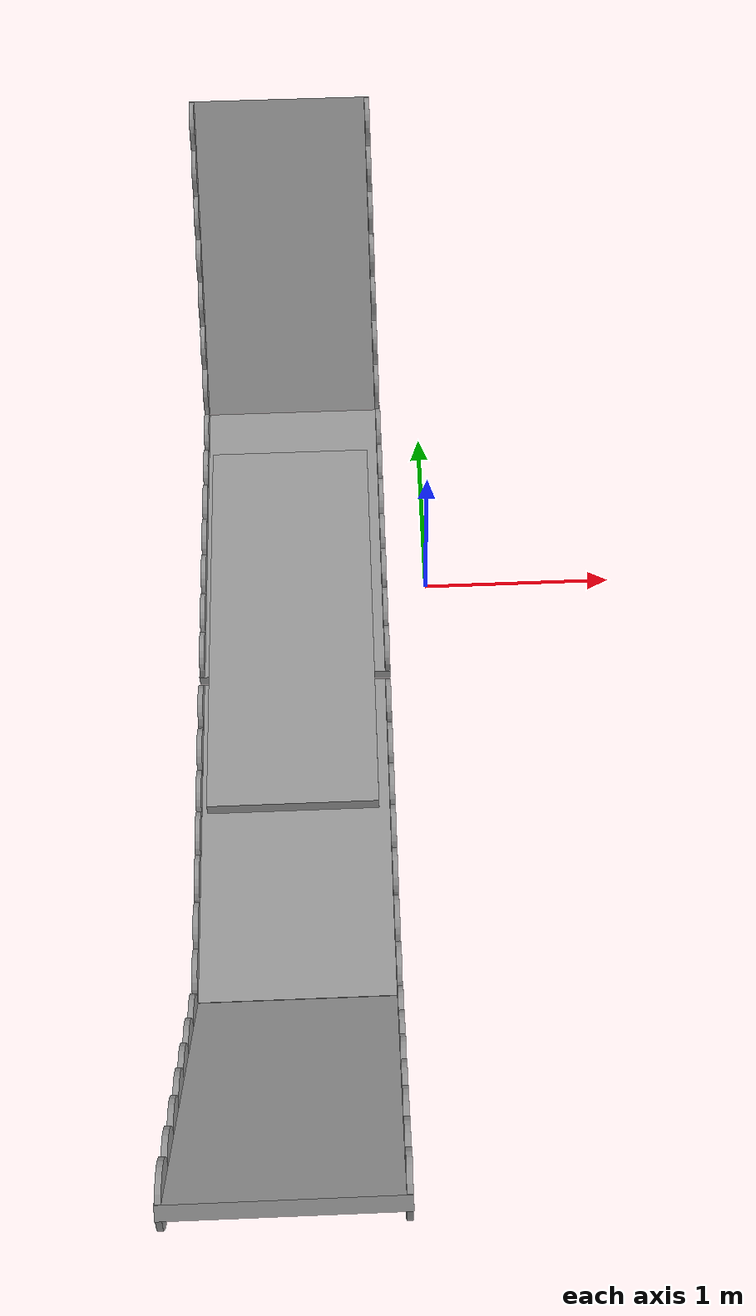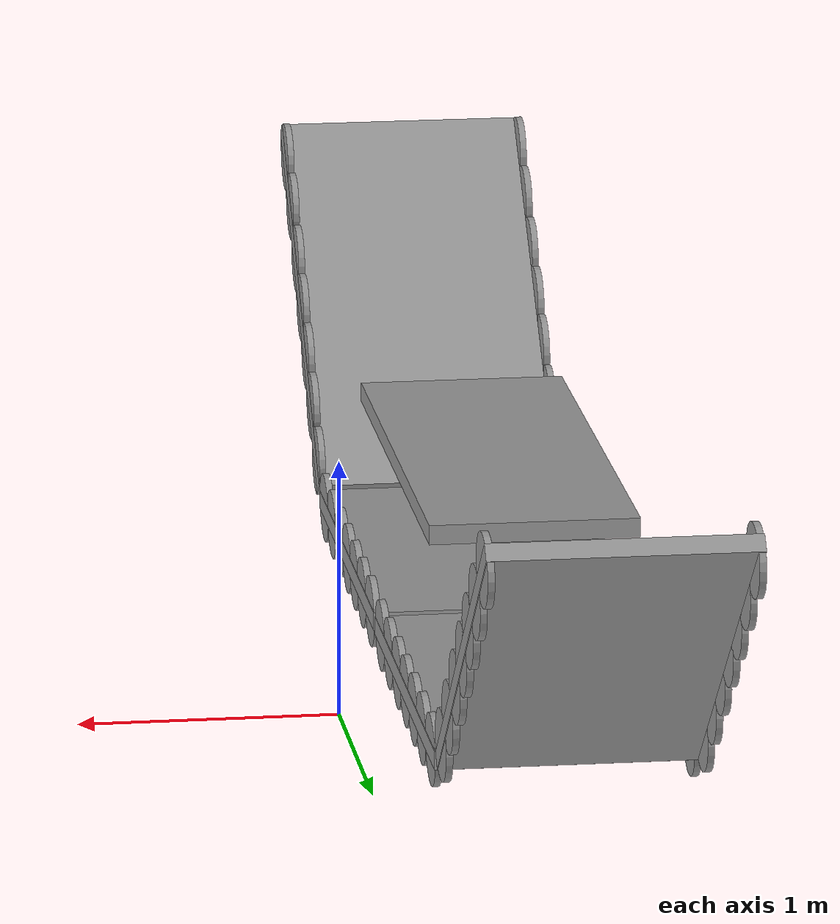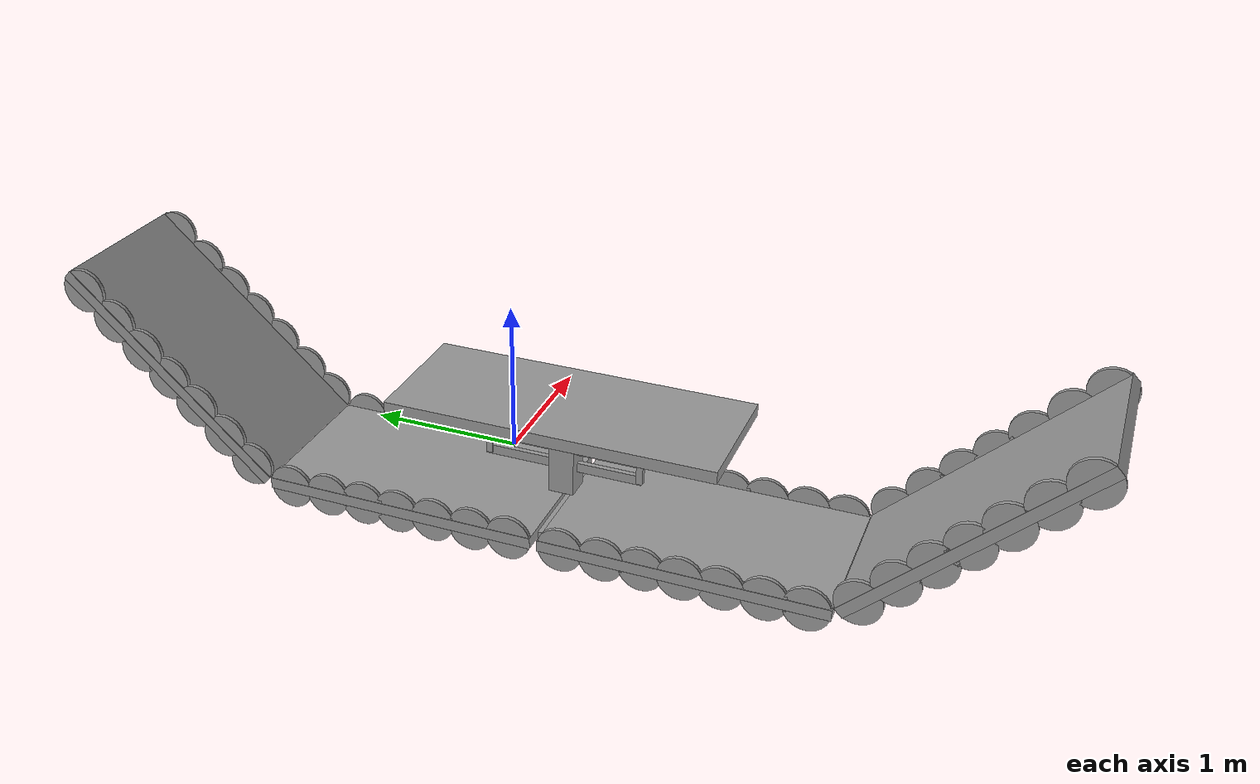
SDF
<?xml version='1.0'?>
<sdf version='1.7'>
  <model name='Model1UniformG2'>
    <link name='link_0'>
      <inertial>
        <mass>4.92358</mass>
        <inertia>
          <ixx>1.7024</ixx>
          <ixy>0</ixy>
          <ixz>0</ixz>
          <iyy>0.266798</iyy>
          <iyz>0</iyz>
          <izz>1.96455</izz>
        </inertia>
        <pose>0 0 0 0 -0 0</pose>
      </inertial>
      <pose>-0.700736 -0.687856 0.795467 0 -0 0</pose>
      <self_collide>0</self_collide>
      <enable_wind>0</enable_wind>
      <kinematic>0</kinematic>
      <gravity>1</gravity>
      <visual name='visual'>
        <pose>0 0 0 0 -0 0</pose>
        <geometry>
          <box>
            <size>0.802858 2.03556 0.075318</size>
          </box>
        </geometry>
        <material>
          <lighting>1</lighting>
          <script>
            <uri>file://media/materials/scripts/gazebo.material</uri>
            <name>Gazebo/Grey</name>
          </script>
          <shader type='pixel'>
            <normal_map>__default__</normal_map>
          </shader>
          <emissive>0 0 0 1</emissive>
        </material>
        <transparency>0</transparency>
        <cast_shadows>1</cast_shadows>
      </visual>
      <collision name='collision'>
        <laser_retro>0</laser_retro>
        <max_contacts>10</max_contacts>
        <pose>0 0 0 0 -0 0</pose>
        <geometry>
          <box>
            <size>0.802858 2.03556 0.075318</size>
          </box>
        </geometry>
        <surface>
          <friction>
            <ode>
              <mu>1</mu>
              <mu2>1</mu2>
              <fdir1>0 0 0</fdir1>
              <slip1>0</slip1>
              <slip2>0</slip2>
            </ode>
            <torsional>
              <coefficient>1</coefficient>
              <patch_radius>0</patch_radius>
              <surface_radius>0</surface_radius>
              <use_patch_radius>1</use_patch_radius>
              <ode>
                <slip>0</slip>
              </ode>
            </torsional>
          </friction>
          <bounce>
            <restitution_coefficient>0</restitution_coefficient>
            <threshold>1e+06</threshold>
          </bounce>
          <contact>
            <collide_without_contact>0</collide_without_contact>
            <collide_without_contact_bitmask>1</collide_without_contact_bitmask>
            <collide_bitmask>1</collide_bitmask>
            <ode>
              <soft_cfm>0</soft_cfm>
              <soft_erp>0.2</soft_erp>
              <kp>1e+13</kp>
              <kd>1</kd>
              <max_vel>0.01</max_vel>
              <min_depth>0</min_depth>
            </ode>
            <bullet>
              <split_impulse>1</split_impulse>
              <split_impulse_penetration_threshold>-0.01</split_impulse_penetration_threshold>
              <soft_cfm>0</soft_cfm>
              <soft_erp>0.2</soft_erp>
              <kp>1e+13</kp>
              <kd>1</kd>
            </bullet>
          </contact>
        </surface>
      </collision>
    </link>
    <link name='link_0_0'>
      <inertial>
        <mass>0.0107934</mass>
        <inertia>
          <ixx>0.000196316</ixx>
          <ixy>0</ixy>
          <ixz>0</ixz>
          <iyy>0.000196742</iyy>
          <iyz>0</iyz>
          <izz>4.40844e-05</izz>
        </inertia>
        <pose>0 0 0 0 -0 0</pose>
      </inertial>
      <pose>-0.712761 -0.662857 0.4784 0 -0 0</pose>
      <self_collide>0</self_collide>
      <enable_wind>0</enable_wind>
      <kinematic>0</kinematic>
      <visual name='visual'>
        <pose>0 0 0 0 -0 0</pose>
        <geometry>
          <box>
            <size>0.157299 0.155787 0.440447</size>
          </box>
        </geometry>
        <material>
          <lighting>1</lighting>
          <script>
            <uri>file://media/materials/scripts/gazebo.material</uri>
            <name>Gazebo/Grey</name>
          </script>
          <shader type='pixel'/>
          <emissive>0 0 0 1</emissive>
        </material>
        <transparency>0</transparency>
        <cast_shadows>1</cast_shadows>
      </visual>
      <collision name='collision'>
        <laser_retro>0</laser_retro>
        <max_contacts>10</max_contacts>
        <pose>0 0 0 0 -0 0</pose>
        <geometry>
          <box>
            <size>0.157299 0.155787 0.440447</size>
          </box>
        </geometry>
        <surface>
          <friction>
            <ode>
              <mu>1</mu>
              <mu2>1</mu2>
              <fdir1>0 0 0</fdir1>
              <slip1>0</slip1>
              <slip2>0</slip2>
            </ode>
            <torsional>
              <coefficient>1</coefficient>
              <patch_radius>0</patch_radius>
              <surface_radius>0</surface_radius>
              <use_patch_radius>1</use_patch_radius>
              <ode>
                <slip>0</slip>
              </ode>
            </torsional>
          </friction>
          <bounce>
            <restitution_coefficient>0</restitution_coefficient>
            <threshold>1e+06</threshold>
          </bounce>
          <contact>
            <collide_without_contact>0</collide_without_contact>
            <collide_without_contact_bitmask>1</collide_without_contact_bitmask>
            <collide_bitmask>1</collide_bitmask>
            <ode>
              <soft_cfm>0</soft_cfm>
              <soft_erp>0.2</soft_erp>
              <kp>1e+13</kp>
              <kd>1</kd>
              <max_vel>0.01</max_vel>
              <min_depth>0</min_depth>
            </ode>
            <bullet>
              <split_impulse>1</split_impulse>
              <split_impulse_penetration_threshold>-0.01</split_impulse_penetration_threshold>
              <soft_cfm>0</soft_cfm>
              <soft_erp>0.2</soft_erp>
              <kp>1e+13</kp>
              <kd>1</kd>
            </bullet>
          </contact>
        </surface>
      </collision>
    </link>
    <link name='link_0_0_clone'>
      <inertial>
        <mass>0.00195522</mass>
        <inertia>
          <ixx>0.00016351</ixx>
          <ixy>0</ixy>
          <ixz>0</ixz>
          <iyy>0.00016311</iyy>
          <iyz>0</iyz>
          <izz>7.5e-07</izz>
        </inertia>
        <pose>0 0 0 0 -0 0</pose>
      </inertial>
      <pose>-0.708838 -0.647909 0.416192 1.57134 -0 0</pose>
      <gravity>1</gravity>
      <self_collide>1</self_collide>
      <kinematic>0</kinematic>
      <enable_wind>0</enable_wind>
      <visual name='visual_0'>
        <pose>0 0 0 0 -0 0</pose>
        <geometry>
          <box>
            <size>0.032896 0.05946 1</size>
          </box>
        </geometry>
        <material>
          <lighting>1</lighting>
          <script>
            <uri>file://media/materials/scripts/gazebo.material</uri>
            <name>Gazebo/Grey</name>
          </script>
          <shader type='pixel'>
            <normal_map>__default__</normal_map>
          </shader>
          <emissive>0 0 0 1</emissive>
        </material>
        <transparency>0</transparency>
        <cast_shadows>1</cast_shadows>
      </visual>
      <collision name='collision'>
        <laser_retro>0</laser_retro>
        <max_contacts>10</max_contacts>
        <pose>0 0 0 0 -0 0</pose>
        <geometry>
          <box>
            <size>0.032896 0.05946 1</size>
          </box>
        </geometry>
        <surface>
          <friction>
            <ode>
              <mu>1</mu>
              <mu2>1</mu2>
              <fdir1>0 0 0</fdir1>
              <slip1>0</slip1>
              <slip2>0</slip2>
            </ode>
            <torsional>
              <coefficient>1</coefficient>
              <patch_radius>0</patch_radius>
              <surface_radius>0</surface_radius>
              <use_patch_radius>1</use_patch_radius>
              <ode>
                <slip>0</slip>
              </ode>
            </torsional>
          </friction>
          <bounce>
            <restitution_coefficient>0</restitution_coefficient>
            <threshold>1e+06</threshold>
          </bounce>
          <contact>
            <collide_without_contact>0</collide_without_contact>
            <collide_without_contact_bitmask>1</collide_without_contact_bitmask>
            <collide_bitmask>1</collide_bitmask>
            <ode>
              <soft_cfm>0</soft_cfm>
              <soft_erp>0.2</soft_erp>
              <kp>1e+13</kp>
              <kd>1</kd>
              <max_vel>0.01</max_vel>
              <min_depth>0</min_depth>
            </ode>
            <bullet>
              <split_impulse>1</split_impulse>
              <split_impulse_penetration_threshold>-0.01</split_impulse_penetration_threshold>
              <soft_cfm>0</soft_cfm>
              <soft_erp>0.2</soft_erp>
              <kp>1e+13</kp>
              <kd>1</kd>
            </bullet>
          </contact>
        </surface>
      </collision>
    </link>
    <link name='link_0_0_clone_clone_0'>
      <inertial>
        <mass>0.00196783</mass>
        <inertia>
          <ixx>0.00016669</ixx>
          <ixy>0</ixy>
          <ixz>0</ixz>
          <iyy>0.00016628</iyy>
          <iyz>0</iyz>
          <izz>7.6e-07</izz>
        </inertia>
        <pose>0 0 0 0 -0 0</pose>
      </inertial>
      <pose>-0.710724 -0.652037 0.533455 1.57134 -0 0</pose>
      <gravity>1</gravity>
      <self_collide>1</self_collide>
      <kinematic>0</kinematic>
      <enable_wind>0</enable_wind>
      <visual name='visual_0'>
        <pose>0 0 0 0 -0 0</pose>
        <geometry>
          <box>
            <size>0.032896 0.05946 1.00645</size>
          </box>
        </geometry>
        <material>
          <lighting>1</lighting>
          <script>
            <uri>file://media/materials/scripts/gazebo.material</uri>
            <name>Gazebo/Grey</name>
          </script>
          <shader type='pixel'>
            <normal_map>__default__</normal_map>
          </shader>
          <emissive>0 0 0 1</emissive>
        </material>
        <transparency>0</transparency>
        <cast_shadows>1</cast_shadows>
      </visual>
      <collision name='collision'>
        <laser_retro>0</laser_retro>
        <max_contacts>10</max_contacts>
        <pose>0 0 0 0 -0 0</pose>
        <geometry>
          <box>
            <size>0.032896 0.05946 1.00645</size>
          </box>
        </geometry>
        <surface>
          <friction>
            <ode>
              <mu>1</mu>
              <mu2>1</mu2>
              <fdir1>0 0 0</fdir1>
              <slip1>0</slip1>
              <slip2>0</slip2>
            </ode>
            <torsional>
              <coefficient>1</coefficient>
              <patch_radius>0</patch_radius>
              <surface_radius>0</surface_radius>
              <use_patch_radius>1</use_patch_radius>
              <ode>
                <slip>0</slip>
              </ode>
            </torsional>
          </friction>
          <bounce>
            <restitution_coefficient>0</restitution_coefficient>
            <threshold>1e+06</threshold>
          </bounce>
          <contact>
            <collide_without_contact>0</collide_without_contact>
            <collide_without_contact_bitmask>1</collide_without_contact_bitmask>
            <collide_bitmask>1</collide_bitmask>
            <ode>
              <soft_cfm>0</soft_cfm>
              <soft_erp>0.2</soft_erp>
              <kp>1e+13</kp>
              <kd>1</kd>
              <max_vel>0.01</max_vel>
              <min_depth>0</min_depth>
            </ode>
            <bullet>
              <split_impulse>1</split_impulse>
              <split_impulse_penetration_threshold>-0.01</split_impulse_penetration_threshold>
              <soft_cfm>0</soft_cfm>
              <soft_erp>0.2</soft_erp>
              <kp>1e+13</kp>
              <kd>1</kd>
            </bullet>
          </contact>
        </surface>
      </collision>
    </link>
    <link name='link_0_0_clone_clone_0_clone'>
      <inertial>
        <mass>0.000556395</mass>
        <inertia>
          <ixx>8.11558e-06</ixx>
          <ixy>0</ixy>
          <ixz>0</ixz>
          <iyy>8.0892e-06</iyy>
          <iyz>0</iyz>
          <izz>1.26731e-07</izz>
        </inertia>
        <pose>0 0 0 0 -0 0</pose>
      </inertial>
      <pose>-0.71095 -0.169941 0.601074 -3.13061 -0 0</pose>
      <gravity>1</gravity>
      <self_collide>1</self_collide>
      <kinematic>0</kinematic>
      <enable_wind>0</enable_wind>
      <visual name='visual_0'>
        <pose>0 0 0 0 -0 0</pose>
        <geometry>
          <box>
            <size>0.032896 0.040634 0.41639</size>
          </box>
        </geometry>
        <material>
          <lighting>1</lighting>
          <script>
            <uri>file://media/materials/scripts/gazebo.material</uri>
            <name>Gazebo/Grey</name>
          </script>
          <shader type='pixel'>
            <normal_map>__default__</normal_map>
          </shader>
          <emissive>0 0 0 1</emissive>
        </material>
        <transparency>0</transparency>
        <cast_shadows>1</cast_shadows>
      </visual>
      <collision name='collision'>
        <laser_retro>0</laser_retro>
        <max_contacts>10</max_contacts>
        <pose>0 0 0 0 -0 0</pose>
        <geometry>
          <box>
            <size>0.032896 0.040634 0.41639</size>
          </box>
        </geometry>
        <surface>
          <friction>
            <ode>
              <mu>1</mu>
              <mu2>1</mu2>
              <fdir1>0 0 0</fdir1>
              <slip1>0</slip1>
              <slip2>0</slip2>
            </ode>
            <torsional>
              <coefficient>1</coefficient>
              <patch_radius>0</patch_radius>
              <surface_radius>0</surface_radius>
              <use_patch_radius>1</use_patch_radius>
              <ode>
                <slip>0</slip>
              </ode>
            </torsional>
          </friction>
          <bounce>
            <restitution_coefficient>0</restitution_coefficient>
            <threshold>1e+06</threshold>
          </bounce>
          <contact>
            <collide_without_contact>0</collide_without_contact>
            <collide_without_contact_bitmask>1</collide_without_contact_bitmask>
            <collide_bitmask>1</collide_bitmask>
            <ode>
              <soft_cfm>0</soft_cfm>
              <soft_erp>0.2</soft_erp>
              <kp>1e+13</kp>
              <kd>1</kd>
              <max_vel>0.01</max_vel>
              <min_depth>0</min_depth>
            </ode>
            <bullet>
              <split_impulse>1</split_impulse>
              <split_impulse_penetration_threshold>-0.01</split_impulse_penetration_threshold>
              <soft_cfm>0</soft_cfm>
              <soft_erp>0.2</soft_erp>
              <kp>1e+13</kp>
              <kd>1</kd>
            </bullet>
          </contact>
        </surface>
      </collision>
    </link>
    <link name='link_0_0_clone_clone_0_clone_clone_0'>
      <inertial>
        <mass>0.000556395</mass>
        <inertia>
          <ixx>8.11558e-06</ixx>
          <ixy>0</ixy>
          <ixz>0</ixz>
          <iyy>8.0892e-06</iyy>
          <iyz>0</iyz>
          <izz>1.26731e-07</izz>
        </inertia>
        <pose>0 0 0 0 -0 0</pose>
      </inertial>
      <pose>-0.71188 -1.13398 0.600998 -3.13061 -0 0</pose>
      <gravity>1</gravity>
      <self_collide>1</self_collide>
      <kinematic>0</kinematic>
      <enable_wind>0</enable_wind>
      <visual name='visual_0'>
        <pose>0 0 0 0 -0 0</pose>
        <geometry>
          <box>
            <size>0.032896 0.040634 0.41639</size>
          </box>
        </geometry>
        <material>
          <lighting>1</lighting>
          <script>
            <uri>file://media/materials/scripts/gazebo.material</uri>
            <name>Gazebo/Grey</name>
          </script>
          <shader type='pixel'>
            <normal_map>__default__</normal_map>
          </shader>
          <emissive>0 0 0 1</emissive>
        </material>
        <transparency>0</transparency>
        <cast_shadows>1</cast_shadows>
      </visual>
      <collision name='collision'>
        <laser_retro>0</laser_retro>
        <max_contacts>10</max_contacts>
        <pose>0 0 0 0 -0 0</pose>
        <geometry>
          <box>
            <size>0.032896 0.040634 0.41639</size>
          </box>
        </geometry>
        <surface>
          <friction>
            <ode>
              <mu>1</mu>
              <mu2>1</mu2>
              <fdir1>0 0 0</fdir1>
              <slip1>0</slip1>
              <slip2>0</slip2>
            </ode>
            <torsional>
              <coefficient>1</coefficient>
              <patch_radius>0</patch_radius>
              <surface_radius>0</surface_radius>
              <use_patch_radius>1</use_patch_radius>
              <ode>
                <slip>0</slip>
              </ode>
            </torsional>
          </friction>
          <bounce>
            <restitution_coefficient>0</restitution_coefficient>
            <threshold>1e+06</threshold>
          </bounce>
          <contact>
            <collide_without_contact>0</collide_without_contact>
            <collide_without_contact_bitmask>1</collide_without_contact_bitmask>
            <collide_bitmask>1</collide_bitmask>
            <ode>
              <soft_cfm>0</soft_cfm>
              <soft_erp>0.2</soft_erp>
              <kp>1e+13</kp>
              <kd>1</kd>
              <max_vel>0.01</max_vel>
              <min_depth>0</min_depth>
            </ode>
            <bullet>
              <split_impulse>1</split_impulse>
              <split_impulse_penetration_threshold>-0.01</split_impulse_penetration_threshold>
              <soft_cfm>0</soft_cfm>
              <soft_erp>0.2</soft_erp>
              <kp>1e+13</kp>
              <kd>1</kd>
            </bullet>
          </contact>
        </surface>
      </collision>
    </link>
    <model name='Model1Uniform31join'>
      <link name='link_0'>
        <inertial>
          <mass>0.145428</mass>
          <inertia>
            <ixx>0.0072166</ixx>
            <ixy>0</ixy>
            <ixz>0</ixz>
            <iyy>0.012146</iyy>
            <iyz>0</iyz>
            <izz>0.0193086</izz>
          </inertia>
          <pose>0 0 0 0 -0 0</pose>
        </inertial>
        <pose>-0.098824 -1.34868 -0.346834 1e-06 -3e-06 1.57118</pose>
        <self_collide>0</self_collide>
        <enable_wind>0</enable_wind>
        <kinematic>0</kinematic>
        <gravity>1</gravity>
        <visual name='visual'>
          <pose>0 0 0 0 -0 0</pose>
          <geometry>
            <box>
              <size>1 0.770227 0.047203</size>
            </box>
          </geometry>
          <material>
            <lighting>1</lighting>
            <script>
              <uri>file://media/materials/scripts/gazebo.material</uri>
              <name>Gazebo/Grey</name>
            </script>
            <shader type='pixel'>
              <normal_map>__default__</normal_map>
            </shader>
            <emissive>0 0 0 1</emissive>
          </material>
          <transparency>0</transparency>
          <cast_shadows>1</cast_shadows>
        </visual>
        <collision name='collision'>
          <laser_retro>0</laser_retro>
          <max_contacts>10</max_contacts>
          <pose>0 0 0 0 -0 0</pose>
          <geometry>
            <box>
              <size>1 0.770227 0.047203</size>
            </box>
          </geometry>
          <surface>
            <friction>
              <ode>
                <mu>1</mu>
                <mu2>1</mu2>
                <fdir1>0 0 0</fdir1>
                <slip1>0</slip1>
                <slip2>0</slip2>
              </ode>
              <torsional>
                <coefficient>1</coefficient>
                <patch_radius>0</patch_radius>
                <surface_radius>0</surface_radius>
                <use_patch_radius>1</use_patch_radius>
                <ode>
                  <slip>0</slip>
                </ode>
              </torsional>
            </friction>
            <bounce>
              <restitution_coefficient>0</restitution_coefficient>
              <threshold>1e+06</threshold>
            </bounce>
            <contact>
              <collide_without_contact>0</collide_without_contact>
              <collide_without_contact_bitmask>1</collide_without_contact_bitmask>
              <collide_bitmask>1</collide_bitmask>
              <ode>
                <soft_cfm>0</soft_cfm>
                <soft_erp>0.2</soft_erp>
                <kp>1e+13</kp>
                <kd>1</kd>
                <max_vel>0.01</max_vel>
                <min_depth>0</min_depth>
              </ode>
              <bullet>
                <split_impulse>1</split_impulse>
                <split_impulse_penetration_threshold>-0.01</split_impulse_penetration_threshold>
                <soft_cfm>0</soft_cfm>
                <soft_erp>0.2</soft_erp>
                <kp>1e+13</kp>
                <kd>1</kd>
              </bullet>
            </contact>
          </surface>
        </collision>
      </link>
      <model name='Model1Uniform'>
        <link name='link_1'>
          <inertial>
            <mass>0.124515</mass>
            <inertia>
              <ixx>0.0312917</ixx>
              <ixy>0</ixy>
              <ixz>0</ixz>
              <iyy>0.0104297</iyy>
              <iyz>0</iyz>
              <izz>0.0416145</izz>
            </inertia>
            <pose>0 0 0 0 -0 0</pose>
          </inertial>
          <pose>-0.112763 -0.59103 -0.000382 0 -0 0</pose>
          <self_collide>0</self_collide>
          <enable_wind>0</enable_wind>
          <kinematic>0</kinematic>
          <visual name='visual'>
            <pose>0 0 0 0 -0 0</pose>
            <geometry>
              <box>
                <size>1 1.7351 0.071755</size>
              </box>
            </geometry>
            <material>
              <lighting>1</lighting>
              <script>
                <uri>file://media/materials/scripts/gazebo.material</uri>
                <name>Gazebo/Grey</name>
              </script>
              <shader type='pixel'/>
              <emissive>0 0 0 1</emissive>
            </material>
            <transparency>0</transparency>
            <cast_shadows>1</cast_shadows>
          </visual>
          <collision name='collision'>
            <laser_retro>0</laser_retro>
            <max_contacts>10</max_contacts>
            <pose>0 0 0 0 -0 0</pose>
            <geometry>
              <box>
                <size>1 1.7351 0.071755</size>
              </box>
            </geometry>
            <surface>
              <friction>
                <ode>
                  <mu>1</mu>
                  <mu2>1</mu2>
                  <fdir1>0 0 0</fdir1>
                  <slip1>0</slip1>
                  <slip2>0</slip2>
                </ode>
                <torsional>
                  <coefficient>1</coefficient>
                  <patch_radius>0</patch_radius>
                  <surface_radius>0</surface_radius>
                  <use_patch_radius>1</use_patch_radius>
                  <ode>
                    <slip>0</slip>
                  </ode>
                </torsional>
              </friction>
              <bounce>
                <restitution_coefficient>0</restitution_coefficient>
                <threshold>1e+06</threshold>
              </bounce>
              <contact>
                <collide_without_contact>0</collide_without_contact>
                <collide_without_contact_bitmask>1</collide_without_contact_bitmask>
                <collide_bitmask>1</collide_bitmask>
                <ode>
                  <soft_cfm>0</soft_cfm>
                  <soft_erp>0.2</soft_erp>
                  <kp>1e+13</kp>
                  <kd>1</kd>
                  <max_vel>0.01</max_vel>
                  <min_depth>0</min_depth>
                </ode>
                <bullet>
                  <split_impulse>1</split_impulse>
                  <split_impulse_penetration_threshold>-0.01</split_impulse_penetration_threshold>
                  <soft_cfm>0</soft_cfm>
                  <soft_erp>0.2</soft_erp>
                  <kp>1e+13</kp>
                  <kd>1</kd>
                </bullet>
              </contact>
            </surface>
          </collision>
        </link>
        <link name='link_2'>
          <inertial>
            <mass>0.00191513</mass>
            <inertia>
              <ixx>9.38622e-06</ixx>
              <ixy>0</ixy>
              <ixz>0</ixz>
              <iyy>9.38622e-06</iyy>
              <iyz>0</iyz>
              <izz>1.8563e-05</izz>
            </inertia>
            <pose>0 0 0 0 -0 0</pose>
          </inertial>
          <pose>0.372581 -1.31934 0.000164 3.14159 1.55155 3.14159</pose>
          <self_collide>0</self_collide>
          <enable_wind>0</enable_wind>
          <kinematic>0</kinematic>
          <visual name='visual'>
            <pose>0 0 0 0 -0 0</pose>
            <geometry>
              <cylinder>
                <radius>0.139232</radius>
                <length>0.0256172</length>
              </cylinder>
            </geometry>
            <material>
              <lighting>1</lighting>
              <script>
                <uri>file://media/materials/scripts/gazebo.material</uri>
                <name>Gazebo/Grey</name>
              </script>
              <shader type='pixel'/>
              <emissive>0 0 0 1</emissive>
            </material>
            <transparency>0</transparency>
            <cast_shadows>1</cast_shadows>
          </visual>
          <collision name='collision'>
            <laser_retro>0</laser_retro>
            <max_contacts>10</max_contacts>
            <pose>0 0 0 0 -0 0</pose>
            <geometry>
              <cylinder>
                <radius>0.139232</radius>
                <length>0.025617</length>
              </cylinder>
            </geometry>
            <surface>
              <friction>
                <ode>
                  <mu>1</mu>
                  <mu2>1</mu2>
                  <fdir1>0 0 0</fdir1>
                  <slip1>0</slip1>
                  <slip2>0</slip2>
                </ode>
                <torsional>
                  <coefficient>1</coefficient>
                  <patch_radius>0</patch_radius>
                  <surface_radius>0</surface_radius>
                  <use_patch_radius>1</use_patch_radius>
                  <ode>
                    <slip>0</slip>
                  </ode>
                </torsional>
              </friction>
              <bounce>
                <restitution_coefficient>0</restitution_coefficient>
                <threshold>1e+06</threshold>
              </bounce>
              <contact>
                <collide_without_contact>0</collide_without_contact>
                <collide_without_contact_bitmask>1</collide_without_contact_bitmask>
                <collide_bitmask>1</collide_bitmask>
                <ode>
                  <soft_cfm>0</soft_cfm>
                  <soft_erp>0.2</soft_erp>
                  <kp>1e+13</kp>
                  <kd>1</kd>
                  <max_vel>0.01</max_vel>
                  <min_depth>0</min_depth>
                </ode>
                <bullet>
                  <split_impulse>1</split_impulse>
                  <split_impulse_penetration_threshold>-0.01</split_impulse_penetration_threshold>
                  <soft_cfm>0</soft_cfm>
                  <soft_erp>0.2</soft_erp>
                  <kp>1e+13</kp>
                  <kd>1</kd>
                </bullet>
              </contact>
            </surface>
          </collision>
        </link>
        <link name='link_2_clone'>
          <inertial>
            <mass>0.00198759</mass>
            <inertia>
              <ixx>9.74141e-06</ixx>
              <ixy>0</ixy>
              <ixz>0</ixz>
              <iyy>9.74141e-06</iyy>
              <iyz>0</iyz>
              <izz>1.92654e-05</izz>
            </inertia>
            <pose>0 0 0 0 -0 0</pose>
          </inertial>
          <pose>-0.597277 -0.59103 0.000164 3.14159 1.55155 3.14159</pose>
          <self_collide>0</self_collide>
          <enable_wind>0</enable_wind>
          <kinematic>0</kinematic>
          <visual name='visual'>
            <pose>0 0 0 0 -0 0</pose>
            <geometry>
              <cylinder>
                <radius>0.139233</radius>
                <length>0.0256172</length>
              </cylinder>
            </geometry>
            <material>
              <lighting>1</lighting>
              <script>
                <uri>file://media/materials/scripts/gazebo.material</uri>
                <name>Gazebo/Grey</name>
              </script>
              <shader type='pixel'/>
              <emissive>0 0 0 1</emissive>
            </material>
            <transparency>0</transparency>
            <cast_shadows>1</cast_shadows>
          </visual>
          <collision name='collision'>
            <laser_retro>0</laser_retro>
            <max_contacts>10</max_contacts>
            <pose>0 0 0 0 -0 0</pose>
            <geometry>
              <cylinder>
                <radius>0.139233</radius>
                <length>0.025617</length>
              </cylinder>
            </geometry>
            <surface>
              <friction>
                <ode>
                  <mu>1</mu>
                  <mu2>1</mu2>
                  <fdir1>0 0 0</fdir1>
                  <slip1>0</slip1>
                  <slip2>0</slip2>
                </ode>
                <torsional>
                  <coefficient>1</coefficient>
                  <patch_radius>0</patch_radius>
                  <surface_radius>0</surface_radius>
                  <use_patch_radius>1</use_patch_radius>
                  <ode>
                    <slip>0</slip>
                  </ode>
                </torsional>
              </friction>
              <bounce>
                <restitution_coefficient>0</restitution_coefficient>
                <threshold>1e+06</threshold>
              </bounce>
              <contact>
                <collide_without_contact>0</collide_without_contact>
                <collide_without_contact_bitmask>1</collide_without_contact_bitmask>
                <collide_bitmask>1</collide_bitmask>
                <ode>
                  <soft_cfm>0</soft_cfm>
                  <soft_erp>0.2</soft_erp>
                  <kp>1e+13</kp>
                  <kd>1</kd>
                  <max_vel>0.01</max_vel>
                  <min_depth>0</min_depth>
                </ode>
                <bullet>
                  <split_impulse>1</split_impulse>
                  <split_impulse_penetration_threshold>-0.01</split_impulse_penetration_threshold>
                  <soft_cfm>0</soft_cfm>
                  <soft_erp>0.2</soft_erp>
                  <kp>1e+13</kp>
                  <kd>1</kd>
                </bullet>
              </contact>
            </surface>
          </collision>
        </link>
        <link name='link_2_clone_1'>
          <inertial>
            <mass>0.00198759</mass>
            <inertia>
              <ixx>9.74141e-06</ixx>
              <ixy>0</ixy>
              <ixz>0</ixz>
              <iyy>9.74141e-06</iyy>
              <iyz>0</iyz>
              <izz>1.92654e-05</izz>
            </inertia>
            <pose>0 0 0 0 -0 0</pose>
          </inertial>
          <pose>0.371751 -1.08026 0.000164 3.14159 1.55155 3.14159</pose>
          <self_collide>0</self_collide>
          <enable_wind>0</enable_wind>
          <kinematic>0</kinematic>
          <visual name='visual'>
            <pose>0 0 0 0 -0 0</pose>
            <geometry>
              <cylinder>
                <radius>0.139233</radius>
                <length>0.0256172</length>
              </cylinder>
            </geometry>
            <material>
              <lighting>1</lighting>
              <script>
                <uri>file://media/materials/scripts/gazebo.material</uri>
                <name>Gazebo/Grey</name>
              </script>
              <shader type='pixel'/>
              <emissive>0 0 0 1</emissive>
            </material>
            <transparency>0</transparency>
            <cast_shadows>1</cast_shadows>
          </visual>
          <collision name='collision'>
            <laser_retro>0</laser_retro>
            <max_contacts>10</max_contacts>
            <pose>0 0 0 0 -0 0</pose>
            <geometry>
              <cylinder>
                <radius>0.139233</radius>
                <length>0.025617</length>
              </cylinder>
            </geometry>
            <surface>
              <friction>
                <ode>
                  <mu>1</mu>
                  <mu2>1</mu2>
                  <fdir1>0 0 0</fdir1>
                  <slip1>0</slip1>
                  <slip2>0</slip2>
                </ode>
                <torsional>
                  <coefficient>1</coefficient>
                  <patch_radius>0</patch_radius>
                  <surface_radius>0</surface_radius>
                  <use_patch_radius>1</use_patch_radius>
                  <ode>
                    <slip>0</slip>
                  </ode>
                </torsional>
              </friction>
              <bounce>
                <restitution_coefficient>0</restitution_coefficient>
                <threshold>1e+06</threshold>
              </bounce>
              <contact>
                <collide_without_contact>0</collide_without_contact>
                <collide_without_contact_bitmask>1</collide_without_contact_bitmask>
                <collide_bitmask>1</collide_bitmask>
                <ode>
                  <soft_cfm>0</soft_cfm>
                  <soft_erp>0.2</soft_erp>
                  <kp>1e+13</kp>
                  <kd>1</kd>
                  <max_vel>0.01</max_vel>
                  <min_depth>0</min_depth>
                </ode>
                <bullet>
                  <split_impulse>1</split_impulse>
                  <split_impulse_penetration_threshold>-0.01</split_impulse_penetration_threshold>
                  <soft_cfm>0</soft_cfm>
                  <soft_erp>0.2</soft_erp>
                  <kp>1e+13</kp>
                  <kd>1</kd>
                </bullet>
              </contact>
            </surface>
          </collision>
        </link>
        <link name='link_2_clone_10'>
          <inertial>
            <mass>0.00198759</mass>
            <inertia>
              <ixx>9.74141e-06</ixx>
              <ixy>0</ixy>
              <ixz>0</ixz>
              <iyy>9.74141e-06</iyy>
              <iyz>0</iyz>
              <izz>1.92654e-05</izz>
            </inertia>
            <pose>0 0 0 0 -0 0</pose>
          </inertial>
          <pose>-0.597277 -1.31934 0.000164 3.14159 1.55155 3.14159</pose>
          <self_collide>0</self_collide>
          <enable_wind>0</enable_wind>
          <kinematic>0</kinematic>
          <visual name='visual'>
            <pose>0 0 0 0 -0 0</pose>
            <geometry>
              <cylinder>
                <radius>0.139233</radius>
                <length>0.0256172</length>
              </cylinder>
            </geometry>
            <material>
              <lighting>1</lighting>
              <script>
                <uri>file://media/materials/scripts/gazebo.material</uri>
                <name>Gazebo/Grey</name>
              </script>
              <shader type='pixel'/>
              <emissive>0 0 0 1</emissive>
            </material>
            <transparency>0</transparency>
            <cast_shadows>1</cast_shadows>
          </visual>
          <collision name='collision'>
            <laser_retro>0</laser_retro>
            <max_contacts>10</max_contacts>
            <pose>0 0 0 0 -0 0</pose>
            <geometry>
              <cylinder>
                <radius>0.139233</radius>
                <length>0.025617</length>
              </cylinder>
            </geometry>
            <surface>
              <friction>
                <ode>
                  <mu>1</mu>
                  <mu2>1</mu2>
                  <fdir1>0 0 0</fdir1>
                  <slip1>0</slip1>
                  <slip2>0</slip2>
                </ode>
                <torsional>
                  <coefficient>1</coefficient>
                  <patch_radius>0</patch_radius>
                  <surface_radius>0</surface_radius>
                  <use_patch_radius>1</use_patch_radius>
                  <ode>
                    <slip>0</slip>
                  </ode>
                </torsional>
              </friction>
              <bounce>
                <restitution_coefficient>0</restitution_coefficient>
                <threshold>1e+06</threshold>
              </bounce>
              <contact>
                <collide_without_contact>0</collide_without_contact>
                <collide_without_contact_bitmask>1</collide_without_contact_bitmask>
                <collide_bitmask>1</collide_bitmask>
                <ode>
                  <soft_cfm>0</soft_cfm>
                  <soft_erp>0.2</soft_erp>
                  <kp>1e+13</kp>
                  <kd>1</kd>
                  <max_vel>0.01</max_vel>
                  <min_depth>0</min_depth>
                </ode>
                <bullet>
                  <split_impulse>1</split_impulse>
                  <split_impulse_penetration_threshold>-0.01</split_impulse_penetration_threshold>
                  <soft_cfm>0</soft_cfm>
                  <soft_erp>0.2</soft_erp>
                  <kp>1e+13</kp>
                  <kd>1</kd>
                </bullet>
              </contact>
            </surface>
          </collision>
        </link>
        <link name='link_2_clone_11'>
          <inertial>
            <mass>0.00198759</mass>
            <inertia>
              <ixx>9.74141e-06</ixx>
              <ixy>0</ixy>
              <ixz>0</ixz>
              <iyy>9.74141e-06</iyy>
              <iyz>0</iyz>
              <izz>1.92654e-05</izz>
            </inertia>
            <pose>0 0 0 0 -0 0</pose>
          </inertial>
          <pose>-0.597277 -0.828803 0.000164 3.14159 1.55155 3.14159</pose>
          <self_collide>0</self_collide>
          <enable_wind>0</enable_wind>
          <kinematic>0</kinematic>
          <visual name='visual'>
            <pose>0 0 0 0 -0 0</pose>
            <geometry>
              <cylinder>
                <radius>0.139233</radius>
                <length>0.0256172</length>
              </cylinder>
            </geometry>
            <material>
              <lighting>1</lighting>
              <script>
                <uri>file://media/materials/scripts/gazebo.material</uri>
                <name>Gazebo/Grey</name>
              </script>
              <shader type='pixel'/>
              <emissive>0 0 0 1</emissive>
            </material>
            <transparency>0</transparency>
            <cast_shadows>1</cast_shadows>
          </visual>
          <collision name='collision'>
            <laser_retro>0</laser_retro>
            <max_contacts>10</max_contacts>
            <pose>0 0 0 0 -0 0</pose>
            <geometry>
              <cylinder>
                <radius>0.139233</radius>
                <length>0.025617</length>
              </cylinder>
            </geometry>
            <surface>
              <friction>
                <ode>
                  <mu>1</mu>
                  <mu2>1</mu2>
                  <fdir1>0 0 0</fdir1>
                  <slip1>0</slip1>
                  <slip2>0</slip2>
                </ode>
                <torsional>
                  <coefficient>1</coefficient>
                  <patch_radius>0</patch_radius>
                  <surface_radius>0</surface_radius>
                  <use_patch_radius>1</use_patch_radius>
                  <ode>
                    <slip>0</slip>
                  </ode>
                </torsional>
              </friction>
              <bounce>
                <restitution_coefficient>0</restitution_coefficient>
                <threshold>1e+06</threshold>
              </bounce>
              <contact>
                <collide_without_contact>0</collide_without_contact>
                <collide_without_contact_bitmask>1</collide_without_contact_bitmask>
                <collide_bitmask>1</collide_bitmask>
                <ode>
                  <soft_cfm>0</soft_cfm>
                  <soft_erp>0.2</soft_erp>
                  <kp>1e+13</kp>
                  <kd>1</kd>
                  <max_vel>0.01</max_vel>
                  <min_depth>0</min_depth>
                </ode>
                <bullet>
                  <split_impulse>1</split_impulse>
                  <split_impulse_penetration_threshold>-0.01</split_impulse_penetration_threshold>
                  <soft_cfm>0</soft_cfm>
                  <soft_erp>0.2</soft_erp>
                  <kp>1e+13</kp>
                  <kd>1</kd>
                </bullet>
              </contact>
            </surface>
          </collision>
        </link>
        <link name='link_2_clone_13'>
          <inertial>
            <mass>0.00198759</mass>
            <inertia>
              <ixx>9.74141e-06</ixx>
              <ixy>0</ixy>
              <ixz>0</ixz>
              <iyy>9.74141e-06</iyy>
              <iyz>0</iyz>
              <izz>1.92654e-05</izz>
            </inertia>
            <pose>0 0 0 0 -0 0</pose>
          </inertial>
          <pose>0.371751 0.137284 0.000164 3.14159 1.55155 3.14159</pose>
          <self_collide>0</self_collide>
          <enable_wind>0</enable_wind>
          <kinematic>0</kinematic>
          <visual name='visual'>
            <pose>0 0 0 0 -0 0</pose>
            <geometry>
              <cylinder>
                <radius>0.139233</radius>
                <length>0.0256172</length>
              </cylinder>
            </geometry>
            <material>
              <lighting>1</lighting>
              <script>
                <uri>file://media/materials/scripts/gazebo.material</uri>
                <name>Gazebo/Grey</name>
              </script>
              <shader type='pixel'/>
              <emissive>0 0 0 1</emissive>
            </material>
            <transparency>0</transparency>
            <cast_shadows>1</cast_shadows>
          </visual>
          <collision name='collision'>
            <laser_retro>0</laser_retro>
            <max_contacts>10</max_contacts>
            <pose>0 0 0 0 -0 0</pose>
            <geometry>
              <cylinder>
                <radius>0.139233</radius>
                <length>0.025617</length>
              </cylinder>
            </geometry>
            <surface>
              <friction>
                <ode>
                  <mu>1</mu>
                  <mu2>1</mu2>
                  <fdir1>0 0 0</fdir1>
                  <slip1>0</slip1>
                  <slip2>0</slip2>
                </ode>
                <torsional>
                  <coefficient>1</coefficient>
                  <patch_radius>0</patch_radius>
                  <surface_radius>0</surface_radius>
                  <use_patch_radius>1</use_patch_radius>
                  <ode>
                    <slip>0</slip>
                  </ode>
                </torsional>
              </friction>
              <bounce>
                <restitution_coefficient>0</restitution_coefficient>
                <threshold>1e+06</threshold>
              </bounce>
              <contact>
                <collide_without_contact>0</collide_without_contact>
                <collide_without_contact_bitmask>1</collide_without_contact_bitmask>
                <collide_bitmask>1</collide_bitmask>
                <ode>
                  <soft_cfm>0</soft_cfm>
                  <soft_erp>0.2</soft_erp>
                  <kp>1e+13</kp>
                  <kd>1</kd>
                  <max_vel>0.01</max_vel>
                  <min_depth>0</min_depth>
                </ode>
                <bullet>
                  <split_impulse>1</split_impulse>
                  <split_impulse_penetration_threshold>-0.01</split_impulse_penetration_threshold>
                  <soft_cfm>0</soft_cfm>
                  <soft_erp>0.2</soft_erp>
                  <kp>1e+13</kp>
                  <kd>1</kd>
                </bullet>
              </contact>
            </surface>
          </collision>
        </link>
        <link name='link_2_clone_14'>
          <inertial>
            <mass>0.00198759</mass>
            <inertia>
              <ixx>9.74141e-06</ixx>
              <ixy>0</ixy>
              <ixz>0</ixz>
              <iyy>9.74141e-06</iyy>
              <iyz>0</iyz>
              <izz>1.92654e-05</izz>
            </inertia>
            <pose>0 0 0 0 -0 0</pose>
          </inertial>
          <pose>0.371751 -0.119911 0.000164 3.14159 1.55155 3.14159</pose>
          <self_collide>0</self_collide>
          <enable_wind>0</enable_wind>
          <kinematic>0</kinematic>
          <visual name='visual'>
            <pose>0 0 0 0 -0 0</pose>
            <geometry>
              <cylinder>
                <radius>0.139233</radius>
                <length>0.0256172</length>
              </cylinder>
            </geometry>
            <material>
              <lighting>1</lighting>
              <script>
                <uri>file://media/materials/scripts/gazebo.material</uri>
                <name>Gazebo/Grey</name>
              </script>
              <shader type='pixel'/>
              <emissive>0 0 0 1</emissive>
            </material>
            <transparency>0</transparency>
            <cast_shadows>1</cast_shadows>
          </visual>
          <collision name='collision'>
            <laser_retro>0</laser_retro>
            <max_contacts>10</max_contacts>
            <pose>0 0 0 0 -0 0</pose>
            <geometry>
              <cylinder>
                <radius>0.139233</radius>
                <length>0.025617</length>
              </cylinder>
            </geometry>
            <surface>
              <friction>
                <ode>
                  <mu>1</mu>
                  <mu2>1</mu2>
                  <fdir1>0 0 0</fdir1>
                  <slip1>0</slip1>
                  <slip2>0</slip2>
                </ode>
                <torsional>
                  <coefficient>1</coefficient>
                  <patch_radius>0</patch_radius>
                  <surface_radius>0</surface_radius>
                  <use_patch_radius>1</use_patch_radius>
                  <ode>
                    <slip>0</slip>
                  </ode>
                </torsional>
              </friction>
              <bounce>
                <restitution_coefficient>0</restitution_coefficient>
                <threshold>1e+06</threshold>
              </bounce>
              <contact>
                <collide_without_contact>0</collide_without_contact>
                <collide_without_contact_bitmask>1</collide_without_contact_bitmask>
                <collide_bitmask>1</collide_bitmask>
                <ode>
                  <soft_cfm>0</soft_cfm>
                  <soft_erp>0.2</soft_erp>
                  <kp>1e+13</kp>
                  <kd>1</kd>
                  <max_vel>0.01</max_vel>
                  <min_depth>0</min_depth>
                </ode>
                <bullet>
                  <split_impulse>1</split_impulse>
                  <split_impulse_penetration_threshold>-0.01</split_impulse_penetration_threshold>
                  <soft_cfm>0</soft_cfm>
                  <soft_erp>0.2</soft_erp>
                  <kp>1e+13</kp>
                  <kd>1</kd>
                </bullet>
              </contact>
            </surface>
          </collision>
        </link>
        <link name='link_2_clone_16'>
          <inertial>
            <mass>0.00198759</mass>
            <inertia>
              <ixx>9.74141e-06</ixx>
              <ixy>0</ixy>
              <ixz>0</ixz>
              <iyy>9.74141e-06</iyy>
              <iyz>0</iyz>
              <izz>1.92654e-05</izz>
            </inertia>
            <pose>0 0 0 0 -0 0</pose>
          </inertial>
          <pose>-0.597277 0.137284 0.000164 3.14159 1.55155 3.14159</pose>
          <self_collide>0</self_collide>
          <enable_wind>0</enable_wind>
          <kinematic>0</kinematic>
          <visual name='visual'>
            <pose>0 0 0 0 -0 0</pose>
            <geometry>
              <cylinder>
                <radius>0.139233</radius>
                <length>0.0256172</length>
              </cylinder>
            </geometry>
            <material>
              <lighting>1</lighting>
              <script>
                <uri>file://media/materials/scripts/gazebo.material</uri>
                <name>Gazebo/Grey</name>
              </script>
              <shader type='pixel'/>
              <emissive>0 0 0 1</emissive>
            </material>
            <transparency>0</transparency>
            <cast_shadows>1</cast_shadows>
          </visual>
          <collision name='collision'>
            <laser_retro>0</laser_retro>
            <max_contacts>10</max_contacts>
            <pose>0 0 0 0 -0 0</pose>
            <geometry>
              <cylinder>
                <radius>0.139233</radius>
                <length>0.025617</length>
              </cylinder>
            </geometry>
            <surface>
              <friction>
                <ode>
                  <mu>1</mu>
                  <mu2>1</mu2>
                  <fdir1>0 0 0</fdir1>
                  <slip1>0</slip1>
                  <slip2>0</slip2>
                </ode>
                <torsional>
                  <coefficient>1</coefficient>
                  <patch_radius>0</patch_radius>
                  <surface_radius>0</surface_radius>
                  <use_patch_radius>1</use_patch_radius>
                  <ode>
                    <slip>0</slip>
                  </ode>
                </torsional>
              </friction>
              <bounce>
                <restitution_coefficient>0</restitution_coefficient>
                <threshold>1e+06</threshold>
              </bounce>
              <contact>
                <collide_without_contact>0</collide_without_contact>
                <collide_without_contact_bitmask>1</collide_without_contact_bitmask>
                <collide_bitmask>1</collide_bitmask>
                <ode>
                  <soft_cfm>0</soft_cfm>
                  <soft_erp>0.2</soft_erp>
                  <kp>1e+13</kp>
                  <kd>1</kd>
                  <max_vel>0.01</max_vel>
                  <min_depth>0</min_depth>
                </ode>
                <bullet>
                  <split_impulse>1</split_impulse>
                  <split_impulse_penetration_threshold>-0.01</split_impulse_penetration_threshold>
                  <soft_cfm>0</soft_cfm>
                  <soft_erp>0.2</soft_erp>
                  <kp>1e+13</kp>
                  <kd>1</kd>
                </bullet>
              </contact>
            </surface>
          </collision>
        </link>
        <link name='link_2_clone_2'>
          <inertial>
            <mass>0.00198759</mass>
            <inertia>
              <ixx>9.74141e-06</ixx>
              <ixy>0</ixy>
              <ixz>0</ixz>
              <iyy>9.74141e-06</iyy>
              <iyz>0</iyz>
              <izz>1.92654e-05</izz>
            </inertia>
            <pose>0 0 0 0 -0 0</pose>
          </inertial>
          <pose>0.371751 -0.825611 0.000164 3.14159 1.55155 3.14159</pose>
          <self_collide>0</self_collide>
          <enable_wind>0</enable_wind>
          <kinematic>0</kinematic>
          <visual name='visual'>
            <pose>0 0 0 0 -0 0</pose>
            <geometry>
              <cylinder>
                <radius>0.139233</radius>
                <length>0.0256172</length>
              </cylinder>
            </geometry>
            <material>
              <lighting>1</lighting>
              <script>
                <uri>file://media/materials/scripts/gazebo.material</uri>
                <name>Gazebo/Grey</name>
              </script>
              <shader type='pixel'/>
              <emissive>0 0 0 1</emissive>
            </material>
            <transparency>0</transparency>
            <cast_shadows>1</cast_shadows>
          </visual>
          <collision name='collision'>
            <laser_retro>0</laser_retro>
            <max_contacts>10</max_contacts>
            <pose>0 0 0 0 -0 0</pose>
            <geometry>
              <cylinder>
                <radius>0.139233</radius>
                <length>0.025617</length>
              </cylinder>
            </geometry>
            <surface>
              <friction>
                <ode>
                  <mu>1</mu>
                  <mu2>1</mu2>
                  <fdir1>0 0 0</fdir1>
                  <slip1>0</slip1>
                  <slip2>0</slip2>
                </ode>
                <torsional>
                  <coefficient>1</coefficient>
                  <patch_radius>0</patch_radius>
                  <surface_radius>0</surface_radius>
                  <use_patch_radius>1</use_patch_radius>
                  <ode>
                    <slip>0</slip>
                  </ode>
                </torsional>
              </friction>
              <bounce>
                <restitution_coefficient>0</restitution_coefficient>
                <threshold>1e+06</threshold>
              </bounce>
              <contact>
                <collide_without_contact>0</collide_without_contact>
                <collide_without_contact_bitmask>1</collide_without_contact_bitmask>
                <collide_bitmask>1</collide_bitmask>
                <ode>
                  <soft_cfm>0</soft_cfm>
                  <soft_erp>0.2</soft_erp>
                  <kp>1e+13</kp>
                  <kd>1</kd>
                  <max_vel>0.01</max_vel>
                  <min_depth>0</min_depth>
                </ode>
                <bullet>
                  <split_impulse>1</split_impulse>
                  <split_impulse_penetration_threshold>-0.01</split_impulse_penetration_threshold>
                  <soft_cfm>0</soft_cfm>
                  <soft_erp>0.2</soft_erp>
                  <kp>1e+13</kp>
                  <kd>1</kd>
                </bullet>
              </contact>
            </surface>
          </collision>
        </link>
        <link name='link_2_clone_3'>
          <inertial>
            <mass>0.00198759</mass>
            <inertia>
              <ixx>9.74141e-06</ixx>
              <ixy>0</ixy>
              <ixz>0</ixz>
              <iyy>9.74141e-06</iyy>
              <iyz>0</iyz>
              <izz>1.92654e-05</izz>
            </inertia>
            <pose>0 0 0 0 -0 0</pose>
          </inertial>
          <pose>-0.597277 -0.117317 0.000164 3.14159 1.55155 3.14159</pose>
          <self_collide>0</self_collide>
          <enable_wind>0</enable_wind>
          <kinematic>0</kinematic>
          <visual name='visual'>
            <pose>0 0 0 0 -0 0</pose>
            <geometry>
              <cylinder>
                <radius>0.139233</radius>
                <length>0.0256172</length>
              </cylinder>
            </geometry>
            <material>
              <lighting>1</lighting>
              <script>
                <uri>file://media/materials/scripts/gazebo.material</uri>
                <name>Gazebo/Grey</name>
              </script>
              <shader type='pixel'/>
              <emissive>0 0 0 1</emissive>
            </material>
            <transparency>0</transparency>
            <cast_shadows>1</cast_shadows>
          </visual>
          <collision name='collision'>
            <laser_retro>0</laser_retro>
            <max_contacts>10</max_contacts>
            <pose>0 0 0 0 -0 0</pose>
            <geometry>
              <cylinder>
                <radius>0.139233</radius>
                <length>0.025617</length>
              </cylinder>
            </geometry>
            <surface>
              <friction>
                <ode>
                  <mu>1</mu>
                  <mu2>1</mu2>
                  <fdir1>0 0 0</fdir1>
                  <slip1>0</slip1>
                  <slip2>0</slip2>
                </ode>
                <torsional>
                  <coefficient>1</coefficient>
                  <patch_radius>0</patch_radius>
                  <surface_radius>0</surface_radius>
                  <use_patch_radius>1</use_patch_radius>
                  <ode>
                    <slip>0</slip>
                  </ode>
                </torsional>
              </friction>
              <bounce>
                <restitution_coefficient>0</restitution_coefficient>
                <threshold>1e+06</threshold>
              </bounce>
              <contact>
                <collide_without_contact>0</collide_without_contact>
                <collide_without_contact_bitmask>1</collide_without_contact_bitmask>
                <collide_bitmask>1</collide_bitmask>
                <ode>
                  <soft_cfm>0</soft_cfm>
                  <soft_erp>0.2</soft_erp>
                  <kp>1e+13</kp>
                  <kd>1</kd>
                  <max_vel>0.01</max_vel>
                  <min_depth>0</min_depth>
                </ode>
                <bullet>
                  <split_impulse>1</split_impulse>
                  <split_impulse_penetration_threshold>-0.01</split_impulse_penetration_threshold>
                  <soft_cfm>0</soft_cfm>
                  <soft_erp>0.2</soft_erp>
                  <kp>1e+13</kp>
                  <kd>1</kd>
                </bullet>
              </contact>
            </surface>
          </collision>
        </link>
        <link name='link_2_clone_4'>
          <inertial>
            <mass>0.00198759</mass>
            <inertia>
              <ixx>9.74141e-06</ixx>
              <ixy>0</ixy>
              <ixz>0</ixz>
              <iyy>9.74141e-06</iyy>
              <iyz>0</iyz>
              <izz>1.92654e-05</izz>
            </inertia>
            <pose>0 0 0 0 -0 0</pose>
          </inertial>
          <pose>-0.597277 -1.07876 0.000164 3.14159 1.55155 3.14159</pose>
          <self_collide>0</self_collide>
          <enable_wind>0</enable_wind>
          <kinematic>0</kinematic>
          <visual name='visual'>
            <pose>0 0 0 0 -0 0</pose>
            <geometry>
              <cylinder>
                <radius>0.139233</radius>
                <length>0.0256172</length>
              </cylinder>
            </geometry>
            <material>
              <lighting>1</lighting>
              <script>
                <uri>file://media/materials/scripts/gazebo.material</uri>
                <name>Gazebo/Grey</name>
              </script>
              <shader type='pixel'/>
              <emissive>0 0 0 1</emissive>
            </material>
            <transparency>0</transparency>
            <cast_shadows>1</cast_shadows>
          </visual>
          <collision name='collision'>
            <laser_retro>0</laser_retro>
            <max_contacts>10</max_contacts>
            <pose>0 0 0 0 -0 0</pose>
            <geometry>
              <cylinder>
                <radius>0.139233</radius>
                <length>0.025617</length>
              </cylinder>
            </geometry>
            <surface>
              <friction>
                <ode>
                  <mu>1</mu>
                  <mu2>1</mu2>
                  <fdir1>0 0 0</fdir1>
                  <slip1>0</slip1>
                  <slip2>0</slip2>
                </ode>
                <torsional>
                  <coefficient>1</coefficient>
                  <patch_radius>0</patch_radius>
                  <surface_radius>0</surface_radius>
                  <use_patch_radius>1</use_patch_radius>
                  <ode>
                    <slip>0</slip>
                  </ode>
                </torsional>
              </friction>
              <bounce>
                <restitution_coefficient>0</restitution_coefficient>
                <threshold>1e+06</threshold>
              </bounce>
              <contact>
                <collide_without_contact>0</collide_without_contact>
                <collide_without_contact_bitmask>1</collide_without_contact_bitmask>
                <collide_bitmask>1</collide_bitmask>
                <ode>
                  <soft_cfm>0</soft_cfm>
                  <soft_erp>0.2</soft_erp>
                  <kp>1e+13</kp>
                  <kd>1</kd>
                  <max_vel>0.01</max_vel>
                  <min_depth>0</min_depth>
                </ode>
                <bullet>
                  <split_impulse>1</split_impulse>
                  <split_impulse_penetration_threshold>-0.01</split_impulse_penetration_threshold>
                  <soft_cfm>0</soft_cfm>
                  <soft_erp>0.2</soft_erp>
                  <kp>1e+13</kp>
                  <kd>1</kd>
                </bullet>
              </contact>
            </surface>
          </collision>
        </link>
        <link name='link_2_clone_5'>
          <inertial>
            <mass>0.00198759</mass>
            <inertia>
              <ixx>9.74141e-06</ixx>
              <ixy>0</ixy>
              <ixz>0</ixz>
              <iyy>9.74141e-06</iyy>
              <iyz>0</iyz>
              <izz>1.92654e-05</izz>
            </inertia>
            <pose>0 0 0 0 -0 0</pose>
          </inertial>
          <pose>0.371751 -0.357354 0.000164 3.14159 1.55155 3.14159</pose>
          <self_collide>0</self_collide>
          <enable_wind>0</enable_wind>
          <kinematic>0</kinematic>
          <visual name='visual'>
            <pose>0 0 0 0 -0 0</pose>
            <geometry>
              <cylinder>
                <radius>0.139233</radius>
                <length>0.0256172</length>
              </cylinder>
            </geometry>
            <material>
              <lighting>1</lighting>
              <script>
                <uri>file://media/materials/scripts/gazebo.material</uri>
                <name>Gazebo/Grey</name>
              </script>
              <shader type='pixel'/>
              <emissive>0 0 0 1</emissive>
            </material>
            <transparency>0</transparency>
            <cast_shadows>1</cast_shadows>
          </visual>
          <collision name='collision'>
            <laser_retro>0</laser_retro>
            <max_contacts>10</max_contacts>
            <pose>0 0 0 0 -0 0</pose>
            <geometry>
              <cylinder>
                <radius>0.139233</radius>
                <length>0.025617</length>
              </cylinder>
            </geometry>
            <surface>
              <friction>
                <ode>
                  <mu>1</mu>
                  <mu2>1</mu2>
                  <fdir1>0 0 0</fdir1>
                  <slip1>0</slip1>
                  <slip2>0</slip2>
                </ode>
                <torsional>
                  <coefficient>1</coefficient>
                  <patch_radius>0</patch_radius>
                  <surface_radius>0</surface_radius>
                  <use_patch_radius>1</use_patch_radius>
                  <ode>
                    <slip>0</slip>
                  </ode>
                </torsional>
              </friction>
              <bounce>
                <restitution_coefficient>0</restitution_coefficient>
                <threshold>1e+06</threshold>
              </bounce>
              <contact>
                <collide_without_contact>0</collide_without_contact>
                <collide_without_contact_bitmask>1</collide_without_contact_bitmask>
                <collide_bitmask>1</collide_bitmask>
                <ode>
                  <soft_cfm>0</soft_cfm>
                  <soft_erp>0.2</soft_erp>
                  <kp>1e+13</kp>
                  <kd>1</kd>
                  <max_vel>0.01</max_vel>
                  <min_depth>0</min_depth>
                </ode>
                <bullet>
                  <split_impulse>1</split_impulse>
                  <split_impulse_penetration_threshold>-0.01</split_impulse_penetration_threshold>
                  <soft_cfm>0</soft_cfm>
                  <soft_erp>0.2</soft_erp>
                  <kp>1e+13</kp>
                  <kd>1</kd>
                </bullet>
              </contact>
            </surface>
          </collision>
        </link>
        <link name='link_2_clone_8'>
          <inertial>
            <mass>0.00198759</mass>
            <inertia>
              <ixx>9.74141e-06</ixx>
              <ixy>0</ixy>
              <ixz>0</ixz>
              <iyy>9.74141e-06</iyy>
              <iyz>0</iyz>
              <izz>1.92654e-05</izz>
            </inertia>
            <pose>0 0 0 0 -0 0</pose>
          </inertial>
          <pose>0.371751 -0.591029 0.000164 3.14159 1.55155 3.14159</pose>
          <self_collide>0</self_collide>
          <enable_wind>0</enable_wind>
          <kinematic>0</kinematic>
          <visual name='visual'>
            <pose>0 0 0 0 -0 0</pose>
            <geometry>
              <cylinder>
                <radius>0.139233</radius>
                <length>0.0256172</length>
              </cylinder>
            </geometry>
            <material>
              <lighting>1</lighting>
              <script>
                <uri>file://media/materials/scripts/gazebo.material</uri>
                <name>Gazebo/Grey</name>
              </script>
              <shader type='pixel'/>
              <emissive>0 0 0 1</emissive>
            </material>
            <transparency>0</transparency>
            <cast_shadows>1</cast_shadows>
          </visual>
          <collision name='collision'>
            <laser_retro>0</laser_retro>
            <max_contacts>10</max_contacts>
            <pose>0 0 0 0 -0 0</pose>
            <geometry>
              <cylinder>
                <radius>0.139233</radius>
                <length>0.025617</length>
              </cylinder>
            </geometry>
            <surface>
              <friction>
                <ode>
                  <mu>1</mu>
                  <mu2>1</mu2>
                  <fdir1>0 0 0</fdir1>
                  <slip1>0</slip1>
                  <slip2>0</slip2>
                </ode>
                <torsional>
                  <coefficient>1</coefficient>
                  <patch_radius>0</patch_radius>
                  <surface_radius>0</surface_radius>
                  <use_patch_radius>1</use_patch_radius>
                  <ode>
                    <slip>0</slip>
                  </ode>
                </torsional>
              </friction>
              <bounce>
                <restitution_coefficient>0</restitution_coefficient>
                <threshold>1e+06</threshold>
              </bounce>
              <contact>
                <collide_without_contact>0</collide_without_contact>
                <collide_without_contact_bitmask>1</collide_without_contact_bitmask>
                <collide_bitmask>1</collide_bitmask>
                <ode>
                  <soft_cfm>0</soft_cfm>
                  <soft_erp>0.2</soft_erp>
                  <kp>1e+13</kp>
                  <kd>1</kd>
                  <max_vel>0.01</max_vel>
                  <min_depth>0</min_depth>
                </ode>
                <bullet>
                  <split_impulse>1</split_impulse>
                  <split_impulse_penetration_threshold>-0.01</split_impulse_penetration_threshold>
                  <soft_cfm>0</soft_cfm>
                  <soft_erp>0.2</soft_erp>
                  <kp>1e+13</kp>
                  <kd>1</kd>
                </bullet>
              </contact>
            </surface>
          </collision>
        </link>
        <link name='link_2_clone_9'>
          <inertial>
            <mass>0.00198759</mass>
            <inertia>
              <ixx>9.74141e-06</ixx>
              <ixy>0</ixy>
              <ixz>0</ixz>
              <iyy>9.74141e-06</iyy>
              <iyz>0</iyz>
              <izz>1.92654e-05</izz>
            </inertia>
            <pose>0 0 0 0 -0 0</pose>
          </inertial>
          <pose>-0.597277 -0.360706 0.000164 3.14159 1.55155 3.14159</pose>
          <self_collide>0</self_collide>
          <enable_wind>0</enable_wind>
          <kinematic>0</kinematic>
          <visual name='visual'>
            <pose>0 0 0 0 -0 0</pose>
            <geometry>
              <cylinder>
                <radius>0.139233</radius>
                <length>0.0256172</length>
              </cylinder>
            </geometry>
            <material>
              <lighting>1</lighting>
              <script>
                <uri>file://media/materials/scripts/gazebo.material</uri>
                <name>Gazebo/Grey</name>
              </script>
              <shader type='pixel'/>
              <emissive>0 0 0 1</emissive>
            </material>
            <transparency>0</transparency>
            <cast_shadows>1</cast_shadows>
          </visual>
          <collision name='collision'>
            <laser_retro>0</laser_retro>
            <max_contacts>10</max_contacts>
            <pose>0 0 0 0 -0 0</pose>
            <geometry>
              <cylinder>
                <radius>0.139233</radius>
                <length>0.025617</length>
              </cylinder>
            </geometry>
            <surface>
              <friction>
                <ode>
                  <mu>1</mu>
                  <mu2>1</mu2>
                  <fdir1>0 0 0</fdir1>
                  <slip1>0</slip1>
                  <slip2>0</slip2>
                </ode>
                <torsional>
                  <coefficient>1</coefficient>
                  <patch_radius>0</patch_radius>
                  <surface_radius>0</surface_radius>
                  <use_patch_radius>1</use_patch_radius>
                  <ode>
                    <slip>0</slip>
                  </ode>
                </torsional>
              </friction>
              <bounce>
                <restitution_coefficient>0</restitution_coefficient>
                <threshold>1e+06</threshold>
              </bounce>
              <contact>
                <collide_without_contact>0</collide_without_contact>
                <collide_without_contact_bitmask>1</collide_without_contact_bitmask>
                <collide_bitmask>1</collide_bitmask>
                <ode>
                  <soft_cfm>0</soft_cfm>
                  <soft_erp>0.2</soft_erp>
                  <kp>1e+13</kp>
                  <kd>1</kd>
                  <max_vel>0.01</max_vel>
                  <min_depth>0</min_depth>
                </ode>
                <bullet>
                  <split_impulse>1</split_impulse>
                  <split_impulse_penetration_threshold>-0.01</split_impulse_penetration_threshold>
                  <soft_cfm>0</soft_cfm>
                  <soft_erp>0.2</soft_erp>
                  <kp>1e+13</kp>
                  <kd>1</kd>
                </bullet>
              </contact>
            </surface>
          </collision>
        </link>
        <joint name='link_1_JOINT_0' type='revolute'>
          <parent>link_1</parent>
          <child>link_2_clone</child>
          <pose>0 0 0 0 -0 0</pose>
          <axis>
            <xyz>0 0 1</xyz>
            <limit>
              <lower>-1.79769e+308</lower>
              <upper>1.79769e+308</upper>
              <effort>-1</effort>
              <velocity>-1</velocity>
            </limit>
            <dynamics>
              <spring_reference>0</spring_reference>
              <spring_stiffness>0</spring_stiffness>
              <damping>0</damping>
              <friction>0</friction>
            </dynamics>
          </axis>
          <physics>
            <ode>
              <limit>
                <cfm>0</cfm>
                <erp>0.2</erp>
              </limit>
              <suspension>
                <cfm>0</cfm>
                <erp>0.2</erp>
              </suspension>
            </ode>
          </physics>
        </joint>
        <joint name='link_1_JOINT_10' type='revolute'>
          <parent>link_1</parent>
          <child>link_2_clone_2</child>
          <pose>0 0 0 0 -0 0</pose>
          <axis>
            <xyz>0 0 1</xyz>
            <limit>
              <lower>-1.79769e+308</lower>
              <upper>1.79769e+308</upper>
              <effort>-1</effort>
              <velocity>-1</velocity>
            </limit>
            <dynamics>
              <spring_reference>0</spring_reference>
              <spring_stiffness>0</spring_stiffness>
              <damping>0</damping>
              <friction>0</friction>
            </dynamics>
          </axis>
          <physics>
            <ode>
              <limit>
                <cfm>0</cfm>
                <erp>0.2</erp>
              </limit>
              <suspension>
                <cfm>0</cfm>
                <erp>0.2</erp>
              </suspension>
            </ode>
          </physics>
        </joint>
        <joint name='link_1_JOINT_11' type='revolute'>
          <parent>link_1</parent>
          <child>link_2_clone_11</child>
          <pose>0 0 0 0 -0 0</pose>
          <axis>
            <xyz>0 0 1</xyz>
            <limit>
              <lower>-1.79769e+308</lower>
              <upper>1.79769e+308</upper>
              <effort>-1</effort>
              <velocity>-1</velocity>
            </limit>
            <dynamics>
              <spring_reference>0</spring_reference>
              <spring_stiffness>0</spring_stiffness>
              <damping>0</damping>
              <friction>0</friction>
            </dynamics>
          </axis>
          <physics>
            <ode>
              <limit>
                <cfm>0</cfm>
                <erp>0.2</erp>
              </limit>
              <suspension>
                <cfm>0</cfm>
                <erp>0.2</erp>
              </suspension>
            </ode>
          </physics>
        </joint>
        <joint name='link_1_JOINT_13' type='revolute'>
          <parent>link_1</parent>
          <child>link_2_clone_1</child>
          <pose>0 0 0 0 -0 0</pose>
          <axis>
            <xyz>0 0 1</xyz>
            <limit>
              <lower>-1.79769e+308</lower>
              <upper>1.79769e+308</upper>
              <effort>-1</effort>
              <velocity>-1</velocity>
            </limit>
            <dynamics>
              <spring_reference>0</spring_reference>
              <spring_stiffness>0</spring_stiffness>
              <damping>0</damping>
              <friction>0</friction>
            </dynamics>
          </axis>
          <physics>
            <ode>
              <limit>
                <cfm>0</cfm>
                <erp>0.2</erp>
              </limit>
              <suspension>
                <cfm>0</cfm>
                <erp>0.2</erp>
              </suspension>
            </ode>
          </physics>
        </joint>
        <joint name='link_1_JOINT_14' type='revolute'>
          <parent>link_1</parent>
          <child>link_2_clone_4</child>
          <pose>0 0 0 0 -0 0</pose>
          <axis>
            <xyz>0 0 1</xyz>
            <limit>
              <lower>-1.79769e+308</lower>
              <upper>1.79769e+308</upper>
              <effort>-1</effort>
              <velocity>-1</velocity>
            </limit>
            <dynamics>
              <spring_reference>0</spring_reference>
              <spring_stiffness>0</spring_stiffness>
              <damping>0</damping>
              <friction>0</friction>
            </dynamics>
          </axis>
          <physics>
            <ode>
              <limit>
                <cfm>0</cfm>
                <erp>0.2</erp>
              </limit>
              <suspension>
                <cfm>0</cfm>
                <erp>0.2</erp>
              </suspension>
            </ode>
          </physics>
        </joint>
        <joint name='link_1_JOINT_15' type='revolute'>
          <parent>link_1</parent>
          <child>link_2</child>
          <pose>0 0 0 0 -0 0</pose>
          <axis>
            <xyz>0 0 1</xyz>
            <limit>
              <lower>-1.79769e+308</lower>
              <upper>1.79769e+308</upper>
              <effort>-1</effort>
              <velocity>-1</velocity>
            </limit>
            <dynamics>
              <spring_reference>0</spring_reference>
              <spring_stiffness>0</spring_stiffness>
              <damping>0</damping>
              <friction>0</friction>
            </dynamics>
          </axis>
          <physics>
            <ode>
              <limit>
                <cfm>0</cfm>
                <erp>0.2</erp>
              </limit>
              <suspension>
                <cfm>0</cfm>
                <erp>0.2</erp>
              </suspension>
            </ode>
          </physics>
        </joint>
        <joint name='link_1_JOINT_1' type='revolute'>
          <parent>link_1</parent>
          <child>link_2_clone_8</child>
          <pose>0 0 0 0 -0 0</pose>
          <axis>
            <xyz>0 0 1</xyz>
            <limit>
              <lower>-1.79769e+308</lower>
              <upper>1.79769e+308</upper>
              <effort>-1</effort>
              <velocity>-1</velocity>
            </limit>
            <dynamics>
              <spring_reference>0</spring_reference>
              <spring_stiffness>0</spring_stiffness>
              <damping>0</damping>
              <friction>0</friction>
            </dynamics>
          </axis>
          <physics>
            <ode>
              <limit>
                <cfm>0</cfm>
                <erp>0.2</erp>
              </limit>
              <suspension>
                <cfm>0</cfm>
                <erp>0.2</erp>
              </suspension>
            </ode>
          </physics>
        </joint>
        <joint name='link_1_JOINT_2' type='revolute'>
          <parent>link_1</parent>
          <child>link_2_clone_16</child>
          <pose>0 0 0 0 -0 0</pose>
          <axis>
            <xyz>0 0 1</xyz>
            <limit>
              <lower>-1.79769e+308</lower>
              <upper>1.79769e+308</upper>
              <effort>-1</effort>
              <velocity>-1</velocity>
            </limit>
            <dynamics>
              <spring_reference>0</spring_reference>
              <spring_stiffness>0</spring_stiffness>
              <damping>0</damping>
              <friction>0</friction>
            </dynamics>
          </axis>
          <physics>
            <ode>
              <limit>
                <cfm>0</cfm>
                <erp>0.2</erp>
              </limit>
              <suspension>
                <cfm>0</cfm>
                <erp>0.2</erp>
              </suspension>
            </ode>
          </physics>
        </joint>
        <joint name='link_1_JOINT_3' type='revolute'>
          <parent>link_1</parent>
          <child>link_2_clone_13</child>
          <pose>0 0 0 0 -0 0</pose>
          <axis>
            <xyz>0 0 1</xyz>
            <limit>
              <lower>-1.79769e+308</lower>
              <upper>1.79769e+308</upper>
              <effort>-1</effort>
              <velocity>-1</velocity>
            </limit>
            <dynamics>
              <spring_reference>0</spring_reference>
              <spring_stiffness>0</spring_stiffness>
              <damping>0</damping>
              <friction>0</friction>
            </dynamics>
          </axis>
          <physics>
            <ode>
              <limit>
                <cfm>0</cfm>
                <erp>0.2</erp>
              </limit>
              <suspension>
                <cfm>0</cfm>
                <erp>0.2</erp>
              </suspension>
            </ode>
          </physics>
        </joint>
        <joint name='link_1_JOINT_4' type='revolute'>
          <parent>link_1</parent>
          <child>link_2_clone_10</child>
          <pose>0 0 0 0 -0 0</pose>
          <axis>
            <xyz>0 0 1</xyz>
            <limit>
              <lower>-1.79769e+308</lower>
              <upper>1.79769e+308</upper>
              <effort>-1</effort>
              <velocity>-1</velocity>
            </limit>
            <dynamics>
              <spring_reference>0</spring_reference>
              <spring_stiffness>0</spring_stiffness>
              <damping>0</damping>
              <friction>0</friction>
            </dynamics>
          </axis>
          <physics>
            <ode>
              <limit>
                <cfm>0</cfm>
                <erp>0.2</erp>
              </limit>
              <suspension>
                <cfm>0</cfm>
                <erp>0.2</erp>
              </suspension>
            </ode>
          </physics>
        </joint>
        <joint name='link_1_JOINT_6' type='revolute'>
          <parent>link_1</parent>
          <child>link_2_clone_3</child>
          <pose>0 0 0 0 -0 0</pose>
          <axis>
            <xyz>0 0 1</xyz>
            <limit>
              <lower>-1.79769e+308</lower>
              <upper>1.79769e+308</upper>
              <effort>-1</effort>
              <velocity>-1</velocity>
            </limit>
            <dynamics>
              <spring_reference>0</spring_reference>
              <spring_stiffness>0</spring_stiffness>
              <damping>0</damping>
              <friction>0</friction>
            </dynamics>
          </axis>
          <physics>
            <ode>
              <limit>
                <cfm>0</cfm>
                <erp>0.2</erp>
              </limit>
              <suspension>
                <cfm>0</cfm>
                <erp>0.2</erp>
              </suspension>
            </ode>
          </physics>
        </joint>
        <joint name='link_1_JOINT_7' type='revolute'>
          <parent>link_1</parent>
          <child>link_2_clone_14</child>
          <pose>0 0 0 0 -0 0</pose>
          <axis>
            <xyz>0 0 1</xyz>
            <limit>
              <lower>-1.79769e+308</lower>
              <upper>1.79769e+308</upper>
              <effort>-1</effort>
              <velocity>-1</velocity>
            </limit>
            <dynamics>
              <spring_reference>0</spring_reference>
              <spring_stiffness>0</spring_stiffness>
              <damping>0</damping>
              <friction>0</friction>
            </dynamics>
          </axis>
          <physics>
            <ode>
              <limit>
                <cfm>0</cfm>
                <erp>0.2</erp>
              </limit>
              <suspension>
                <cfm>0</cfm>
                <erp>0.2</erp>
              </suspension>
            </ode>
          </physics>
        </joint>
        <joint name='link_1_JOINT_8' type='revolute'>
          <parent>link_1</parent>
          <child>link_2_clone_5</child>
          <pose>0 0 0 0 -0 0</pose>
          <axis>
            <xyz>0 0 1</xyz>
            <limit>
              <lower>-1.79769e+308</lower>
              <upper>1.79769e+308</upper>
              <effort>-1</effort>
              <velocity>-1</velocity>
            </limit>
            <dynamics>
              <spring_reference>0</spring_reference>
              <spring_stiffness>0</spring_stiffness>
              <damping>0</damping>
              <friction>0</friction>
            </dynamics>
          </axis>
          <physics>
            <ode>
              <limit>
                <cfm>0</cfm>
                <erp>0.2</erp>
              </limit>
              <suspension>
                <cfm>0</cfm>
                <erp>0.2</erp>
              </suspension>
            </ode>
          </physics>
        </joint>
        <joint name='link_1_JOINT_9' type='revolute'>
          <parent>link_1</parent>
          <child>link_2_clone_9</child>
          <pose>0 0 0 0 -0 0</pose>
          <axis>
            <xyz>0 0 1</xyz>
            <limit>
              <lower>-1.79769e+308</lower>
              <upper>1.79769e+308</upper>
              <effort>-1</effort>
              <velocity>-1</velocity>
            </limit>
            <dynamics>
              <spring_reference>0</spring_reference>
              <spring_stiffness>0</spring_stiffness>
              <damping>0</damping>
              <friction>0</friction>
            </dynamics>
          </axis>
          <physics>
            <ode>
              <limit>
                <cfm>0</cfm>
                <erp>0.2</erp>
              </limit>
              <suspension>
                <cfm>0</cfm>
                <erp>0.2</erp>
              </suspension>
            </ode>
          </physics>
        </joint>
        <static>0</static>
        <allow_auto_disable>1</allow_auto_disable>
        <pose>0.001657 0.131919 -0.327178 0 -0 0</pose>
      </model>
      <model name='Model1Uniform_0'>
        <link name='link_1'>
          <inertial>
            <mass>0.124515</mass>
            <inertia>
              <ixx>0.0312917</ixx>
              <ixy>0</ixy>
              <ixz>0</ixz>
              <iyy>0.0104297</iyy>
              <iyz>0</iyz>
              <izz>0.0416145</izz>
            </inertia>
            <pose>0 0 0 0 -0 0</pose>
          </inertial>
          <pose>-0.112763 -0.59103 -0.000382 0 -0 0</pose>
          <self_collide>0</self_collide>
          <enable_wind>0</enable_wind>
          <kinematic>0</kinematic>
          <visual name='visual'>
            <pose>0 0 0 0 -0 0</pose>
            <geometry>
              <box>
                <size>1 1.7351 0.071755</size>
              </box>
            </geometry>
            <material>
              <lighting>1</lighting>
              <script>
                <uri>file://media/materials/scripts/gazebo.material</uri>
                <name>Gazebo/Grey</name>
              </script>
              <shader type='pixel'/>
              <emissive>0 0 0 1</emissive>
            </material>
            <transparency>0</transparency>
            <cast_shadows>1</cast_shadows>
          </visual>
          <collision name='collision'>
            <laser_retro>0</laser_retro>
            <max_contacts>10</max_contacts>
            <pose>0 0 0 0 -0 0</pose>
            <geometry>
              <box>
                <size>1 1.7351 0.071755</size>
              </box>
            </geometry>
            <surface>
              <friction>
                <ode>
                  <mu>1</mu>
                  <mu2>1</mu2>
                  <fdir1>0 0 0</fdir1>
                  <slip1>0</slip1>
                  <slip2>0</slip2>
                </ode>
                <torsional>
                  <coefficient>1</coefficient>
                  <patch_radius>0</patch_radius>
                  <surface_radius>0</surface_radius>
                  <use_patch_radius>1</use_patch_radius>
                  <ode>
                    <slip>0</slip>
                  </ode>
                </torsional>
              </friction>
              <bounce>
                <restitution_coefficient>0</restitution_coefficient>
                <threshold>1e+06</threshold>
              </bounce>
              <contact>
                <collide_without_contact>0</collide_without_contact>
                <collide_without_contact_bitmask>1</collide_without_contact_bitmask>
                <collide_bitmask>1</collide_bitmask>
                <ode>
                  <soft_cfm>0</soft_cfm>
                  <soft_erp>0.2</soft_erp>
                  <kp>1e+13</kp>
                  <kd>1</kd>
                  <max_vel>0.01</max_vel>
                  <min_depth>0</min_depth>
                </ode>
                <bullet>
                  <split_impulse>1</split_impulse>
                  <split_impulse_penetration_threshold>-0.01</split_impulse_penetration_threshold>
                  <soft_cfm>0</soft_cfm>
                  <soft_erp>0.2</soft_erp>
                  <kp>1e+13</kp>
                  <kd>1</kd>
                </bullet>
              </contact>
            </surface>
          </collision>
        </link>
        <link name='link_2'>
          <inertial>
            <mass>0.00191513</mass>
            <inertia>
              <ixx>9.38622e-06</ixx>
              <ixy>0</ixy>
              <ixz>0</ixz>
              <iyy>9.38622e-06</iyy>
              <iyz>0</iyz>
              <izz>1.8563e-05</izz>
            </inertia>
            <pose>0 0 0 0 -0 0</pose>
          </inertial>
          <pose>0.372581 -1.31934 0.000164 3.14159 1.55155 3.14159</pose>
          <self_collide>0</self_collide>
          <enable_wind>0</enable_wind>
          <kinematic>0</kinematic>
          <visual name='visual'>
            <pose>0 0 0 0 -0 0</pose>
            <geometry>
              <cylinder>
                <radius>0.139232</radius>
                <length>0.0256172</length>
              </cylinder>
            </geometry>
            <material>
              <lighting>1</lighting>
              <script>
                <uri>file://media/materials/scripts/gazebo.material</uri>
                <name>Gazebo/Grey</name>
              </script>
              <shader type='pixel'/>
              <emissive>0 0 0 1</emissive>
            </material>
            <transparency>0</transparency>
            <cast_shadows>1</cast_shadows>
          </visual>
          <collision name='collision'>
            <laser_retro>0</laser_retro>
            <max_contacts>10</max_contacts>
            <pose>0 0 0 0 -0 0</pose>
            <geometry>
              <cylinder>
                <radius>0.139232</radius>
                <length>0.025617</length>
              </cylinder>
            </geometry>
            <surface>
              <friction>
                <ode>
                  <mu>1</mu>
                  <mu2>1</mu2>
                  <fdir1>0 0 0</fdir1>
                  <slip1>0</slip1>
                  <slip2>0</slip2>
                </ode>
                <torsional>
                  <coefficient>1</coefficient>
                  <patch_radius>0</patch_radius>
                  <surface_radius>0</surface_radius>
                  <use_patch_radius>1</use_patch_radius>
                  <ode>
                    <slip>0</slip>
                  </ode>
                </torsional>
              </friction>
              <bounce>
                <restitution_coefficient>0</restitution_coefficient>
                <threshold>1e+06</threshold>
              </bounce>
              <contact>
                <collide_without_contact>0</collide_without_contact>
                <collide_without_contact_bitmask>1</collide_without_contact_bitmask>
                <collide_bitmask>1</collide_bitmask>
                <ode>
                  <soft_cfm>0</soft_cfm>
                  <soft_erp>0.2</soft_erp>
                  <kp>1e+13</kp>
                  <kd>1</kd>
                  <max_vel>0.01</max_vel>
                  <min_depth>0</min_depth>
                </ode>
                <bullet>
                  <split_impulse>1</split_impulse>
                  <split_impulse_penetration_threshold>-0.01</split_impulse_penetration_threshold>
                  <soft_cfm>0</soft_cfm>
                  <soft_erp>0.2</soft_erp>
                  <kp>1e+13</kp>
                  <kd>1</kd>
                </bullet>
              </contact>
            </surface>
          </collision>
        </link>
        <link name='link_2_clone'>
          <inertial>
            <mass>0.00198759</mass>
            <inertia>
              <ixx>9.74141e-06</ixx>
              <ixy>0</ixy>
              <ixz>0</ixz>
              <iyy>9.74141e-06</iyy>
              <iyz>0</iyz>
              <izz>1.92654e-05</izz>
            </inertia>
            <pose>0 0 0 0 -0 0</pose>
          </inertial>
          <pose>-0.597277 -0.59103 0.000164 3.14159 1.55155 3.14159</pose>
          <self_collide>0</self_collide>
          <enable_wind>0</enable_wind>
          <kinematic>0</kinematic>
          <visual name='visual'>
            <pose>0 0 0 0 -0 0</pose>
            <geometry>
              <cylinder>
                <radius>0.139233</radius>
                <length>0.0256172</length>
              </cylinder>
            </geometry>
            <material>
              <lighting>1</lighting>
              <script>
                <uri>file://media/materials/scripts/gazebo.material</uri>
                <name>Gazebo/Grey</name>
              </script>
              <shader type='pixel'/>
              <emissive>0 0 0 1</emissive>
            </material>
            <transparency>0</transparency>
            <cast_shadows>1</cast_shadows>
          </visual>
          <collision name='collision'>
            <laser_retro>0</laser_retro>
            <max_contacts>10</max_contacts>
            <pose>0 0 0 0 -0 0</pose>
            <geometry>
              <cylinder>
                <radius>0.139233</radius>
                <length>0.025617</length>
              </cylinder>
            </geometry>
            <surface>
              <friction>
                <ode>
                  <mu>1</mu>
                  <mu2>1</mu2>
                  <fdir1>0 0 0</fdir1>
                  <slip1>0</slip1>
                  <slip2>0</slip2>
                </ode>
                <torsional>
                  <coefficient>1</coefficient>
                  <patch_radius>0</patch_radius>
                  <surface_radius>0</surface_radius>
                  <use_patch_radius>1</use_patch_radius>
                  <ode>
                    <slip>0</slip>
                  </ode>
                </torsional>
              </friction>
              <bounce>
                <restitution_coefficient>0</restitution_coefficient>
                <threshold>1e+06</threshold>
              </bounce>
              <contact>
                <collide_without_contact>0</collide_without_contact>
                <collide_without_contact_bitmask>1</collide_without_contact_bitmask>
                <collide_bitmask>1</collide_bitmask>
                <ode>
                  <soft_cfm>0</soft_cfm>
                  <soft_erp>0.2</soft_erp>
                  <kp>1e+13</kp>
                  <kd>1</kd>
                  <max_vel>0.01</max_vel>
                  <min_depth>0</min_depth>
                </ode>
                <bullet>
                  <split_impulse>1</split_impulse>
                  <split_impulse_penetration_threshold>-0.01</split_impulse_penetration_threshold>
                  <soft_cfm>0</soft_cfm>
                  <soft_erp>0.2</soft_erp>
                  <kp>1e+13</kp>
                  <kd>1</kd>
                </bullet>
              </contact>
            </surface>
          </collision>
        </link>
        <link name='link_2_clone_1'>
          <inertial>
            <mass>0.00198759</mass>
            <inertia>
              <ixx>9.74141e-06</ixx>
              <ixy>0</ixy>
              <ixz>0</ixz>
              <iyy>9.74141e-06</iyy>
              <iyz>0</iyz>
              <izz>1.92654e-05</izz>
            </inertia>
            <pose>0 0 0 0 -0 0</pose>
          </inertial>
          <pose>0.371751 -1.08026 0.000164 3.14159 1.55155 3.14159</pose>
          <self_collide>0</self_collide>
          <enable_wind>0</enable_wind>
          <kinematic>0</kinematic>
          <visual name='visual'>
            <pose>0 0 0 0 -0 0</pose>
            <geometry>
              <cylinder>
                <radius>0.139233</radius>
                <length>0.0256172</length>
              </cylinder>
            </geometry>
            <material>
              <lighting>1</lighting>
              <script>
                <uri>file://media/materials/scripts/gazebo.material</uri>
                <name>Gazebo/Grey</name>
              </script>
              <shader type='pixel'/>
              <emissive>0 0 0 1</emissive>
            </material>
            <transparency>0</transparency>
            <cast_shadows>1</cast_shadows>
          </visual>
          <collision name='collision'>
            <laser_retro>0</laser_retro>
            <max_contacts>10</max_contacts>
            <pose>0 0 0 0 -0 0</pose>
            <geometry>
              <cylinder>
                <radius>0.139233</radius>
                <length>0.025617</length>
              </cylinder>
            </geometry>
            <surface>
              <friction>
                <ode>
                  <mu>1</mu>
                  <mu2>1</mu2>
                  <fdir1>0 0 0</fdir1>
                  <slip1>0</slip1>
                  <slip2>0</slip2>
                </ode>
                <torsional>
                  <coefficient>1</coefficient>
                  <patch_radius>0</patch_radius>
                  <surface_radius>0</surface_radius>
                  <use_patch_radius>1</use_patch_radius>
                  <ode>
                    <slip>0</slip>
                  </ode>
                </torsional>
              </friction>
              <bounce>
                <restitution_coefficient>0</restitution_coefficient>
                <threshold>1e+06</threshold>
              </bounce>
              <contact>
                <collide_without_contact>0</collide_without_contact>
                <collide_without_contact_bitmask>1</collide_without_contact_bitmask>
                <collide_bitmask>1</collide_bitmask>
                <ode>
                  <soft_cfm>0</soft_cfm>
                  <soft_erp>0.2</soft_erp>
                  <kp>1e+13</kp>
                  <kd>1</kd>
                  <max_vel>0.01</max_vel>
                  <min_depth>0</min_depth>
                </ode>
                <bullet>
                  <split_impulse>1</split_impulse>
                  <split_impulse_penetration_threshold>-0.01</split_impulse_penetration_threshold>
                  <soft_cfm>0</soft_cfm>
                  <soft_erp>0.2</soft_erp>
                  <kp>1e+13</kp>
                  <kd>1</kd>
                </bullet>
              </contact>
            </surface>
          </collision>
        </link>
        <link name='link_2_clone_10'>
          <inertial>
            <mass>0.00198759</mass>
            <inertia>
              <ixx>9.74141e-06</ixx>
              <ixy>0</ixy>
              <ixz>0</ixz>
              <iyy>9.74141e-06</iyy>
              <iyz>0</iyz>
              <izz>1.92654e-05</izz>
            </inertia>
            <pose>0 0 0 0 -0 0</pose>
          </inertial>
          <pose>-0.597277 -1.31934 0.000164 3.14159 1.55155 3.14159</pose>
          <self_collide>0</self_collide>
          <enable_wind>0</enable_wind>
          <kinematic>0</kinematic>
          <visual name='visual'>
            <pose>0 0 0 0 -0 0</pose>
            <geometry>
              <cylinder>
                <radius>0.139233</radius>
                <length>0.0256172</length>
              </cylinder>
            </geometry>
            <material>
              <lighting>1</lighting>
              <script>
                <uri>file://media/materials/scripts/gazebo.material</uri>
                <name>Gazebo/Grey</name>
              </script>
              <shader type='pixel'/>
              <emissive>0 0 0 1</emissive>
            </material>
            <transparency>0</transparency>
            <cast_shadows>1</cast_shadows>
          </visual>
          <collision name='collision'>
            <laser_retro>0</laser_retro>
            <max_contacts>10</max_contacts>
            <pose>0 0 0 0 -0 0</pose>
            <geometry>
              <cylinder>
                <radius>0.139233</radius>
                <length>0.025617</length>
              </cylinder>
            </geometry>
            <surface>
              <friction>
                <ode>
                  <mu>1</mu>
                  <mu2>1</mu2>
                  <fdir1>0 0 0</fdir1>
                  <slip1>0</slip1>
                  <slip2>0</slip2>
                </ode>
                <torsional>
                  <coefficient>1</coefficient>
                  <patch_radius>0</patch_radius>
                  <surface_radius>0</surface_radius>
                  <use_patch_radius>1</use_patch_radius>
                  <ode>
                    <slip>0</slip>
                  </ode>
                </torsional>
              </friction>
              <bounce>
                <restitution_coefficient>0</restitution_coefficient>
                <threshold>1e+06</threshold>
              </bounce>
              <contact>
                <collide_without_contact>0</collide_without_contact>
                <collide_without_contact_bitmask>1</collide_without_contact_bitmask>
                <collide_bitmask>1</collide_bitmask>
                <ode>
                  <soft_cfm>0</soft_cfm>
                  <soft_erp>0.2</soft_erp>
                  <kp>1e+13</kp>
                  <kd>1</kd>
                  <max_vel>0.01</max_vel>
                  <min_depth>0</min_depth>
                </ode>
                <bullet>
                  <split_impulse>1</split_impulse>
                  <split_impulse_penetration_threshold>-0.01</split_impulse_penetration_threshold>
                  <soft_cfm>0</soft_cfm>
                  <soft_erp>0.2</soft_erp>
                  <kp>1e+13</kp>
                  <kd>1</kd>
                </bullet>
              </contact>
            </surface>
          </collision>
        </link>
        <link name='link_2_clone_11'>
          <inertial>
            <mass>0.00198759</mass>
            <inertia>
              <ixx>9.74141e-06</ixx>
              <ixy>0</ixy>
              <ixz>0</ixz>
              <iyy>9.74141e-06</iyy>
              <iyz>0</iyz>
              <izz>1.92654e-05</izz>
            </inertia>
            <pose>0 0 0 0 -0 0</pose>
          </inertial>
          <pose>-0.597277 -0.828803 0.000164 3.14159 1.55155 3.14159</pose>
          <self_collide>0</self_collide>
          <enable_wind>0</enable_wind>
          <kinematic>0</kinematic>
          <visual name='visual'>
            <pose>0 0 0 0 -0 0</pose>
            <geometry>
              <cylinder>
                <radius>0.139233</radius>
                <length>0.0256172</length>
              </cylinder>
            </geometry>
            <material>
              <lighting>1</lighting>
              <script>
                <uri>file://media/materials/scripts/gazebo.material</uri>
                <name>Gazebo/Grey</name>
              </script>
              <shader type='pixel'/>
              <emissive>0 0 0 1</emissive>
            </material>
            <transparency>0</transparency>
            <cast_shadows>1</cast_shadows>
          </visual>
          <collision name='collision'>
            <laser_retro>0</laser_retro>
            <max_contacts>10</max_contacts>
            <pose>0 0 0 0 -0 0</pose>
            <geometry>
              <cylinder>
                <radius>0.139233</radius>
                <length>0.025617</length>
              </cylinder>
            </geometry>
            <surface>
              <friction>
                <ode>
                  <mu>1</mu>
                  <mu2>1</mu2>
                  <fdir1>0 0 0</fdir1>
                  <slip1>0</slip1>
                  <slip2>0</slip2>
                </ode>
                <torsional>
                  <coefficient>1</coefficient>
                  <patch_radius>0</patch_radius>
                  <surface_radius>0</surface_radius>
                  <use_patch_radius>1</use_patch_radius>
                  <ode>
                    <slip>0</slip>
                  </ode>
                </torsional>
              </friction>
              <bounce>
                <restitution_coefficient>0</restitution_coefficient>
                <threshold>1e+06</threshold>
              </bounce>
              <contact>
                <collide_without_contact>0</collide_without_contact>
                <collide_without_contact_bitmask>1</collide_without_contact_bitmask>
                <collide_bitmask>1</collide_bitmask>
                <ode>
                  <soft_cfm>0</soft_cfm>
                  <soft_erp>0.2</soft_erp>
                  <kp>1e+13</kp>
                  <kd>1</kd>
                  <max_vel>0.01</max_vel>
                  <min_depth>0</min_depth>
                </ode>
                <bullet>
                  <split_impulse>1</split_impulse>
                  <split_impulse_penetration_threshold>-0.01</split_impulse_penetration_threshold>
                  <soft_cfm>0</soft_cfm>
                  <soft_erp>0.2</soft_erp>
                  <kp>1e+13</kp>
                  <kd>1</kd>
                </bullet>
              </contact>
            </surface>
          </collision>
        </link>
        <link name='link_2_clone_13'>
          <inertial>
            <mass>0.00198759</mass>
            <inertia>
              <ixx>9.74141e-06</ixx>
              <ixy>0</ixy>
              <ixz>0</ixz>
              <iyy>9.74141e-06</iyy>
              <iyz>0</iyz>
              <izz>1.92654e-05</izz>
            </inertia>
            <pose>0 0 0 0 -0 0</pose>
          </inertial>
          <pose>0.371751 0.137284 0.000164 3.14159 1.55155 3.14159</pose>
          <self_collide>0</self_collide>
          <enable_wind>0</enable_wind>
          <kinematic>0</kinematic>
          <visual name='visual'>
            <pose>0 0 0 0 -0 0</pose>
            <geometry>
              <cylinder>
                <radius>0.139233</radius>
                <length>0.0256172</length>
              </cylinder>
            </geometry>
            <material>
              <lighting>1</lighting>
              <script>
                <uri>file://media/materials/scripts/gazebo.material</uri>
                <name>Gazebo/Grey</name>
              </script>
              <shader type='pixel'/>
              <emissive>0 0 0 1</emissive>
            </material>
            <transparency>0</transparency>
            <cast_shadows>1</cast_shadows>
          </visual>
          <collision name='collision'>
            <laser_retro>0</laser_retro>
            <max_contacts>10</max_contacts>
            <pose>0 0 0 0 -0 0</pose>
            <geometry>
              <cylinder>
                <radius>0.139233</radius>
                <length>0.025617</length>
              </cylinder>
            </geometry>
            <surface>
              <friction>
                <ode>
                  <mu>1</mu>
                  <mu2>1</mu2>
                  <fdir1>0 0 0</fdir1>
                  <slip1>0</slip1>
                  <slip2>0</slip2>
                </ode>
                <torsional>
                  <coefficient>1</coefficient>
                  <patch_radius>0</patch_radius>
                  <surface_radius>0</surface_radius>
                  <use_patch_radius>1</use_patch_radius>
                  <ode>
                    <slip>0</slip>
                  </ode>
                </torsional>
              </friction>
              <bounce>
                <restitution_coefficient>0</restitution_coefficient>
                <threshold>1e+06</threshold>
              </bounce>
              <contact>
                <collide_without_contact>0</collide_without_contact>
                <collide_without_contact_bitmask>1</collide_without_contact_bitmask>
                <collide_bitmask>1</collide_bitmask>
                <ode>
                  <soft_cfm>0</soft_cfm>
                  <soft_erp>0.2</soft_erp>
                  <kp>1e+13</kp>
                  <kd>1</kd>
                  <max_vel>0.01</max_vel>
                  <min_depth>0</min_depth>
                </ode>
                <bullet>
                  <split_impulse>1</split_impulse>
                  <split_impulse_penetration_threshold>-0.01</split_impulse_penetration_threshold>
                  <soft_cfm>0</soft_cfm>
                  <soft_erp>0.2</soft_erp>
                  <kp>1e+13</kp>
                  <kd>1</kd>
                </bullet>
              </contact>
            </surface>
          </collision>
        </link>
        <link name='link_2_clone_14'>
          <inertial>
            <mass>0.00198759</mass>
            <inertia>
              <ixx>9.74141e-06</ixx>
              <ixy>0</ixy>
              <ixz>0</ixz>
              <iyy>9.74141e-06</iyy>
              <iyz>0</iyz>
              <izz>1.92654e-05</izz>
            </inertia>
            <pose>0 0 0 0 -0 0</pose>
          </inertial>
          <pose>0.371751 -0.119911 0.000164 3.14159 1.55155 3.14159</pose>
          <self_collide>0</self_collide>
          <enable_wind>0</enable_wind>
          <kinematic>0</kinematic>
          <visual name='visual'>
            <pose>0 0 0 0 -0 0</pose>
            <geometry>
              <cylinder>
                <radius>0.139233</radius>
                <length>0.0256172</length>
              </cylinder>
            </geometry>
            <material>
              <lighting>1</lighting>
              <script>
                <uri>file://media/materials/scripts/gazebo.material</uri>
                <name>Gazebo/Grey</name>
              </script>
              <shader type='pixel'/>
              <emissive>0 0 0 1</emissive>
            </material>
            <transparency>0</transparency>
            <cast_shadows>1</cast_shadows>
          </visual>
          <collision name='collision'>
            <laser_retro>0</laser_retro>
            <max_contacts>10</max_contacts>
            <pose>0 0 0 0 -0 0</pose>
            <geometry>
              <cylinder>
                <radius>0.139233</radius>
                <length>0.025617</length>
              </cylinder>
            </geometry>
            <surface>
              <friction>
                <ode>
                  <mu>1</mu>
                  <mu2>1</mu2>
                  <fdir1>0 0 0</fdir1>
                  <slip1>0</slip1>
                  <slip2>0</slip2>
                </ode>
                <torsional>
                  <coefficient>1</coefficient>
                  <patch_radius>0</patch_radius>
                  <surface_radius>0</surface_radius>
                  <use_patch_radius>1</use_patch_radius>
                  <ode>
                    <slip>0</slip>
                  </ode>
                </torsional>
              </friction>
              <bounce>
                <restitution_coefficient>0</restitution_coefficient>
                <threshold>1e+06</threshold>
              </bounce>
              <contact>
                <collide_without_contact>0</collide_without_contact>
                <collide_without_contact_bitmask>1</collide_without_contact_bitmask>
                <collide_bitmask>1</collide_bitmask>
                <ode>
                  <soft_cfm>0</soft_cfm>
                  <soft_erp>0.2</soft_erp>
                  <kp>1e+13</kp>
                  <kd>1</kd>
                  <max_vel>0.01</max_vel>
                  <min_depth>0</min_depth>
                </ode>
                <bullet>
                  <split_impulse>1</split_impulse>
                  <split_impulse_penetration_threshold>-0.01</split_impulse_penetration_threshold>
                  <soft_cfm>0</soft_cfm>
                  <soft_erp>0.2</soft_erp>
                  <kp>1e+13</kp>
                  <kd>1</kd>
                </bullet>
              </contact>
            </surface>
          </collision>
        </link>
        <link name='link_2_clone_16'>
          <inertial>
            <mass>0.00198759</mass>
            <inertia>
              <ixx>9.74141e-06</ixx>
              <ixy>0</ixy>
              <ixz>0</ixz>
              <iyy>9.74141e-06</iyy>
              <iyz>0</iyz>
              <izz>1.92654e-05</izz>
            </inertia>
            <pose>0 0 0 0 -0 0</pose>
          </inertial>
          <pose>-0.597277 0.137284 0.000164 3.14159 1.55155 3.14159</pose>
          <self_collide>0</self_collide>
          <enable_wind>0</enable_wind>
          <kinematic>0</kinematic>
          <visual name='visual'>
            <pose>0 0 0 0 -0 0</pose>
            <geometry>
              <cylinder>
                <radius>0.139233</radius>
                <length>0.0256172</length>
              </cylinder>
            </geometry>
            <material>
              <lighting>1</lighting>
              <script>
                <uri>file://media/materials/scripts/gazebo.material</uri>
                <name>Gazebo/Grey</name>
              </script>
              <shader type='pixel'/>
              <emissive>0 0 0 1</emissive>
            </material>
            <transparency>0</transparency>
            <cast_shadows>1</cast_shadows>
          </visual>
          <collision name='collision'>
            <laser_retro>0</laser_retro>
            <max_contacts>10</max_contacts>
            <pose>0 0 0 0 -0 0</pose>
            <geometry>
              <cylinder>
                <radius>0.139233</radius>
                <length>0.025617</length>
              </cylinder>
            </geometry>
            <surface>
              <friction>
                <ode>
                  <mu>1</mu>
                  <mu2>1</mu2>
                  <fdir1>0 0 0</fdir1>
                  <slip1>0</slip1>
                  <slip2>0</slip2>
                </ode>
                <torsional>
                  <coefficient>1</coefficient>
                  <patch_radius>0</patch_radius>
                  <surface_radius>0</surface_radius>
                  <use_patch_radius>1</use_patch_radius>
                  <ode>
                    <slip>0</slip>
                  </ode>
                </torsional>
              </friction>
              <bounce>
                <restitution_coefficient>0</restitution_coefficient>
                <threshold>1e+06</threshold>
              </bounce>
              <contact>
                <collide_without_contact>0</collide_without_contact>
                <collide_without_contact_bitmask>1</collide_without_contact_bitmask>
                <collide_bitmask>1</collide_bitmask>
                <ode>
                  <soft_cfm>0</soft_cfm>
                  <soft_erp>0.2</soft_erp>
                  <kp>1e+13</kp>
                  <kd>1</kd>
                  <max_vel>0.01</max_vel>
                  <min_depth>0</min_depth>
                </ode>
                <bullet>
                  <split_impulse>1</split_impulse>
                  <split_impulse_penetration_threshold>-0.01</split_impulse_penetration_threshold>
                  <soft_cfm>0</soft_cfm>
                  <soft_erp>0.2</soft_erp>
                  <kp>1e+13</kp>
                  <kd>1</kd>
                </bullet>
              </contact>
            </surface>
          </collision>
        </link>
        <link name='link_2_clone_2'>
          <inertial>
            <mass>0.00198759</mass>
            <inertia>
              <ixx>9.74141e-06</ixx>
              <ixy>0</ixy>
              <ixz>0</ixz>
              <iyy>9.74141e-06</iyy>
              <iyz>0</iyz>
              <izz>1.92654e-05</izz>
            </inertia>
            <pose>0 0 0 0 -0 0</pose>
          </inertial>
          <pose>0.371751 -0.825611 0.000164 3.14159 1.55155 3.14159</pose>
          <self_collide>0</self_collide>
          <enable_wind>0</enable_wind>
          <kinematic>0</kinematic>
          <visual name='visual'>
            <pose>0 0 0 0 -0 0</pose>
            <geometry>
              <cylinder>
                <radius>0.139233</radius>
                <length>0.0256172</length>
              </cylinder>
            </geometry>
            <material>
              <lighting>1</lighting>
              <script>
                <uri>file://media/materials/scripts/gazebo.material</uri>
                <name>Gazebo/Grey</name>
              </script>
              <shader type='pixel'/>
              <emissive>0 0 0 1</emissive>
            </material>
            <transparency>0</transparency>
            <cast_shadows>1</cast_shadows>
          </visual>
          <collision name='collision'>
            <laser_retro>0</laser_retro>
            <max_contacts>10</max_contacts>
            <pose>0 0 0 0 -0 0</pose>
            <geometry>
              <cylinder>
                <radius>0.139233</radius>
                <length>0.025617</length>
              </cylinder>
            </geometry>
            <surface>
              <friction>
                <ode>
                  <mu>1</mu>
                  <mu2>1</mu2>
                  <fdir1>0 0 0</fdir1>
                  <slip1>0</slip1>
                  <slip2>0</slip2>
                </ode>
                <torsional>
                  <coefficient>1</coefficient>
                  <patch_radius>0</patch_radius>
                  <surface_radius>0</surface_radius>
                  <use_patch_radius>1</use_patch_radius>
                  <ode>
                    <slip>0</slip>
                  </ode>
                </torsional>
              </friction>
              <bounce>
                <restitution_coefficient>0</restitution_coefficient>
                <threshold>1e+06</threshold>
              </bounce>
              <contact>
                <collide_without_contact>0</collide_without_contact>
                <collide_without_contact_bitmask>1</collide_without_contact_bitmask>
                <collide_bitmask>1</collide_bitmask>
                <ode>
                  <soft_cfm>0</soft_cfm>
                  <soft_erp>0.2</soft_erp>
                  <kp>1e+13</kp>
                  <kd>1</kd>
                  <max_vel>0.01</max_vel>
                  <min_depth>0</min_depth>
                </ode>
                <bullet>
                  <split_impulse>1</split_impulse>
                  <split_impulse_penetration_threshold>-0.01</split_impulse_penetration_threshold>
                  <soft_cfm>0</soft_cfm>
                  <soft_erp>0.2</soft_erp>
                  <kp>1e+13</kp>
                  <kd>1</kd>
                </bullet>
              </contact>
            </surface>
          </collision>
        </link>
        <link name='link_2_clone_3'>
          <inertial>
            <mass>0.00198759</mass>
            <inertia>
              <ixx>9.74141e-06</ixx>
              <ixy>0</ixy>
              <ixz>0</ixz>
              <iyy>9.74141e-06</iyy>
              <iyz>0</iyz>
              <izz>1.92654e-05</izz>
            </inertia>
            <pose>0 0 0 0 -0 0</pose>
          </inertial>
          <pose>-0.597277 -0.117317 0.000164 3.14159 1.55155 3.14159</pose>
          <self_collide>0</self_collide>
          <enable_wind>0</enable_wind>
          <kinematic>0</kinematic>
          <visual name='visual'>
            <pose>0 0 0 0 -0 0</pose>
            <geometry>
              <cylinder>
                <radius>0.139233</radius>
                <length>0.0256172</length>
              </cylinder>
            </geometry>
            <material>
              <lighting>1</lighting>
              <script>
                <uri>file://media/materials/scripts/gazebo.material</uri>
                <name>Gazebo/Grey</name>
              </script>
              <shader type='pixel'/>
              <emissive>0 0 0 1</emissive>
            </material>
            <transparency>0</transparency>
            <cast_shadows>1</cast_shadows>
          </visual>
          <collision name='collision'>
            <laser_retro>0</laser_retro>
            <max_contacts>10</max_contacts>
            <pose>0 0 0 0 -0 0</pose>
            <geometry>
              <cylinder>
                <radius>0.139233</radius>
                <length>0.025617</length>
              </cylinder>
            </geometry>
            <surface>
              <friction>
                <ode>
                  <mu>1</mu>
                  <mu2>1</mu2>
                  <fdir1>0 0 0</fdir1>
                  <slip1>0</slip1>
                  <slip2>0</slip2>
                </ode>
                <torsional>
                  <coefficient>1</coefficient>
                  <patch_radius>0</patch_radius>
                  <surface_radius>0</surface_radius>
                  <use_patch_radius>1</use_patch_radius>
                  <ode>
                    <slip>0</slip>
                  </ode>
                </torsional>
              </friction>
              <bounce>
                <restitution_coefficient>0</restitution_coefficient>
                <threshold>1e+06</threshold>
              </bounce>
              <contact>
                <collide_without_contact>0</collide_without_contact>
                <collide_without_contact_bitmask>1</collide_without_contact_bitmask>
                <collide_bitmask>1</collide_bitmask>
                <ode>
                  <soft_cfm>0</soft_cfm>
                  <soft_erp>0.2</soft_erp>
                  <kp>1e+13</kp>
                  <kd>1</kd>
                  <max_vel>0.01</max_vel>
                  <min_depth>0</min_depth>
                </ode>
                <bullet>
                  <split_impulse>1</split_impulse>
                  <split_impulse_penetration_threshold>-0.01</split_impulse_penetration_threshold>
                  <soft_cfm>0</soft_cfm>
                  <soft_erp>0.2</soft_erp>
                  <kp>1e+13</kp>
                  <kd>1</kd>
                </bullet>
              </contact>
            </surface>
          </collision>
        </link>
        <link name='link_2_clone_4'>
          <inertial>
            <mass>0.00198759</mass>
            <inertia>
              <ixx>9.74141e-06</ixx>
              <ixy>0</ixy>
              <ixz>0</ixz>
              <iyy>9.74141e-06</iyy>
              <iyz>0</iyz>
              <izz>1.92654e-05</izz>
            </inertia>
            <pose>0 0 0 0 -0 0</pose>
          </inertial>
          <pose>-0.597277 -1.07876 0.000164 3.14159 1.55155 3.14159</pose>
          <self_collide>0</self_collide>
          <enable_wind>0</enable_wind>
          <kinematic>0</kinematic>
          <visual name='visual'>
            <pose>0 0 0 0 -0 0</pose>
            <geometry>
              <cylinder>
                <radius>0.139233</radius>
                <length>0.0256172</length>
              </cylinder>
            </geometry>
            <material>
              <lighting>1</lighting>
              <script>
                <uri>file://media/materials/scripts/gazebo.material</uri>
                <name>Gazebo/Grey</name>
              </script>
              <shader type='pixel'/>
              <emissive>0 0 0 1</emissive>
            </material>
            <transparency>0</transparency>
            <cast_shadows>1</cast_shadows>
          </visual>
          <collision name='collision'>
            <laser_retro>0</laser_retro>
            <max_contacts>10</max_contacts>
            <pose>0 0 0 0 -0 0</pose>
            <geometry>
              <cylinder>
                <radius>0.139233</radius>
                <length>0.025617</length>
              </cylinder>
            </geometry>
            <surface>
              <friction>
                <ode>
                  <mu>1</mu>
                  <mu2>1</mu2>
                  <fdir1>0 0 0</fdir1>
                  <slip1>0</slip1>
                  <slip2>0</slip2>
                </ode>
                <torsional>
                  <coefficient>1</coefficient>
                  <patch_radius>0</patch_radius>
                  <surface_radius>0</surface_radius>
                  <use_patch_radius>1</use_patch_radius>
                  <ode>
                    <slip>0</slip>
                  </ode>
                </torsional>
              </friction>
              <bounce>
                <restitution_coefficient>0</restitution_coefficient>
                <threshold>1e+06</threshold>
              </bounce>
              <contact>
                <collide_without_contact>0</collide_without_contact>
                <collide_without_contact_bitmask>1</collide_without_contact_bitmask>
                <collide_bitmask>1</collide_bitmask>
                <ode>
                  <soft_cfm>0</soft_cfm>
                  <soft_erp>0.2</soft_erp>
                  <kp>1e+13</kp>
                  <kd>1</kd>
                  <max_vel>0.01</max_vel>
                  <min_depth>0</min_depth>
                </ode>
                <bullet>
                  <split_impulse>1</split_impulse>
                  <split_impulse_penetration_threshold>-0.01</split_impulse_penetration_threshold>
                  <soft_cfm>0</soft_cfm>
                  <soft_erp>0.2</soft_erp>
                  <kp>1e+13</kp>
                  <kd>1</kd>
                </bullet>
              </contact>
            </surface>
          </collision>
        </link>
        <link name='link_2_clone_5'>
          <inertial>
            <mass>0.00198759</mass>
            <inertia>
              <ixx>9.74141e-06</ixx>
              <ixy>0</ixy>
              <ixz>0</ixz>
              <iyy>9.74141e-06</iyy>
              <iyz>0</iyz>
              <izz>1.92654e-05</izz>
            </inertia>
            <pose>0 0 0 0 -0 0</pose>
          </inertial>
          <pose>0.371751 -0.357354 0.000164 3.14159 1.55155 3.14159</pose>
          <self_collide>0</self_collide>
          <enable_wind>0</enable_wind>
          <kinematic>0</kinematic>
          <visual name='visual'>
            <pose>0 0 0 0 -0 0</pose>
            <geometry>
              <cylinder>
                <radius>0.139233</radius>
                <length>0.0256172</length>
              </cylinder>
            </geometry>
            <material>
              <lighting>1</lighting>
              <script>
                <uri>file://media/materials/scripts/gazebo.material</uri>
                <name>Gazebo/Grey</name>
              </script>
              <shader type='pixel'/>
              <emissive>0 0 0 1</emissive>
            </material>
            <transparency>0</transparency>
            <cast_shadows>1</cast_shadows>
          </visual>
          <collision name='collision'>
            <laser_retro>0</laser_retro>
            <max_contacts>10</max_contacts>
            <pose>0 0 0 0 -0 0</pose>
            <geometry>
              <cylinder>
                <radius>0.139233</radius>
                <length>0.025617</length>
              </cylinder>
            </geometry>
            <surface>
              <friction>
                <ode>
                  <mu>1</mu>
                  <mu2>1</mu2>
                  <fdir1>0 0 0</fdir1>
                  <slip1>0</slip1>
                  <slip2>0</slip2>
                </ode>
                <torsional>
                  <coefficient>1</coefficient>
                  <patch_radius>0</patch_radius>
                  <surface_radius>0</surface_radius>
                  <use_patch_radius>1</use_patch_radius>
                  <ode>
                    <slip>0</slip>
                  </ode>
                </torsional>
              </friction>
              <bounce>
                <restitution_coefficient>0</restitution_coefficient>
                <threshold>1e+06</threshold>
              </bounce>
              <contact>
                <collide_without_contact>0</collide_without_contact>
                <collide_without_contact_bitmask>1</collide_without_contact_bitmask>
                <collide_bitmask>1</collide_bitmask>
                <ode>
                  <soft_cfm>0</soft_cfm>
                  <soft_erp>0.2</soft_erp>
                  <kp>1e+13</kp>
                  <kd>1</kd>
                  <max_vel>0.01</max_vel>
                  <min_depth>0</min_depth>
                </ode>
                <bullet>
                  <split_impulse>1</split_impulse>
                  <split_impulse_penetration_threshold>-0.01</split_impulse_penetration_threshold>
                  <soft_cfm>0</soft_cfm>
                  <soft_erp>0.2</soft_erp>
                  <kp>1e+13</kp>
                  <kd>1</kd>
                </bullet>
              </contact>
            </surface>
          </collision>
        </link>
        <link name='link_2_clone_8'>
          <inertial>
            <mass>0.00198759</mass>
            <inertia>
              <ixx>9.74141e-06</ixx>
              <ixy>0</ixy>
              <ixz>0</ixz>
              <iyy>9.74141e-06</iyy>
              <iyz>0</iyz>
              <izz>1.92654e-05</izz>
            </inertia>
            <pose>0 0 0 0 -0 0</pose>
          </inertial>
          <pose>0.371751 -0.591029 0.000164 3.14159 1.55155 3.14159</pose>
          <self_collide>0</self_collide>
          <enable_wind>0</enable_wind>
          <kinematic>0</kinematic>
          <visual name='visual'>
            <pose>0 0 0 0 -0 0</pose>
            <geometry>
              <cylinder>
                <radius>0.139233</radius>
                <length>0.0256172</length>
              </cylinder>
            </geometry>
            <material>
              <lighting>1</lighting>
              <script>
                <uri>file://media/materials/scripts/gazebo.material</uri>
                <name>Gazebo/Grey</name>
              </script>
              <shader type='pixel'/>
              <emissive>0 0 0 1</emissive>
            </material>
            <transparency>0</transparency>
            <cast_shadows>1</cast_shadows>
          </visual>
          <collision name='collision'>
            <laser_retro>0</laser_retro>
            <max_contacts>10</max_contacts>
            <pose>0 0 0 0 -0 0</pose>
            <geometry>
              <cylinder>
                <radius>0.139233</radius>
                <length>0.025617</length>
              </cylinder>
            </geometry>
            <surface>
              <friction>
                <ode>
                  <mu>1</mu>
                  <mu2>1</mu2>
                  <fdir1>0 0 0</fdir1>
                  <slip1>0</slip1>
                  <slip2>0</slip2>
                </ode>
                <torsional>
                  <coefficient>1</coefficient>
                  <patch_radius>0</patch_radius>
                  <surface_radius>0</surface_radius>
                  <use_patch_radius>1</use_patch_radius>
                  <ode>
                    <slip>0</slip>
                  </ode>
                </torsional>
              </friction>
              <bounce>
                <restitution_coefficient>0</restitution_coefficient>
                <threshold>1e+06</threshold>
              </bounce>
              <contact>
                <collide_without_contact>0</collide_without_contact>
                <collide_without_contact_bitmask>1</collide_without_contact_bitmask>
                <collide_bitmask>1</collide_bitmask>
                <ode>
                  <soft_cfm>0</soft_cfm>
                  <soft_erp>0.2</soft_erp>
                  <kp>1e+13</kp>
                  <kd>1</kd>
                  <max_vel>0.01</max_vel>
                  <min_depth>0</min_depth>
                </ode>
                <bullet>
                  <split_impulse>1</split_impulse>
                  <split_impulse_penetration_threshold>-0.01</split_impulse_penetration_threshold>
                  <soft_cfm>0</soft_cfm>
                  <soft_erp>0.2</soft_erp>
                  <kp>1e+13</kp>
                  <kd>1</kd>
                </bullet>
              </contact>
            </surface>
          </collision>
        </link>
        <link name='link_2_clone_9'>
          <inertial>
            <mass>0.00198759</mass>
            <inertia>
              <ixx>9.74141e-06</ixx>
              <ixy>0</ixy>
              <ixz>0</ixz>
              <iyy>9.74141e-06</iyy>
              <iyz>0</iyz>
              <izz>1.92654e-05</izz>
            </inertia>
            <pose>0 0 0 0 -0 0</pose>
          </inertial>
          <pose>-0.597277 -0.360706 0.000164 3.14159 1.55155 3.14159</pose>
          <self_collide>0</self_collide>
          <enable_wind>0</enable_wind>
          <kinematic>0</kinematic>
          <visual name='visual'>
            <pose>0 0 0 0 -0 0</pose>
            <geometry>
              <cylinder>
                <radius>0.139233</radius>
                <length>0.0256172</length>
              </cylinder>
            </geometry>
            <material>
              <lighting>1</lighting>
              <script>
                <uri>file://media/materials/scripts/gazebo.material</uri>
                <name>Gazebo/Grey</name>
              </script>
              <shader type='pixel'/>
              <emissive>0 0 0 1</emissive>
            </material>
            <transparency>0</transparency>
            <cast_shadows>1</cast_shadows>
          </visual>
          <collision name='collision'>
            <laser_retro>0</laser_retro>
            <max_contacts>10</max_contacts>
            <pose>0 0 0 0 -0 0</pose>
            <geometry>
              <cylinder>
                <radius>0.139233</radius>
                <length>0.025617</length>
              </cylinder>
            </geometry>
            <surface>
              <friction>
                <ode>
                  <mu>1</mu>
                  <mu2>1</mu2>
                  <fdir1>0 0 0</fdir1>
                  <slip1>0</slip1>
                  <slip2>0</slip2>
                </ode>
                <torsional>
                  <coefficient>1</coefficient>
                  <patch_radius>0</patch_radius>
                  <surface_radius>0</surface_radius>
                  <use_patch_radius>1</use_patch_radius>
                  <ode>
                    <slip>0</slip>
                  </ode>
                </torsional>
              </friction>
              <bounce>
                <restitution_coefficient>0</restitution_coefficient>
                <threshold>1e+06</threshold>
              </bounce>
              <contact>
                <collide_without_contact>0</collide_without_contact>
                <collide_without_contact_bitmask>1</collide_without_contact_bitmask>
                <collide_bitmask>1</collide_bitmask>
                <ode>
                  <soft_cfm>0</soft_cfm>
                  <soft_erp>0.2</soft_erp>
                  <kp>1e+13</kp>
                  <kd>1</kd>
                  <max_vel>0.01</max_vel>
                  <min_depth>0</min_depth>
                </ode>
                <bullet>
                  <split_impulse>1</split_impulse>
                  <split_impulse_penetration_threshold>-0.01</split_impulse_penetration_threshold>
                  <soft_cfm>0</soft_cfm>
                  <soft_erp>0.2</soft_erp>
                  <kp>1e+13</kp>
                  <kd>1</kd>
                </bullet>
              </contact>
            </surface>
          </collision>
        </link>
        <joint name='link_1_JOINT_0' type='revolute'>
          <parent>link_1</parent>
          <child>link_2_clone</child>
          <pose>0 0 0 0 -0 0</pose>
          <axis>
            <xyz>0 0 1</xyz>
            <limit>
              <lower>-1.79769e+308</lower>
              <upper>1.79769e+308</upper>
              <effort>-1</effort>
              <velocity>-1</velocity>
            </limit>
            <dynamics>
              <spring_reference>0</spring_reference>
              <spring_stiffness>0</spring_stiffness>
              <damping>0</damping>
              <friction>0</friction>
            </dynamics>
          </axis>
          <physics>
            <ode>
              <limit>
                <cfm>0</cfm>
                <erp>0.2</erp>
              </limit>
              <suspension>
                <cfm>0</cfm>
                <erp>0.2</erp>
              </suspension>
            </ode>
          </physics>
        </joint>
        <joint name='link_1_JOINT_10' type='revolute'>
          <parent>link_1</parent>
          <child>link_2_clone_2</child>
          <pose>0 0 0 0 -0 0</pose>
          <axis>
            <xyz>0 0 1</xyz>
            <limit>
              <lower>-1.79769e+308</lower>
              <upper>1.79769e+308</upper>
              <effort>-1</effort>
              <velocity>-1</velocity>
            </limit>
            <dynamics>
              <spring_reference>0</spring_reference>
              <spring_stiffness>0</spring_stiffness>
              <damping>0</damping>
              <friction>0</friction>
            </dynamics>
          </axis>
          <physics>
            <ode>
              <limit>
                <cfm>0</cfm>
                <erp>0.2</erp>
              </limit>
              <suspension>
                <cfm>0</cfm>
                <erp>0.2</erp>
              </suspension>
            </ode>
          </physics>
        </joint>
        <joint name='link_1_JOINT_11' type='revolute'>
          <parent>link_1</parent>
          <child>link_2_clone_11</child>
          <pose>0 0 0 0 -0 0</pose>
          <axis>
            <xyz>0 0 1</xyz>
            <limit>
              <lower>-1.79769e+308</lower>
              <upper>1.79769e+308</upper>
              <effort>-1</effort>
              <velocity>-1</velocity>
            </limit>
            <dynamics>
              <spring_reference>0</spring_reference>
              <spring_stiffness>0</spring_stiffness>
              <damping>0</damping>
              <friction>0</friction>
            </dynamics>
          </axis>
          <physics>
            <ode>
              <limit>
                <cfm>0</cfm>
                <erp>0.2</erp>
              </limit>
              <suspension>
                <cfm>0</cfm>
                <erp>0.2</erp>
              </suspension>
            </ode>
          </physics>
        </joint>
        <joint name='link_1_JOINT_13' type='revolute'>
          <parent>link_1</parent>
          <child>link_2_clone_1</child>
          <pose>0 0 0 0 -0 0</pose>
          <axis>
            <xyz>0 0 1</xyz>
            <limit>
              <lower>-1.79769e+308</lower>
              <upper>1.79769e+308</upper>
              <effort>-1</effort>
              <velocity>-1</velocity>
            </limit>
            <dynamics>
              <spring_reference>0</spring_reference>
              <spring_stiffness>0</spring_stiffness>
              <damping>0</damping>
              <friction>0</friction>
            </dynamics>
          </axis>
          <physics>
            <ode>
              <limit>
                <cfm>0</cfm>
                <erp>0.2</erp>
              </limit>
              <suspension>
                <cfm>0</cfm>
                <erp>0.2</erp>
              </suspension>
            </ode>
          </physics>
        </joint>
        <joint name='link_1_JOINT_14' type='revolute'>
          <parent>link_1</parent>
          <child>link_2_clone_4</child>
          <pose>0 0 0 0 -0 0</pose>
          <axis>
            <xyz>0 0 1</xyz>
            <limit>
              <lower>-1.79769e+308</lower>
              <upper>1.79769e+308</upper>
              <effort>-1</effort>
              <velocity>-1</velocity>
            </limit>
            <dynamics>
              <spring_reference>0</spring_reference>
              <spring_stiffness>0</spring_stiffness>
              <damping>0</damping>
              <friction>0</friction>
            </dynamics>
          </axis>
          <physics>
            <ode>
              <limit>
                <cfm>0</cfm>
                <erp>0.2</erp>
              </limit>
              <suspension>
                <cfm>0</cfm>
                <erp>0.2</erp>
              </suspension>
            </ode>
          </physics>
        </joint>
        <joint name='link_1_JOINT_15' type='revolute'>
          <parent>link_1</parent>
          <child>link_2</child>
          <pose>0 0 0 0 -0 0</pose>
          <axis>
            <xyz>0 0 1</xyz>
            <limit>
              <lower>-1.79769e+308</lower>
              <upper>1.79769e+308</upper>
              <effort>-1</effort>
              <velocity>-1</velocity>
            </limit>
            <dynamics>
              <spring_reference>0</spring_reference>
              <spring_stiffness>0</spring_stiffness>
              <damping>0</damping>
              <friction>0</friction>
            </dynamics>
          </axis>
          <physics>
            <ode>
              <limit>
                <cfm>0</cfm>
                <erp>0.2</erp>
              </limit>
              <suspension>
                <cfm>0</cfm>
                <erp>0.2</erp>
              </suspension>
            </ode>
          </physics>
        </joint>
        <joint name='link_1_JOINT_1' type='revolute'>
          <parent>link_1</parent>
          <child>link_2_clone_8</child>
          <pose>0 0 0 0 -0 0</pose>
          <axis>
            <xyz>0 0 1</xyz>
            <limit>
              <lower>-1.79769e+308</lower>
              <upper>1.79769e+308</upper>
              <effort>-1</effort>
              <velocity>-1</velocity>
            </limit>
            <dynamics>
              <spring_reference>0</spring_reference>
              <spring_stiffness>0</spring_stiffness>
              <damping>0</damping>
              <friction>0</friction>
            </dynamics>
          </axis>
          <physics>
            <ode>
              <limit>
                <cfm>0</cfm>
                <erp>0.2</erp>
              </limit>
              <suspension>
                <cfm>0</cfm>
                <erp>0.2</erp>
              </suspension>
            </ode>
          </physics>
        </joint>
        <joint name='link_1_JOINT_2' type='revolute'>
          <parent>link_1</parent>
          <child>link_2_clone_16</child>
          <pose>0 0 0 0 -0 0</pose>
          <axis>
            <xyz>0 0 1</xyz>
            <limit>
              <lower>-1.79769e+308</lower>
              <upper>1.79769e+308</upper>
              <effort>-1</effort>
              <velocity>-1</velocity>
            </limit>
            <dynamics>
              <spring_reference>0</spring_reference>
              <spring_stiffness>0</spring_stiffness>
              <damping>0</damping>
              <friction>0</friction>
            </dynamics>
          </axis>
          <physics>
            <ode>
              <limit>
                <cfm>0</cfm>
                <erp>0.2</erp>
              </limit>
              <suspension>
                <cfm>0</cfm>
                <erp>0.2</erp>
              </suspension>
            </ode>
          </physics>
        </joint>
        <joint name='link_1_JOINT_3' type='revolute'>
          <parent>link_1</parent>
          <child>link_2_clone_13</child>
          <pose>0 0 0 0 -0 0</pose>
          <axis>
            <xyz>0 0 1</xyz>
            <limit>
              <lower>-1.79769e+308</lower>
              <upper>1.79769e+308</upper>
              <effort>-1</effort>
              <velocity>-1</velocity>
            </limit>
            <dynamics>
              <spring_reference>0</spring_reference>
              <spring_stiffness>0</spring_stiffness>
              <damping>0</damping>
              <friction>0</friction>
            </dynamics>
          </axis>
          <physics>
            <ode>
              <limit>
                <cfm>0</cfm>
                <erp>0.2</erp>
              </limit>
              <suspension>
                <cfm>0</cfm>
                <erp>0.2</erp>
              </suspension>
            </ode>
          </physics>
        </joint>
        <joint name='link_1_JOINT_4' type='revolute'>
          <parent>link_1</parent>
          <child>link_2_clone_10</child>
          <pose>0 0 0 0 -0 0</pose>
          <axis>
            <xyz>0 0 1</xyz>
            <limit>
              <lower>-1.79769e+308</lower>
              <upper>1.79769e+308</upper>
              <effort>-1</effort>
              <velocity>-1</velocity>
            </limit>
            <dynamics>
              <spring_reference>0</spring_reference>
              <spring_stiffness>0</spring_stiffness>
              <damping>0</damping>
              <friction>0</friction>
            </dynamics>
          </axis>
          <physics>
            <ode>
              <limit>
                <cfm>0</cfm>
                <erp>0.2</erp>
              </limit>
              <suspension>
                <cfm>0</cfm>
                <erp>0.2</erp>
              </suspension>
            </ode>
          </physics>
        </joint>
        <joint name='link_1_JOINT_6' type='revolute'>
          <parent>link_1</parent>
          <child>link_2_clone_3</child>
          <pose>0 0 0 0 -0 0</pose>
          <axis>
            <xyz>0 0 1</xyz>
            <limit>
              <lower>-1.79769e+308</lower>
              <upper>1.79769e+308</upper>
              <effort>-1</effort>
              <velocity>-1</velocity>
            </limit>
            <dynamics>
              <spring_reference>0</spring_reference>
              <spring_stiffness>0</spring_stiffness>
              <damping>0</damping>
              <friction>0</friction>
            </dynamics>
          </axis>
          <physics>
            <ode>
              <limit>
                <cfm>0</cfm>
                <erp>0.2</erp>
              </limit>
              <suspension>
                <cfm>0</cfm>
                <erp>0.2</erp>
              </suspension>
            </ode>
          </physics>
        </joint>
        <joint name='link_1_JOINT_7' type='revolute'>
          <parent>link_1</parent>
          <child>link_2_clone_14</child>
          <pose>0 0 0 0 -0 0</pose>
          <axis>
            <xyz>0 0 1</xyz>
            <limit>
              <lower>-1.79769e+308</lower>
              <upper>1.79769e+308</upper>
              <effort>-1</effort>
              <velocity>-1</velocity>
            </limit>
            <dynamics>
              <spring_reference>0</spring_reference>
              <spring_stiffness>0</spring_stiffness>
              <damping>0</damping>
              <friction>0</friction>
            </dynamics>
          </axis>
          <physics>
            <ode>
              <limit>
                <cfm>0</cfm>
                <erp>0.2</erp>
              </limit>
              <suspension>
                <cfm>0</cfm>
                <erp>0.2</erp>
              </suspension>
            </ode>
          </physics>
        </joint>
        <joint name='link_1_JOINT_8' type='revolute'>
          <parent>link_1</parent>
          <child>link_2_clone_5</child>
          <pose>0 0 0 0 -0 0</pose>
          <axis>
            <xyz>0 0 1</xyz>
            <limit>
              <lower>-1.79769e+308</lower>
              <upper>1.79769e+308</upper>
              <effort>-1</effort>
              <velocity>-1</velocity>
            </limit>
            <dynamics>
              <spring_reference>0</spring_reference>
              <spring_stiffness>0</spring_stiffness>
              <damping>0</damping>
              <friction>0</friction>
            </dynamics>
          </axis>
          <physics>
            <ode>
              <limit>
                <cfm>0</cfm>
                <erp>0.2</erp>
              </limit>
              <suspension>
                <cfm>0</cfm>
                <erp>0.2</erp>
              </suspension>
            </ode>
          </physics>
        </joint>
        <joint name='link_1_JOINT_9' type='revolute'>
          <parent>link_1</parent>
          <child>link_2_clone_9</child>
          <pose>0 0 0 0 -0 0</pose>
          <axis>
            <xyz>0 0 1</xyz>
            <limit>
              <lower>-1.79769e+308</lower>
              <upper>1.79769e+308</upper>
              <effort>-1</effort>
              <velocity>-1</velocity>
            </limit>
            <dynamics>
              <spring_reference>0</spring_reference>
              <spring_stiffness>0</spring_stiffness>
              <damping>0</damping>
              <friction>0</friction>
            </dynamics>
          </axis>
          <physics>
            <ode>
              <limit>
                <cfm>0</cfm>
                <erp>0.2</erp>
              </limit>
              <suspension>
                <cfm>0</cfm>
                <erp>0.2</erp>
              </suspension>
            </ode>
          </physics>
        </joint>
        <static>0</static>
        <allow_auto_disable>1</allow_auto_disable>
        <pose>-0.001522 1.51041 0.667413 0.743066 -0 0</pose>
      </model>
      <model name='Model1Uniform_1'>
        <link name='link_1'>
          <inertial>
            <mass>0.124515</mass>
            <inertia>
              <ixx>0.0312917</ixx>
              <ixy>0</ixy>
              <ixz>0</ixz>
              <iyy>0.0104297</iyy>
              <iyz>0</iyz>
              <izz>0.0416145</izz>
            </inertia>
            <pose>0 0 0 0 -0 0</pose>
          </inertial>
          <pose>-0.112763 -0.59103 -0.000382 0 -0 0</pose>
          <self_collide>0</self_collide>
          <enable_wind>0</enable_wind>
          <kinematic>0</kinematic>
          <visual name='visual'>
            <pose>0 0 0 0 -0 0</pose>
            <geometry>
              <box>
                <size>1 1.7351 0.071755</size>
              </box>
            </geometry>
            <material>
              <lighting>1</lighting>
              <script>
                <uri>file://media/materials/scripts/gazebo.material</uri>
                <name>Gazebo/Grey</name>
              </script>
              <shader type='pixel'/>
              <emissive>0 0 0 1</emissive>
            </material>
            <transparency>0</transparency>
            <cast_shadows>1</cast_shadows>
          </visual>
          <collision name='collision'>
            <laser_retro>0</laser_retro>
            <max_contacts>10</max_contacts>
            <pose>0 0 0 0 -0 0</pose>
            <geometry>
              <box>
                <size>1 1.7351 0.071755</size>
              </box>
            </geometry>
            <surface>
              <friction>
                <ode>
                  <mu>1</mu>
                  <mu2>1</mu2>
                  <fdir1>0 0 0</fdir1>
                  <slip1>0</slip1>
                  <slip2>0</slip2>
                </ode>
                <torsional>
                  <coefficient>1</coefficient>
                  <patch_radius>0</patch_radius>
                  <surface_radius>0</surface_radius>
                  <use_patch_radius>1</use_patch_radius>
                  <ode>
                    <slip>0</slip>
                  </ode>
                </torsional>
              </friction>
              <bounce>
                <restitution_coefficient>0</restitution_coefficient>
                <threshold>1e+06</threshold>
              </bounce>
              <contact>
                <collide_without_contact>0</collide_without_contact>
                <collide_without_contact_bitmask>1</collide_without_contact_bitmask>
                <collide_bitmask>1</collide_bitmask>
                <ode>
                  <soft_cfm>0</soft_cfm>
                  <soft_erp>0.2</soft_erp>
                  <kp>1e+13</kp>
                  <kd>1</kd>
                  <max_vel>0.01</max_vel>
                  <min_depth>0</min_depth>
                </ode>
                <bullet>
                  <split_impulse>1</split_impulse>
                  <split_impulse_penetration_threshold>-0.01</split_impulse_penetration_threshold>
                  <soft_cfm>0</soft_cfm>
                  <soft_erp>0.2</soft_erp>
                  <kp>1e+13</kp>
                  <kd>1</kd>
                </bullet>
              </contact>
            </surface>
          </collision>
        </link>
        <link name='link_2'>
          <inertial>
            <mass>0.00191513</mass>
            <inertia>
              <ixx>9.38622e-06</ixx>
              <ixy>0</ixy>
              <ixz>0</ixz>
              <iyy>9.38622e-06</iyy>
              <iyz>0</iyz>
              <izz>1.8563e-05</izz>
            </inertia>
            <pose>0 0 0 0 -0 0</pose>
          </inertial>
          <pose>0.372581 -1.31934 0.000164 3.14159 1.55155 3.14159</pose>
          <self_collide>0</self_collide>
          <enable_wind>0</enable_wind>
          <kinematic>0</kinematic>
          <visual name='visual'>
            <pose>0 0 0 0 -0 0</pose>
            <geometry>
              <cylinder>
                <radius>0.139232</radius>
                <length>0.0256172</length>
              </cylinder>
            </geometry>
            <material>
              <lighting>1</lighting>
              <script>
                <uri>file://media/materials/scripts/gazebo.material</uri>
                <name>Gazebo/Grey</name>
              </script>
              <shader type='pixel'/>
              <emissive>0 0 0 1</emissive>
            </material>
            <transparency>0</transparency>
            <cast_shadows>1</cast_shadows>
          </visual>
          <collision name='collision'>
            <laser_retro>0</laser_retro>
            <max_contacts>10</max_contacts>
            <pose>0 0 0 0 -0 0</pose>
            <geometry>
              <cylinder>
                <radius>0.139232</radius>
                <length>0.025617</length>
              </cylinder>
            </geometry>
            <surface>
              <friction>
                <ode>
                  <mu>1</mu>
                  <mu2>1</mu2>
                  <fdir1>0 0 0</fdir1>
                  <slip1>0</slip1>
                  <slip2>0</slip2>
                </ode>
                <torsional>
                  <coefficient>1</coefficient>
                  <patch_radius>0</patch_radius>
                  <surface_radius>0</surface_radius>
                  <use_patch_radius>1</use_patch_radius>
                  <ode>
                    <slip>0</slip>
                  </ode>
                </torsional>
              </friction>
              <bounce>
                <restitution_coefficient>0</restitution_coefficient>
                <threshold>1e+06</threshold>
              </bounce>
              <contact>
                <collide_without_contact>0</collide_without_contact>
                <collide_without_contact_bitmask>1</collide_without_contact_bitmask>
                <collide_bitmask>1</collide_bitmask>
                <ode>
                  <soft_cfm>0</soft_cfm>
                  <soft_erp>0.2</soft_erp>
                  <kp>1e+13</kp>
                  <kd>1</kd>
                  <max_vel>0.01</max_vel>
                  <min_depth>0</min_depth>
                </ode>
                <bullet>
                  <split_impulse>1</split_impulse>
                  <split_impulse_penetration_threshold>-0.01</split_impulse_penetration_threshold>
                  <soft_cfm>0</soft_cfm>
                  <soft_erp>0.2</soft_erp>
                  <kp>1e+13</kp>
                  <kd>1</kd>
                </bullet>
              </contact>
            </surface>
          </collision>
        </link>
        <link name='link_2_clone'>
          <inertial>
            <mass>0.00198759</mass>
            <inertia>
              <ixx>9.74141e-06</ixx>
              <ixy>0</ixy>
              <ixz>0</ixz>
              <iyy>9.74141e-06</iyy>
              <iyz>0</iyz>
              <izz>1.92654e-05</izz>
            </inertia>
            <pose>0 0 0 0 -0 0</pose>
          </inertial>
          <pose>-0.597277 -0.59103 0.000164 3.14159 1.55155 3.14159</pose>
          <self_collide>0</self_collide>
          <enable_wind>0</enable_wind>
          <kinematic>0</kinematic>
          <visual name='visual'>
            <pose>0 0 0 0 -0 0</pose>
            <geometry>
              <cylinder>
                <radius>0.139233</radius>
                <length>0.0256172</length>
              </cylinder>
            </geometry>
            <material>
              <lighting>1</lighting>
              <script>
                <uri>file://media/materials/scripts/gazebo.material</uri>
                <name>Gazebo/Grey</name>
              </script>
              <shader type='pixel'/>
              <emissive>0 0 0 1</emissive>
            </material>
            <transparency>0</transparency>
            <cast_shadows>1</cast_shadows>
          </visual>
          <collision name='collision'>
            <laser_retro>0</laser_retro>
            <max_contacts>10</max_contacts>
            <pose>0 0 0 0 -0 0</pose>
            <geometry>
              <cylinder>
                <radius>0.139233</radius>
                <length>0.025617</length>
              </cylinder>
            </geometry>
            <surface>
              <friction>
                <ode>
                  <mu>1</mu>
                  <mu2>1</mu2>
                  <fdir1>0 0 0</fdir1>
                  <slip1>0</slip1>
                  <slip2>0</slip2>
                </ode>
                <torsional>
                  <coefficient>1</coefficient>
                  <patch_radius>0</patch_radius>
                  <surface_radius>0</surface_radius>
                  <use_patch_radius>1</use_patch_radius>
                  <ode>
                    <slip>0</slip>
                  </ode>
                </torsional>
              </friction>
              <bounce>
                <restitution_coefficient>0</restitution_coefficient>
                <threshold>1e+06</threshold>
              </bounce>
              <contact>
                <collide_without_contact>0</collide_without_contact>
                <collide_without_contact_bitmask>1</collide_without_contact_bitmask>
                <collide_bitmask>1</collide_bitmask>
                <ode>
                  <soft_cfm>0</soft_cfm>
                  <soft_erp>0.2</soft_erp>
                  <kp>1e+13</kp>
                  <kd>1</kd>
                  <max_vel>0.01</max_vel>
                  <min_depth>0</min_depth>
                </ode>
                <bullet>
                  <split_impulse>1</split_impulse>
                  <split_impulse_penetration_threshold>-0.01</split_impulse_penetration_threshold>
                  <soft_cfm>0</soft_cfm>
                  <soft_erp>0.2</soft_erp>
                  <kp>1e+13</kp>
                  <kd>1</kd>
                </bullet>
              </contact>
            </surface>
          </collision>
        </link>
        <link name='link_2_clone_1'>
          <inertial>
            <mass>0.00198759</mass>
            <inertia>
              <ixx>9.74141e-06</ixx>
              <ixy>0</ixy>
              <ixz>0</ixz>
              <iyy>9.74141e-06</iyy>
              <iyz>0</iyz>
              <izz>1.92654e-05</izz>
            </inertia>
            <pose>0 0 0 0 -0 0</pose>
          </inertial>
          <pose>0.371751 -1.08026 0.000164 3.14159 1.55155 3.14159</pose>
          <self_collide>0</self_collide>
          <enable_wind>0</enable_wind>
          <kinematic>0</kinematic>
          <visual name='visual'>
            <pose>0 0 0 0 -0 0</pose>
            <geometry>
              <cylinder>
                <radius>0.139233</radius>
                <length>0.0256172</length>
              </cylinder>
            </geometry>
            <material>
              <lighting>1</lighting>
              <script>
                <uri>file://media/materials/scripts/gazebo.material</uri>
                <name>Gazebo/Grey</name>
              </script>
              <shader type='pixel'/>
              <emissive>0 0 0 1</emissive>
            </material>
            <transparency>0</transparency>
            <cast_shadows>1</cast_shadows>
          </visual>
          <collision name='collision'>
            <laser_retro>0</laser_retro>
            <max_contacts>10</max_contacts>
            <pose>0 0 0 0 -0 0</pose>
            <geometry>
              <cylinder>
                <radius>0.139233</radius>
                <length>0.025617</length>
              </cylinder>
            </geometry>
            <surface>
              <friction>
                <ode>
                  <mu>1</mu>
                  <mu2>1</mu2>
                  <fdir1>0 0 0</fdir1>
                  <slip1>0</slip1>
                  <slip2>0</slip2>
                </ode>
                <torsional>
                  <coefficient>1</coefficient>
                  <patch_radius>0</patch_radius>
                  <surface_radius>0</surface_radius>
                  <use_patch_radius>1</use_patch_radius>
                  <ode>
                    <slip>0</slip>
                  </ode>
                </torsional>
              </friction>
              <bounce>
                <restitution_coefficient>0</restitution_coefficient>
                <threshold>1e+06</threshold>
              </bounce>
              <contact>
                <collide_without_contact>0</collide_without_contact>
                <collide_without_contact_bitmask>1</collide_without_contact_bitmask>
                <collide_bitmask>1</collide_bitmask>
                <ode>
                  <soft_cfm>0</soft_cfm>
                  <soft_erp>0.2</soft_erp>
                  <kp>1e+13</kp>
                  <kd>1</kd>
                  <max_vel>0.01</max_vel>
                  <min_depth>0</min_depth>
                </ode>
                <bullet>
                  <split_impulse>1</split_impulse>
                  <split_impulse_penetration_threshold>-0.01</split_impulse_penetration_threshold>
                  <soft_cfm>0</soft_cfm>
                  <soft_erp>0.2</soft_erp>
                  <kp>1e+13</kp>
                  <kd>1</kd>
                </bullet>
              </contact>
            </surface>
          </collision>
        </link>
        <link name='link_2_clone_10'>
          <inertial>
            <mass>0.00198759</mass>
            <inertia>
              <ixx>9.74141e-06</ixx>
              <ixy>0</ixy>
              <ixz>0</ixz>
              <iyy>9.74141e-06</iyy>
              <iyz>0</iyz>
              <izz>1.92654e-05</izz>
            </inertia>
            <pose>0 0 0 0 -0 0</pose>
          </inertial>
          <pose>-0.597277 -1.31934 0.000164 3.14159 1.55155 3.14159</pose>
          <self_collide>0</self_collide>
          <enable_wind>0</enable_wind>
          <kinematic>0</kinematic>
          <visual name='visual'>
            <pose>0 0 0 0 -0 0</pose>
            <geometry>
              <cylinder>
                <radius>0.139233</radius>
                <length>0.0256172</length>
              </cylinder>
            </geometry>
            <material>
              <lighting>1</lighting>
              <script>
                <uri>file://media/materials/scripts/gazebo.material</uri>
                <name>Gazebo/Grey</name>
              </script>
              <shader type='pixel'/>
              <emissive>0 0 0 1</emissive>
            </material>
            <transparency>0</transparency>
            <cast_shadows>1</cast_shadows>
          </visual>
          <collision name='collision'>
            <laser_retro>0</laser_retro>
            <max_contacts>10</max_contacts>
            <pose>0 0 0 0 -0 0</pose>
            <geometry>
              <cylinder>
                <radius>0.139233</radius>
                <length>0.025617</length>
              </cylinder>
            </geometry>
            <surface>
              <friction>
                <ode>
                  <mu>1</mu>
                  <mu2>1</mu2>
                  <fdir1>0 0 0</fdir1>
                  <slip1>0</slip1>
                  <slip2>0</slip2>
                </ode>
                <torsional>
                  <coefficient>1</coefficient>
                  <patch_radius>0</patch_radius>
                  <surface_radius>0</surface_radius>
                  <use_patch_radius>1</use_patch_radius>
                  <ode>
                    <slip>0</slip>
                  </ode>
                </torsional>
              </friction>
              <bounce>
                <restitution_coefficient>0</restitution_coefficient>
                <threshold>1e+06</threshold>
              </bounce>
              <contact>
                <collide_without_contact>0</collide_without_contact>
                <collide_without_contact_bitmask>1</collide_without_contact_bitmask>
                <collide_bitmask>1</collide_bitmask>
                <ode>
                  <soft_cfm>0</soft_cfm>
                  <soft_erp>0.2</soft_erp>
                  <kp>1e+13</kp>
                  <kd>1</kd>
                  <max_vel>0.01</max_vel>
                  <min_depth>0</min_depth>
                </ode>
                <bullet>
                  <split_impulse>1</split_impulse>
                  <split_impulse_penetration_threshold>-0.01</split_impulse_penetration_threshold>
                  <soft_cfm>0</soft_cfm>
                  <soft_erp>0.2</soft_erp>
                  <kp>1e+13</kp>
                  <kd>1</kd>
                </bullet>
              </contact>
            </surface>
          </collision>
        </link>
        <link name='link_2_clone_11'>
          <inertial>
            <mass>0.00198759</mass>
            <inertia>
              <ixx>9.74141e-06</ixx>
              <ixy>0</ixy>
              <ixz>0</ixz>
              <iyy>9.74141e-06</iyy>
              <iyz>0</iyz>
              <izz>1.92654e-05</izz>
            </inertia>
            <pose>0 0 0 0 -0 0</pose>
          </inertial>
          <pose>-0.597277 -0.828803 0.000164 3.14159 1.55155 3.14159</pose>
          <self_collide>0</self_collide>
          <enable_wind>0</enable_wind>
          <kinematic>0</kinematic>
          <visual name='visual'>
            <pose>0 0 0 0 -0 0</pose>
            <geometry>
              <cylinder>
                <radius>0.139233</radius>
                <length>0.0256172</length>
              </cylinder>
            </geometry>
            <material>
              <lighting>1</lighting>
              <script>
                <uri>file://media/materials/scripts/gazebo.material</uri>
                <name>Gazebo/Grey</name>
              </script>
              <shader type='pixel'/>
              <emissive>0 0 0 1</emissive>
            </material>
            <transparency>0</transparency>
            <cast_shadows>1</cast_shadows>
          </visual>
          <collision name='collision'>
            <laser_retro>0</laser_retro>
            <max_contacts>10</max_contacts>
            <pose>0 0 0 0 -0 0</pose>
            <geometry>
              <cylinder>
                <radius>0.139233</radius>
                <length>0.025617</length>
              </cylinder>
            </geometry>
            <surface>
              <friction>
                <ode>
                  <mu>1</mu>
                  <mu2>1</mu2>
                  <fdir1>0 0 0</fdir1>
                  <slip1>0</slip1>
                  <slip2>0</slip2>
                </ode>
                <torsional>
                  <coefficient>1</coefficient>
                  <patch_radius>0</patch_radius>
                  <surface_radius>0</surface_radius>
                  <use_patch_radius>1</use_patch_radius>
                  <ode>
                    <slip>0</slip>
                  </ode>
                </torsional>
              </friction>
              <bounce>
                <restitution_coefficient>0</restitution_coefficient>
                <threshold>1e+06</threshold>
              </bounce>
              <contact>
                <collide_without_contact>0</collide_without_contact>
                <collide_without_contact_bitmask>1</collide_without_contact_bitmask>
                <collide_bitmask>1</collide_bitmask>
                <ode>
                  <soft_cfm>0</soft_cfm>
                  <soft_erp>0.2</soft_erp>
                  <kp>1e+13</kp>
                  <kd>1</kd>
                  <max_vel>0.01</max_vel>
                  <min_depth>0</min_depth>
                </ode>
                <bullet>
                  <split_impulse>1</split_impulse>
                  <split_impulse_penetration_threshold>-0.01</split_impulse_penetration_threshold>
                  <soft_cfm>0</soft_cfm>
                  <soft_erp>0.2</soft_erp>
                  <kp>1e+13</kp>
                  <kd>1</kd>
                </bullet>
              </contact>
            </surface>
          </collision>
        </link>
        <link name='link_2_clone_13'>
          <inertial>
            <mass>0.00198759</mass>
            <inertia>
              <ixx>9.74141e-06</ixx>
              <ixy>0</ixy>
              <ixz>0</ixz>
              <iyy>9.74141e-06</iyy>
              <iyz>0</iyz>
              <izz>1.92654e-05</izz>
            </inertia>
            <pose>0 0 0 0 -0 0</pose>
          </inertial>
          <pose>0.371751 0.137284 0.000164 3.14159 1.55155 3.14159</pose>
          <self_collide>0</self_collide>
          <enable_wind>0</enable_wind>
          <kinematic>0</kinematic>
          <visual name='visual'>
            <pose>0 0 0 0 -0 0</pose>
            <geometry>
              <cylinder>
                <radius>0.139233</radius>
                <length>0.0256172</length>
              </cylinder>
            </geometry>
            <material>
              <lighting>1</lighting>
              <script>
                <uri>file://media/materials/scripts/gazebo.material</uri>
                <name>Gazebo/Grey</name>
              </script>
              <shader type='pixel'/>
              <emissive>0 0 0 1</emissive>
            </material>
            <transparency>0</transparency>
            <cast_shadows>1</cast_shadows>
          </visual>
          <collision name='collision'>
            <laser_retro>0</laser_retro>
            <max_contacts>10</max_contacts>
            <pose>0 0 0 0 -0 0</pose>
            <geometry>
              <cylinder>
                <radius>0.139233</radius>
                <length>0.025617</length>
              </cylinder>
            </geometry>
            <surface>
              <friction>
                <ode>
                  <mu>1</mu>
                  <mu2>1</mu2>
                  <fdir1>0 0 0</fdir1>
                  <slip1>0</slip1>
                  <slip2>0</slip2>
                </ode>
                <torsional>
                  <coefficient>1</coefficient>
                  <patch_radius>0</patch_radius>
                  <surface_radius>0</surface_radius>
                  <use_patch_radius>1</use_patch_radius>
                  <ode>
                    <slip>0</slip>
                  </ode>
                </torsional>
              </friction>
              <bounce>
                <restitution_coefficient>0</restitution_coefficient>
                <threshold>1e+06</threshold>
              </bounce>
              <contact>
                <collide_without_contact>0</collide_without_contact>
                <collide_without_contact_bitmask>1</collide_without_contact_bitmask>
                <collide_bitmask>1</collide_bitmask>
                <ode>
                  <soft_cfm>0</soft_cfm>
                  <soft_erp>0.2</soft_erp>
                  <kp>1e+13</kp>
                  <kd>1</kd>
                  <max_vel>0.01</max_vel>
                  <min_depth>0</min_depth>
                </ode>
                <bullet>
                  <split_impulse>1</split_impulse>
                  <split_impulse_penetration_threshold>-0.01</split_impulse_penetration_threshold>
                  <soft_cfm>0</soft_cfm>
                  <soft_erp>0.2</soft_erp>
                  <kp>1e+13</kp>
                  <kd>1</kd>
                </bullet>
              </contact>
            </surface>
          </collision>
        </link>
        <link name='link_2_clone_14'>
          <inertial>
            <mass>0.00198759</mass>
            <inertia>
              <ixx>9.74141e-06</ixx>
              <ixy>0</ixy>
              <ixz>0</ixz>
              <iyy>9.74141e-06</iyy>
              <iyz>0</iyz>
              <izz>1.92654e-05</izz>
            </inertia>
            <pose>0 0 0 0 -0 0</pose>
          </inertial>
          <pose>0.371751 -0.119911 0.000164 3.14159 1.55155 3.14159</pose>
          <self_collide>0</self_collide>
          <enable_wind>0</enable_wind>
          <kinematic>0</kinematic>
          <visual name='visual'>
            <pose>0 0 0 0 -0 0</pose>
            <geometry>
              <cylinder>
                <radius>0.139233</radius>
                <length>0.0256172</length>
              </cylinder>
            </geometry>
            <material>
              <lighting>1</lighting>
              <script>
                <uri>file://media/materials/scripts/gazebo.material</uri>
                <name>Gazebo/Grey</name>
              </script>
              <shader type='pixel'/>
              <emissive>0 0 0 1</emissive>
            </material>
            <transparency>0</transparency>
            <cast_shadows>1</cast_shadows>
          </visual>
          <collision name='collision'>
            <laser_retro>0</laser_retro>
            <max_contacts>10</max_contacts>
            <pose>0 0 0 0 -0 0</pose>
            <geometry>
              <cylinder>
                <radius>0.139233</radius>
                <length>0.025617</length>
              </cylinder>
            </geometry>
            <surface>
              <friction>
                <ode>
                  <mu>1</mu>
                  <mu2>1</mu2>
                  <fdir1>0 0 0</fdir1>
                  <slip1>0</slip1>
                  <slip2>0</slip2>
                </ode>
                <torsional>
                  <coefficient>1</coefficient>
                  <patch_radius>0</patch_radius>
                  <surface_radius>0</surface_radius>
                  <use_patch_radius>1</use_patch_radius>
                  <ode>
                    <slip>0</slip>
                  </ode>
                </torsional>
              </friction>
              <bounce>
                <restitution_coefficient>0</restitution_coefficient>
                <threshold>1e+06</threshold>
              </bounce>
              <contact>
                <collide_without_contact>0</collide_without_contact>
                <collide_without_contact_bitmask>1</collide_without_contact_bitmask>
                <collide_bitmask>1</collide_bitmask>
                <ode>
                  <soft_cfm>0</soft_cfm>
                  <soft_erp>0.2</soft_erp>
                  <kp>1e+13</kp>
                  <kd>1</kd>
                  <max_vel>0.01</max_vel>
                  <min_depth>0</min_depth>
                </ode>
                <bullet>
                  <split_impulse>1</split_impulse>
                  <split_impulse_penetration_threshold>-0.01</split_impulse_penetration_threshold>
                  <soft_cfm>0</soft_cfm>
                  <soft_erp>0.2</soft_erp>
                  <kp>1e+13</kp>
                  <kd>1</kd>
                </bullet>
              </contact>
            </surface>
          </collision>
        </link>
        <link name='link_2_clone_16'>
          <inertial>
            <mass>0.00198759</mass>
            <inertia>
              <ixx>9.74141e-06</ixx>
              <ixy>0</ixy>
              <ixz>0</ixz>
              <iyy>9.74141e-06</iyy>
              <iyz>0</iyz>
              <izz>1.92654e-05</izz>
            </inertia>
            <pose>0 0 0 0 -0 0</pose>
          </inertial>
          <pose>-0.597277 0.137284 0.000164 3.14159 1.55155 3.14159</pose>
          <self_collide>0</self_collide>
          <enable_wind>0</enable_wind>
          <kinematic>0</kinematic>
          <visual name='visual'>
            <pose>0 0 0 0 -0 0</pose>
            <geometry>
              <cylinder>
                <radius>0.139233</radius>
                <length>0.0256172</length>
              </cylinder>
            </geometry>
            <material>
              <lighting>1</lighting>
              <script>
                <uri>file://media/materials/scripts/gazebo.material</uri>
                <name>Gazebo/Grey</name>
              </script>
              <shader type='pixel'/>
              <emissive>0 0 0 1</emissive>
            </material>
            <transparency>0</transparency>
            <cast_shadows>1</cast_shadows>
          </visual>
          <collision name='collision'>
            <laser_retro>0</laser_retro>
            <max_contacts>10</max_contacts>
            <pose>0 0 0 0 -0 0</pose>
            <geometry>
              <cylinder>
                <radius>0.139233</radius>
                <length>0.025617</length>
              </cylinder>
            </geometry>
            <surface>
              <friction>
                <ode>
                  <mu>1</mu>
                  <mu2>1</mu2>
                  <fdir1>0 0 0</fdir1>
                  <slip1>0</slip1>
                  <slip2>0</slip2>
                </ode>
                <torsional>
                  <coefficient>1</coefficient>
                  <patch_radius>0</patch_radius>
                  <surface_radius>0</surface_radius>
                  <use_patch_radius>1</use_patch_radius>
                  <ode>
                    <slip>0</slip>
                  </ode>
                </torsional>
              </friction>
              <bounce>
                <restitution_coefficient>0</restitution_coefficient>
                <threshold>1e+06</threshold>
              </bounce>
              <contact>
                <collide_without_contact>0</collide_without_contact>
                <collide_without_contact_bitmask>1</collide_without_contact_bitmask>
                <collide_bitmask>1</collide_bitmask>
                <ode>
                  <soft_cfm>0</soft_cfm>
                  <soft_erp>0.2</soft_erp>
                  <kp>1e+13</kp>
                  <kd>1</kd>
                  <max_vel>0.01</max_vel>
                  <min_depth>0</min_depth>
                </ode>
                <bullet>
                  <split_impulse>1</split_impulse>
                  <split_impulse_penetration_threshold>-0.01</split_impulse_penetration_threshold>
                  <soft_cfm>0</soft_cfm>
                  <soft_erp>0.2</soft_erp>
                  <kp>1e+13</kp>
                  <kd>1</kd>
                </bullet>
              </contact>
            </surface>
          </collision>
        </link>
        <link name='link_2_clone_2'>
          <inertial>
            <mass>0.00198759</mass>
            <inertia>
              <ixx>9.74141e-06</ixx>
              <ixy>0</ixy>
              <ixz>0</ixz>
              <iyy>9.74141e-06</iyy>
              <iyz>0</iyz>
              <izz>1.92654e-05</izz>
            </inertia>
            <pose>0 0 0 0 -0 0</pose>
          </inertial>
          <pose>0.371751 -0.825611 0.000164 3.14159 1.55155 3.14159</pose>
          <self_collide>0</self_collide>
          <enable_wind>0</enable_wind>
          <kinematic>0</kinematic>
          <visual name='visual'>
            <pose>0 0 0 0 -0 0</pose>
            <geometry>
              <cylinder>
                <radius>0.139233</radius>
                <length>0.0256172</length>
              </cylinder>
            </geometry>
            <material>
              <lighting>1</lighting>
              <script>
                <uri>file://media/materials/scripts/gazebo.material</uri>
                <name>Gazebo/Grey</name>
              </script>
              <shader type='pixel'/>
              <emissive>0 0 0 1</emissive>
            </material>
            <transparency>0</transparency>
            <cast_shadows>1</cast_shadows>
          </visual>
          <collision name='collision'>
            <laser_retro>0</laser_retro>
            <max_contacts>10</max_contacts>
            <pose>0 0 0 0 -0 0</pose>
            <geometry>
              <cylinder>
                <radius>0.139233</radius>
                <length>0.025617</length>
              </cylinder>
            </geometry>
            <surface>
              <friction>
                <ode>
                  <mu>1</mu>
                  <mu2>1</mu2>
                  <fdir1>0 0 0</fdir1>
                  <slip1>0</slip1>
                  <slip2>0</slip2>
                </ode>
                <torsional>
                  <coefficient>1</coefficient>
                  <patch_radius>0</patch_radius>
                  <surface_radius>0</surface_radius>
                  <use_patch_radius>1</use_patch_radius>
                  <ode>
                    <slip>0</slip>
                  </ode>
                </torsional>
              </friction>
              <bounce>
                <restitution_coefficient>0</restitution_coefficient>
                <threshold>1e+06</threshold>
              </bounce>
              <contact>
                <collide_without_contact>0</collide_without_contact>
                <collide_without_contact_bitmask>1</collide_without_contact_bitmask>
                <collide_bitmask>1</collide_bitmask>
                <ode>
                  <soft_cfm>0</soft_cfm>
                  <soft_erp>0.2</soft_erp>
                  <kp>1e+13</kp>
                  <kd>1</kd>
                  <max_vel>0.01</max_vel>
                  <min_depth>0</min_depth>
                </ode>
                <bullet>
                  <split_impulse>1</split_impulse>
                  <split_impulse_penetration_threshold>-0.01</split_impulse_penetration_threshold>
                  <soft_cfm>0</soft_cfm>
                  <soft_erp>0.2</soft_erp>
                  <kp>1e+13</kp>
                  <kd>1</kd>
                </bullet>
              </contact>
            </surface>
          </collision>
        </link>
        <link name='link_2_clone_3'>
          <inertial>
            <mass>0.00198759</mass>
            <inertia>
              <ixx>9.74141e-06</ixx>
              <ixy>0</ixy>
              <ixz>0</ixz>
              <iyy>9.74141e-06</iyy>
              <iyz>0</iyz>
              <izz>1.92654e-05</izz>
            </inertia>
            <pose>0 0 0 0 -0 0</pose>
          </inertial>
          <pose>-0.597277 -0.117317 0.000164 3.14159 1.55155 3.14159</pose>
          <self_collide>0</self_collide>
          <enable_wind>0</enable_wind>
          <kinematic>0</kinematic>
          <visual name='visual'>
            <pose>0 0 0 0 -0 0</pose>
            <geometry>
              <cylinder>
                <radius>0.139233</radius>
                <length>0.0256172</length>
              </cylinder>
            </geometry>
            <material>
              <lighting>1</lighting>
              <script>
                <uri>file://media/materials/scripts/gazebo.material</uri>
                <name>Gazebo/Grey</name>
              </script>
              <shader type='pixel'/>
              <emissive>0 0 0 1</emissive>
            </material>
            <transparency>0</transparency>
            <cast_shadows>1</cast_shadows>
          </visual>
          <collision name='collision'>
            <laser_retro>0</laser_retro>
            <max_contacts>10</max_contacts>
            <pose>0 0 0 0 -0 0</pose>
            <geometry>
              <cylinder>
                <radius>0.139233</radius>
                <length>0.025617</length>
              </cylinder>
            </geometry>
            <surface>
              <friction>
                <ode>
                  <mu>1</mu>
                  <mu2>1</mu2>
                  <fdir1>0 0 0</fdir1>
                  <slip1>0</slip1>
                  <slip2>0</slip2>
                </ode>
                <torsional>
                  <coefficient>1</coefficient>
                  <patch_radius>0</patch_radius>
                  <surface_radius>0</surface_radius>
                  <use_patch_radius>1</use_patch_radius>
                  <ode>
                    <slip>0</slip>
                  </ode>
                </torsional>
              </friction>
              <bounce>
                <restitution_coefficient>0</restitution_coefficient>
                <threshold>1e+06</threshold>
              </bounce>
              <contact>
                <collide_without_contact>0</collide_without_contact>
                <collide_without_contact_bitmask>1</collide_without_contact_bitmask>
                <collide_bitmask>1</collide_bitmask>
                <ode>
                  <soft_cfm>0</soft_cfm>
                  <soft_erp>0.2</soft_erp>
                  <kp>1e+13</kp>
                  <kd>1</kd>
                  <max_vel>0.01</max_vel>
                  <min_depth>0</min_depth>
                </ode>
                <bullet>
                  <split_impulse>1</split_impulse>
                  <split_impulse_penetration_threshold>-0.01</split_impulse_penetration_threshold>
                  <soft_cfm>0</soft_cfm>
                  <soft_erp>0.2</soft_erp>
                  <kp>1e+13</kp>
                  <kd>1</kd>
                </bullet>
              </contact>
            </surface>
          </collision>
        </link>
        <link name='link_2_clone_4'>
          <inertial>
            <mass>0.00198759</mass>
            <inertia>
              <ixx>9.74141e-06</ixx>
              <ixy>0</ixy>
              <ixz>0</ixz>
              <iyy>9.74141e-06</iyy>
              <iyz>0</iyz>
              <izz>1.92654e-05</izz>
            </inertia>
            <pose>0 0 0 0 -0 0</pose>
          </inertial>
          <pose>-0.597277 -1.07876 0.000164 3.14159 1.55155 3.14159</pose>
          <self_collide>0</self_collide>
          <enable_wind>0</enable_wind>
          <kinematic>0</kinematic>
          <visual name='visual'>
            <pose>0 0 0 0 -0 0</pose>
            <geometry>
              <cylinder>
                <radius>0.139233</radius>
                <length>0.0256172</length>
              </cylinder>
            </geometry>
            <material>
              <lighting>1</lighting>
              <script>
                <uri>file://media/materials/scripts/gazebo.material</uri>
                <name>Gazebo/Grey</name>
              </script>
              <shader type='pixel'/>
              <emissive>0 0 0 1</emissive>
            </material>
            <transparency>0</transparency>
            <cast_shadows>1</cast_shadows>
          </visual>
          <collision name='collision'>
            <laser_retro>0</laser_retro>
            <max_contacts>10</max_contacts>
            <pose>0 0 0 0 -0 0</pose>
            <geometry>
              <cylinder>
                <radius>0.139233</radius>
                <length>0.025617</length>
              </cylinder>
            </geometry>
            <surface>
              <friction>
                <ode>
                  <mu>1</mu>
                  <mu2>1</mu2>
                  <fdir1>0 0 0</fdir1>
                  <slip1>0</slip1>
                  <slip2>0</slip2>
                </ode>
                <torsional>
                  <coefficient>1</coefficient>
                  <patch_radius>0</patch_radius>
                  <surface_radius>0</surface_radius>
                  <use_patch_radius>1</use_patch_radius>
                  <ode>
                    <slip>0</slip>
                  </ode>
                </torsional>
              </friction>
              <bounce>
                <restitution_coefficient>0</restitution_coefficient>
                <threshold>1e+06</threshold>
              </bounce>
              <contact>
                <collide_without_contact>0</collide_without_contact>
                <collide_without_contact_bitmask>1</collide_without_contact_bitmask>
                <collide_bitmask>1</collide_bitmask>
                <ode>
                  <soft_cfm>0</soft_cfm>
                  <soft_erp>0.2</soft_erp>
                  <kp>1e+13</kp>
                  <kd>1</kd>
                  <max_vel>0.01</max_vel>
                  <min_depth>0</min_depth>
                </ode>
                <bullet>
                  <split_impulse>1</split_impulse>
                  <split_impulse_penetration_threshold>-0.01</split_impulse_penetration_threshold>
                  <soft_cfm>0</soft_cfm>
                  <soft_erp>0.2</soft_erp>
                  <kp>1e+13</kp>
                  <kd>1</kd>
                </bullet>
              </contact>
            </surface>
          </collision>
        </link>
        <link name='link_2_clone_5'>
          <inertial>
            <mass>0.00198759</mass>
            <inertia>
              <ixx>9.74141e-06</ixx>
              <ixy>0</ixy>
              <ixz>0</ixz>
              <iyy>9.74141e-06</iyy>
              <iyz>0</iyz>
              <izz>1.92654e-05</izz>
            </inertia>
            <pose>0 0 0 0 -0 0</pose>
          </inertial>
          <pose>0.371751 -0.357354 0.000164 3.14159 1.55155 3.14159</pose>
          <self_collide>0</self_collide>
          <enable_wind>0</enable_wind>
          <kinematic>0</kinematic>
          <visual name='visual'>
            <pose>0 0 0 0 -0 0</pose>
            <geometry>
              <cylinder>
                <radius>0.139233</radius>
                <length>0.0256172</length>
              </cylinder>
            </geometry>
            <material>
              <lighting>1</lighting>
              <script>
                <uri>file://media/materials/scripts/gazebo.material</uri>
                <name>Gazebo/Grey</name>
              </script>
              <shader type='pixel'/>
              <emissive>0 0 0 1</emissive>
            </material>
            <transparency>0</transparency>
            <cast_shadows>1</cast_shadows>
          </visual>
          <collision name='collision'>
            <laser_retro>0</laser_retro>
            <max_contacts>10</max_contacts>
            <pose>0 0 0 0 -0 0</pose>
            <geometry>
              <cylinder>
                <radius>0.139233</radius>
                <length>0.025617</length>
              </cylinder>
            </geometry>
            <surface>
              <friction>
                <ode>
                  <mu>1</mu>
                  <mu2>1</mu2>
                  <fdir1>0 0 0</fdir1>
                  <slip1>0</slip1>
                  <slip2>0</slip2>
                </ode>
                <torsional>
                  <coefficient>1</coefficient>
                  <patch_radius>0</patch_radius>
                  <surface_radius>0</surface_radius>
                  <use_patch_radius>1</use_patch_radius>
                  <ode>
                    <slip>0</slip>
                  </ode>
                </torsional>
              </friction>
              <bounce>
                <restitution_coefficient>0</restitution_coefficient>
                <threshold>1e+06</threshold>
              </bounce>
              <contact>
                <collide_without_contact>0</collide_without_contact>
                <collide_without_contact_bitmask>1</collide_without_contact_bitmask>
                <collide_bitmask>1</collide_bitmask>
                <ode>
                  <soft_cfm>0</soft_cfm>
                  <soft_erp>0.2</soft_erp>
                  <kp>1e+13</kp>
                  <kd>1</kd>
                  <max_vel>0.01</max_vel>
                  <min_depth>0</min_depth>
                </ode>
                <bullet>
                  <split_impulse>1</split_impulse>
                  <split_impulse_penetration_threshold>-0.01</split_impulse_penetration_threshold>
                  <soft_cfm>0</soft_cfm>
                  <soft_erp>0.2</soft_erp>
                  <kp>1e+13</kp>
                  <kd>1</kd>
                </bullet>
              </contact>
            </surface>
          </collision>
        </link>
        <link name='link_2_clone_8'>
          <inertial>
            <mass>0.00198759</mass>
            <inertia>
              <ixx>9.74141e-06</ixx>
              <ixy>0</ixy>
              <ixz>0</ixz>
              <iyy>9.74141e-06</iyy>
              <iyz>0</iyz>
              <izz>1.92654e-05</izz>
            </inertia>
            <pose>0 0 0 0 -0 0</pose>
          </inertial>
          <pose>0.371751 -0.591029 0.000164 3.14159 1.55155 3.14159</pose>
          <self_collide>0</self_collide>
          <enable_wind>0</enable_wind>
          <kinematic>0</kinematic>
          <visual name='visual'>
            <pose>0 0 0 0 -0 0</pose>
            <geometry>
              <cylinder>
                <radius>0.139233</radius>
                <length>0.0256172</length>
              </cylinder>
            </geometry>
            <material>
              <lighting>1</lighting>
              <script>
                <uri>file://media/materials/scripts/gazebo.material</uri>
                <name>Gazebo/Grey</name>
              </script>
              <shader type='pixel'/>
              <emissive>0 0 0 1</emissive>
            </material>
            <transparency>0</transparency>
            <cast_shadows>1</cast_shadows>
          </visual>
          <collision name='collision'>
            <laser_retro>0</laser_retro>
            <max_contacts>10</max_contacts>
            <pose>0 0 0 0 -0 0</pose>
            <geometry>
              <cylinder>
                <radius>0.139233</radius>
                <length>0.025617</length>
              </cylinder>
            </geometry>
            <surface>
              <friction>
                <ode>
                  <mu>1</mu>
                  <mu2>1</mu2>
                  <fdir1>0 0 0</fdir1>
                  <slip1>0</slip1>
                  <slip2>0</slip2>
                </ode>
                <torsional>
                  <coefficient>1</coefficient>
                  <patch_radius>0</patch_radius>
                  <surface_radius>0</surface_radius>
                  <use_patch_radius>1</use_patch_radius>
                  <ode>
                    <slip>0</slip>
                  </ode>
                </torsional>
              </friction>
              <bounce>
                <restitution_coefficient>0</restitution_coefficient>
                <threshold>1e+06</threshold>
              </bounce>
              <contact>
                <collide_without_contact>0</collide_without_contact>
                <collide_without_contact_bitmask>1</collide_without_contact_bitmask>
                <collide_bitmask>1</collide_bitmask>
                <ode>
                  <soft_cfm>0</soft_cfm>
                  <soft_erp>0.2</soft_erp>
                  <kp>1e+13</kp>
                  <kd>1</kd>
                  <max_vel>0.01</max_vel>
                  <min_depth>0</min_depth>
                </ode>
                <bullet>
                  <split_impulse>1</split_impulse>
                  <split_impulse_penetration_threshold>-0.01</split_impulse_penetration_threshold>
                  <soft_cfm>0</soft_cfm>
                  <soft_erp>0.2</soft_erp>
                  <kp>1e+13</kp>
                  <kd>1</kd>
                </bullet>
              </contact>
            </surface>
          </collision>
        </link>
        <link name='link_2_clone_9'>
          <inertial>
            <mass>0.00198759</mass>
            <inertia>
              <ixx>9.74141e-06</ixx>
              <ixy>0</ixy>
              <ixz>0</ixz>
              <iyy>9.74141e-06</iyy>
              <iyz>0</iyz>
              <izz>1.92654e-05</izz>
            </inertia>
            <pose>0 0 0 0 -0 0</pose>
          </inertial>
          <pose>-0.597277 -0.360706 0.000164 3.14159 1.55155 3.14159</pose>
          <self_collide>0</self_collide>
          <enable_wind>0</enable_wind>
          <kinematic>0</kinematic>
          <visual name='visual'>
            <pose>0 0 0 0 -0 0</pose>
            <geometry>
              <cylinder>
                <radius>0.139233</radius>
                <length>0.0256172</length>
              </cylinder>
            </geometry>
            <material>
              <lighting>1</lighting>
              <script>
                <uri>file://media/materials/scripts/gazebo.material</uri>
                <name>Gazebo/Grey</name>
              </script>
              <shader type='pixel'/>
              <emissive>0 0 0 1</emissive>
            </material>
            <transparency>0</transparency>
            <cast_shadows>1</cast_shadows>
          </visual>
          <collision name='collision'>
            <laser_retro>0</laser_retro>
            <max_contacts>10</max_contacts>
            <pose>0 0 0 0 -0 0</pose>
            <geometry>
              <cylinder>
                <radius>0.139233</radius>
                <length>0.025617</length>
              </cylinder>
            </geometry>
            <surface>
              <friction>
                <ode>
                  <mu>1</mu>
                  <mu2>1</mu2>
                  <fdir1>0 0 0</fdir1>
                  <slip1>0</slip1>
                  <slip2>0</slip2>
                </ode>
                <torsional>
                  <coefficient>1</coefficient>
                  <patch_radius>0</patch_radius>
                  <surface_radius>0</surface_radius>
                  <use_patch_radius>1</use_patch_radius>
                  <ode>
                    <slip>0</slip>
                  </ode>
                </torsional>
              </friction>
              <bounce>
                <restitution_coefficient>0</restitution_coefficient>
                <threshold>1e+06</threshold>
              </bounce>
              <contact>
                <collide_without_contact>0</collide_without_contact>
                <collide_without_contact_bitmask>1</collide_without_contact_bitmask>
                <collide_bitmask>1</collide_bitmask>
                <ode>
                  <soft_cfm>0</soft_cfm>
                  <soft_erp>0.2</soft_erp>
                  <kp>1e+13</kp>
                  <kd>1</kd>
                  <max_vel>0.01</max_vel>
                  <min_depth>0</min_depth>
                </ode>
                <bullet>
                  <split_impulse>1</split_impulse>
                  <split_impulse_penetration_threshold>-0.01</split_impulse_penetration_threshold>
                  <soft_cfm>0</soft_cfm>
                  <soft_erp>0.2</soft_erp>
                  <kp>1e+13</kp>
                  <kd>1</kd>
                </bullet>
              </contact>
            </surface>
          </collision>
        </link>
        <joint name='link_1_JOINT_0' type='revolute'>
          <parent>link_1</parent>
          <child>link_2_clone</child>
          <pose>0 0 0 0 -0 0</pose>
          <axis>
            <xyz>0 0 1</xyz>
            <limit>
              <lower>-1.79769e+308</lower>
              <upper>1.79769e+308</upper>
              <effort>-1</effort>
              <velocity>-1</velocity>
            </limit>
            <dynamics>
              <spring_reference>0</spring_reference>
              <spring_stiffness>0</spring_stiffness>
              <damping>0</damping>
              <friction>0</friction>
            </dynamics>
          </axis>
          <physics>
            <ode>
              <limit>
                <cfm>0</cfm>
                <erp>0.2</erp>
              </limit>
              <suspension>
                <cfm>0</cfm>
                <erp>0.2</erp>
              </suspension>
            </ode>
          </physics>
        </joint>
        <joint name='link_1_JOINT_10' type='revolute'>
          <parent>link_1</parent>
          <child>link_2_clone_2</child>
          <pose>0 0 0 0 -0 0</pose>
          <axis>
            <xyz>0 0 1</xyz>
            <limit>
              <lower>-1.79769e+308</lower>
              <upper>1.79769e+308</upper>
              <effort>-1</effort>
              <velocity>-1</velocity>
            </limit>
            <dynamics>
              <spring_reference>0</spring_reference>
              <spring_stiffness>0</spring_stiffness>
              <damping>0</damping>
              <friction>0</friction>
            </dynamics>
          </axis>
          <physics>
            <ode>
              <limit>
                <cfm>0</cfm>
                <erp>0.2</erp>
              </limit>
              <suspension>
                <cfm>0</cfm>
                <erp>0.2</erp>
              </suspension>
            </ode>
          </physics>
        </joint>
        <joint name='link_1_JOINT_11' type='revolute'>
          <parent>link_1</parent>
          <child>link_2_clone_11</child>
          <pose>0 0 0 0 -0 0</pose>
          <axis>
            <xyz>0 0 1</xyz>
            <limit>
              <lower>-1.79769e+308</lower>
              <upper>1.79769e+308</upper>
              <effort>-1</effort>
              <velocity>-1</velocity>
            </limit>
            <dynamics>
              <spring_reference>0</spring_reference>
              <spring_stiffness>0</spring_stiffness>
              <damping>0</damping>
              <friction>0</friction>
            </dynamics>
          </axis>
          <physics>
            <ode>
              <limit>
                <cfm>0</cfm>
                <erp>0.2</erp>
              </limit>
              <suspension>
                <cfm>0</cfm>
                <erp>0.2</erp>
              </suspension>
            </ode>
          </physics>
        </joint>
        <joint name='link_1_JOINT_13' type='revolute'>
          <parent>link_1</parent>
          <child>link_2_clone_1</child>
          <pose>0 0 0 0 -0 0</pose>
          <axis>
            <xyz>0 0 1</xyz>
            <limit>
              <lower>-1.79769e+308</lower>
              <upper>1.79769e+308</upper>
              <effort>-1</effort>
              <velocity>-1</velocity>
            </limit>
            <dynamics>
              <spring_reference>0</spring_reference>
              <spring_stiffness>0</spring_stiffness>
              <damping>0</damping>
              <friction>0</friction>
            </dynamics>
          </axis>
          <physics>
            <ode>
              <limit>
                <cfm>0</cfm>
                <erp>0.2</erp>
              </limit>
              <suspension>
                <cfm>0</cfm>
                <erp>0.2</erp>
              </suspension>
            </ode>
          </physics>
        </joint>
        <joint name='link_1_JOINT_14' type='revolute'>
          <parent>link_1</parent>
          <child>link_2_clone_4</child>
          <pose>0 0 0 0 -0 0</pose>
          <axis>
            <xyz>0 0 1</xyz>
            <limit>
              <lower>-1.79769e+308</lower>
              <upper>1.79769e+308</upper>
              <effort>-1</effort>
              <velocity>-1</velocity>
            </limit>
            <dynamics>
              <spring_reference>0</spring_reference>
              <spring_stiffness>0</spring_stiffness>
              <damping>0</damping>
              <friction>0</friction>
            </dynamics>
          </axis>
          <physics>
            <ode>
              <limit>
                <cfm>0</cfm>
                <erp>0.2</erp>
              </limit>
              <suspension>
                <cfm>0</cfm>
                <erp>0.2</erp>
              </suspension>
            </ode>
          </physics>
        </joint>
        <joint name='link_1_JOINT_15' type='revolute'>
          <parent>link_1</parent>
          <child>link_2</child>
          <pose>0 0 0 0 -0 0</pose>
          <axis>
            <xyz>0 0 1</xyz>
            <limit>
              <lower>-1.79769e+308</lower>
              <upper>1.79769e+308</upper>
              <effort>-1</effort>
              <velocity>-1</velocity>
            </limit>
            <dynamics>
              <spring_reference>0</spring_reference>
              <spring_stiffness>0</spring_stiffness>
              <damping>0</damping>
              <friction>0</friction>
            </dynamics>
          </axis>
          <physics>
            <ode>
              <limit>
                <cfm>0</cfm>
                <erp>0.2</erp>
              </limit>
              <suspension>
                <cfm>0</cfm>
                <erp>0.2</erp>
              </suspension>
            </ode>
          </physics>
        </joint>
        <joint name='link_1_JOINT_1' type='revolute'>
          <parent>link_1</parent>
          <child>link_2_clone_8</child>
          <pose>0 0 0 0 -0 0</pose>
          <axis>
            <xyz>0 0 1</xyz>
            <limit>
              <lower>-1.79769e+308</lower>
              <upper>1.79769e+308</upper>
              <effort>-1</effort>
              <velocity>-1</velocity>
            </limit>
            <dynamics>
              <spring_reference>0</spring_reference>
              <spring_stiffness>0</spring_stiffness>
              <damping>0</damping>
              <friction>0</friction>
            </dynamics>
          </axis>
          <physics>
            <ode>
              <limit>
                <cfm>0</cfm>
                <erp>0.2</erp>
              </limit>
              <suspension>
                <cfm>0</cfm>
                <erp>0.2</erp>
              </suspension>
            </ode>
          </physics>
        </joint>
        <joint name='link_1_JOINT_2' type='revolute'>
          <parent>link_1</parent>
          <child>link_2_clone_16</child>
          <pose>0 0 0 0 -0 0</pose>
          <axis>
            <xyz>0 0 1</xyz>
            <limit>
              <lower>-1.79769e+308</lower>
              <upper>1.79769e+308</upper>
              <effort>-1</effort>
              <velocity>-1</velocity>
            </limit>
            <dynamics>
              <spring_reference>0</spring_reference>
              <spring_stiffness>0</spring_stiffness>
              <damping>0</damping>
              <friction>0</friction>
            </dynamics>
          </axis>
          <physics>
            <ode>
              <limit>
                <cfm>0</cfm>
                <erp>0.2</erp>
              </limit>
              <suspension>
                <cfm>0</cfm>
                <erp>0.2</erp>
              </suspension>
            </ode>
          </physics>
        </joint>
        <joint name='link_1_JOINT_3' type='revolute'>
          <parent>link_1</parent>
          <child>link_2_clone_13</child>
          <pose>0 0 0 0 -0 0</pose>
          <axis>
            <xyz>0 0 1</xyz>
            <limit>
              <lower>-1.79769e+308</lower>
              <upper>1.79769e+308</upper>
              <effort>-1</effort>
              <velocity>-1</velocity>
            </limit>
            <dynamics>
              <spring_reference>0</spring_reference>
              <spring_stiffness>0</spring_stiffness>
              <damping>0</damping>
              <friction>0</friction>
            </dynamics>
          </axis>
          <physics>
            <ode>
              <limit>
                <cfm>0</cfm>
                <erp>0.2</erp>
              </limit>
              <suspension>
                <cfm>0</cfm>
                <erp>0.2</erp>
              </suspension>
            </ode>
          </physics>
        </joint>
        <joint name='link_1_JOINT_4' type='revolute'>
          <parent>link_1</parent>
          <child>link_2_clone_10</child>
          <pose>0 0 0 0 -0 0</pose>
          <axis>
            <xyz>0 0 1</xyz>
            <limit>
              <lower>-1.79769e+308</lower>
              <upper>1.79769e+308</upper>
              <effort>-1</effort>
              <velocity>-1</velocity>
            </limit>
            <dynamics>
              <spring_reference>0</spring_reference>
              <spring_stiffness>0</spring_stiffness>
              <damping>0</damping>
              <friction>0</friction>
            </dynamics>
          </axis>
          <physics>
            <ode>
              <limit>
                <cfm>0</cfm>
                <erp>0.2</erp>
              </limit>
              <suspension>
                <cfm>0</cfm>
                <erp>0.2</erp>
              </suspension>
            </ode>
          </physics>
        </joint>
        <joint name='link_1_JOINT_6' type='revolute'>
          <parent>link_1</parent>
          <child>link_2_clone_3</child>
          <pose>0 0 0 0 -0 0</pose>
          <axis>
            <xyz>0 0 1</xyz>
            <limit>
              <lower>-1.79769e+308</lower>
              <upper>1.79769e+308</upper>
              <effort>-1</effort>
              <velocity>-1</velocity>
            </limit>
            <dynamics>
              <spring_reference>0</spring_reference>
              <spring_stiffness>0</spring_stiffness>
              <damping>0</damping>
              <friction>0</friction>
            </dynamics>
          </axis>
          <physics>
            <ode>
              <limit>
                <cfm>0</cfm>
                <erp>0.2</erp>
              </limit>
              <suspension>
                <cfm>0</cfm>
                <erp>0.2</erp>
              </suspension>
            </ode>
          </physics>
        </joint>
        <joint name='link_1_JOINT_7' type='revolute'>
          <parent>link_1</parent>
          <child>link_2_clone_14</child>
          <pose>0 0 0 0 -0 0</pose>
          <axis>
            <xyz>0 0 1</xyz>
            <limit>
              <lower>-1.79769e+308</lower>
              <upper>1.79769e+308</upper>
              <effort>-1</effort>
              <velocity>-1</velocity>
            </limit>
            <dynamics>
              <spring_reference>0</spring_reference>
              <spring_stiffness>0</spring_stiffness>
              <damping>0</damping>
              <friction>0</friction>
            </dynamics>
          </axis>
          <physics>
            <ode>
              <limit>
                <cfm>0</cfm>
                <erp>0.2</erp>
              </limit>
              <suspension>
                <cfm>0</cfm>
                <erp>0.2</erp>
              </suspension>
            </ode>
          </physics>
        </joint>
        <joint name='link_1_JOINT_8' type='revolute'>
          <parent>link_1</parent>
          <child>link_2_clone_5</child>
          <pose>0 0 0 0 -0 0</pose>
          <axis>
            <xyz>0 0 1</xyz>
            <limit>
              <lower>-1.79769e+308</lower>
              <upper>1.79769e+308</upper>
              <effort>-1</effort>
              <velocity>-1</velocity>
            </limit>
            <dynamics>
              <spring_reference>0</spring_reference>
              <spring_stiffness>0</spring_stiffness>
              <damping>0</damping>
              <friction>0</friction>
            </dynamics>
          </axis>
          <physics>
            <ode>
              <limit>
                <cfm>0</cfm>
                <erp>0.2</erp>
              </limit>
              <suspension>
                <cfm>0</cfm>
                <erp>0.2</erp>
              </suspension>
            </ode>
          </physics>
        </joint>
        <joint name='link_1_JOINT_9' type='revolute'>
          <parent>link_1</parent>
          <child>link_2_clone_9</child>
          <pose>0 0 0 0 -0 0</pose>
          <axis>
            <xyz>0 0 1</xyz>
            <limit>
              <lower>-1.79769e+308</lower>
              <upper>1.79769e+308</upper>
              <effort>-1</effort>
              <velocity>-1</velocity>
            </limit>
            <dynamics>
              <spring_reference>0</spring_reference>
              <spring_stiffness>0</spring_stiffness>
              <damping>0</damping>
              <friction>0</friction>
            </dynamics>
          </axis>
          <physics>
            <ode>
              <limit>
                <cfm>0</cfm>
                <erp>0.2</erp>
              </limit>
              <suspension>
                <cfm>0</cfm>
                <erp>0.2</erp>
              </suspension>
            </ode>
          </physics>
        </joint>
        <static>0</static>
        <allow_auto_disable>1</allow_auto_disable>
        <pose>0.000796 -1.64945 -0.327178 0 -0 0</pose>
      </model>
      <model name='Model1Uniform_2'>
        <link name='link_1'>
          <inertial>
            <mass>0.124515</mass>
            <inertia>
              <ixx>0.0312917</ixx>
              <ixy>0</ixy>
              <ixz>0</ixz>
              <iyy>0.0104297</iyy>
              <iyz>0</iyz>
              <izz>0.0416145</izz>
            </inertia>
            <pose>0 0 0 0 -0 0</pose>
          </inertial>
          <pose>-0.112763 -0.59103 -0.000382 0 -0 0</pose>
          <self_collide>0</self_collide>
          <enable_wind>0</enable_wind>
          <kinematic>0</kinematic>
          <visual name='visual'>
            <pose>0 0 0 0 -0 0</pose>
            <geometry>
              <box>
                <size>1 1.7351 0.071755</size>
              </box>
            </geometry>
            <material>
              <lighting>1</lighting>
              <script>
                <uri>file://media/materials/scripts/gazebo.material</uri>
                <name>Gazebo/Grey</name>
              </script>
              <shader type='pixel'/>
              <emissive>0 0 0 1</emissive>
            </material>
            <transparency>0</transparency>
            <cast_shadows>1</cast_shadows>
          </visual>
          <collision name='collision'>
            <laser_retro>0</laser_retro>
            <max_contacts>10</max_contacts>
            <pose>0 0 0 0 -0 0</pose>
            <geometry>
              <box>
                <size>1 1.7351 0.071755</size>
              </box>
            </geometry>
            <surface>
              <friction>
                <ode>
                  <mu>1</mu>
                  <mu2>1</mu2>
                  <fdir1>0 0 0</fdir1>
                  <slip1>0</slip1>
                  <slip2>0</slip2>
                </ode>
                <torsional>
                  <coefficient>1</coefficient>
                  <patch_radius>0</patch_radius>
                  <surface_radius>0</surface_radius>
                  <use_patch_radius>1</use_patch_radius>
                  <ode>
                    <slip>0</slip>
                  </ode>
                </torsional>
              </friction>
              <bounce>
                <restitution_coefficient>0</restitution_coefficient>
                <threshold>1e+06</threshold>
              </bounce>
              <contact>
                <collide_without_contact>0</collide_without_contact>
                <collide_without_contact_bitmask>1</collide_without_contact_bitmask>
                <collide_bitmask>1</collide_bitmask>
                <ode>
                  <soft_cfm>0</soft_cfm>
                  <soft_erp>0.2</soft_erp>
                  <kp>1e+13</kp>
                  <kd>1</kd>
                  <max_vel>0.01</max_vel>
                  <min_depth>0</min_depth>
                </ode>
                <bullet>
                  <split_impulse>1</split_impulse>
                  <split_impulse_penetration_threshold>-0.01</split_impulse_penetration_threshold>
                  <soft_cfm>0</soft_cfm>
                  <soft_erp>0.2</soft_erp>
                  <kp>1e+13</kp>
                  <kd>1</kd>
                </bullet>
              </contact>
            </surface>
          </collision>
        </link>
        <link name='link_2'>
          <inertial>
            <mass>0.00191513</mass>
            <inertia>
              <ixx>9.38622e-06</ixx>
              <ixy>0</ixy>
              <ixz>0</ixz>
              <iyy>9.38622e-06</iyy>
              <iyz>0</iyz>
              <izz>1.8563e-05</izz>
            </inertia>
            <pose>0 0 0 0 -0 0</pose>
          </inertial>
          <pose>0.372581 -1.31934 0.000164 3.14159 1.55155 3.14159</pose>
          <self_collide>0</self_collide>
          <enable_wind>0</enable_wind>
          <kinematic>0</kinematic>
          <visual name='visual'>
            <pose>0 0 0 0 -0 0</pose>
            <geometry>
              <cylinder>
                <radius>0.139232</radius>
                <length>0.0256172</length>
              </cylinder>
            </geometry>
            <material>
              <lighting>1</lighting>
              <script>
                <uri>file://media/materials/scripts/gazebo.material</uri>
                <name>Gazebo/Grey</name>
              </script>
              <shader type='pixel'/>
              <emissive>0 0 0 1</emissive>
            </material>
            <transparency>0</transparency>
            <cast_shadows>1</cast_shadows>
          </visual>
          <collision name='collision'>
            <laser_retro>0</laser_retro>
            <max_contacts>10</max_contacts>
            <pose>0 0 0 0 -0 0</pose>
            <geometry>
              <cylinder>
                <radius>0.139232</radius>
                <length>0.025617</length>
              </cylinder>
            </geometry>
            <surface>
              <friction>
                <ode>
                  <mu>1</mu>
                  <mu2>1</mu2>
                  <fdir1>0 0 0</fdir1>
                  <slip1>0</slip1>
                  <slip2>0</slip2>
                </ode>
                <torsional>
                  <coefficient>1</coefficient>
                  <patch_radius>0</patch_radius>
                  <surface_radius>0</surface_radius>
                  <use_patch_radius>1</use_patch_radius>
                  <ode>
                    <slip>0</slip>
                  </ode>
                </torsional>
              </friction>
              <bounce>
                <restitution_coefficient>0</restitution_coefficient>
                <threshold>1e+06</threshold>
              </bounce>
              <contact>
                <collide_without_contact>0</collide_without_contact>
                <collide_without_contact_bitmask>1</collide_without_contact_bitmask>
                <collide_bitmask>1</collide_bitmask>
                <ode>
                  <soft_cfm>0</soft_cfm>
                  <soft_erp>0.2</soft_erp>
                  <kp>1e+13</kp>
                  <kd>1</kd>
                  <max_vel>0.01</max_vel>
                  <min_depth>0</min_depth>
                </ode>
                <bullet>
                  <split_impulse>1</split_impulse>
                  <split_impulse_penetration_threshold>-0.01</split_impulse_penetration_threshold>
                  <soft_cfm>0</soft_cfm>
                  <soft_erp>0.2</soft_erp>
                  <kp>1e+13</kp>
                  <kd>1</kd>
                </bullet>
              </contact>
            </surface>
          </collision>
        </link>
        <link name='link_2_clone'>
          <inertial>
            <mass>0.00198759</mass>
            <inertia>
              <ixx>9.74141e-06</ixx>
              <ixy>0</ixy>
              <ixz>0</ixz>
              <iyy>9.74141e-06</iyy>
              <iyz>0</iyz>
              <izz>1.92654e-05</izz>
            </inertia>
            <pose>0 0 0 0 -0 0</pose>
          </inertial>
          <pose>-0.597277 -0.59103 0.000164 3.14159 1.55155 3.14159</pose>
          <self_collide>0</self_collide>
          <enable_wind>0</enable_wind>
          <kinematic>0</kinematic>
          <visual name='visual'>
            <pose>0 0 0 0 -0 0</pose>
            <geometry>
              <cylinder>
                <radius>0.139233</radius>
                <length>0.0256172</length>
              </cylinder>
            </geometry>
            <material>
              <lighting>1</lighting>
              <script>
                <uri>file://media/materials/scripts/gazebo.material</uri>
                <name>Gazebo/Grey</name>
              </script>
              <shader type='pixel'/>
              <emissive>0 0 0 1</emissive>
            </material>
            <transparency>0</transparency>
            <cast_shadows>1</cast_shadows>
          </visual>
          <collision name='collision'>
            <laser_retro>0</laser_retro>
            <max_contacts>10</max_contacts>
            <pose>0 0 0 0 -0 0</pose>
            <geometry>
              <cylinder>
                <radius>0.139233</radius>
                <length>0.025617</length>
              </cylinder>
            </geometry>
            <surface>
              <friction>
                <ode>
                  <mu>1</mu>
                  <mu2>1</mu2>
                  <fdir1>0 0 0</fdir1>
                  <slip1>0</slip1>
                  <slip2>0</slip2>
                </ode>
                <torsional>
                  <coefficient>1</coefficient>
                  <patch_radius>0</patch_radius>
                  <surface_radius>0</surface_radius>
                  <use_patch_radius>1</use_patch_radius>
                  <ode>
                    <slip>0</slip>
                  </ode>
                </torsional>
              </friction>
              <bounce>
                <restitution_coefficient>0</restitution_coefficient>
                <threshold>1e+06</threshold>
              </bounce>
              <contact>
                <collide_without_contact>0</collide_without_contact>
                <collide_without_contact_bitmask>1</collide_without_contact_bitmask>
                <collide_bitmask>1</collide_bitmask>
                <ode>
                  <soft_cfm>0</soft_cfm>
                  <soft_erp>0.2</soft_erp>
                  <kp>1e+13</kp>
                  <kd>1</kd>
                  <max_vel>0.01</max_vel>
                  <min_depth>0</min_depth>
                </ode>
                <bullet>
                  <split_impulse>1</split_impulse>
                  <split_impulse_penetration_threshold>-0.01</split_impulse_penetration_threshold>
                  <soft_cfm>0</soft_cfm>
                  <soft_erp>0.2</soft_erp>
                  <kp>1e+13</kp>
                  <kd>1</kd>
                </bullet>
              </contact>
            </surface>
          </collision>
        </link>
        <link name='link_2_clone_1'>
          <inertial>
            <mass>0.00198759</mass>
            <inertia>
              <ixx>9.74141e-06</ixx>
              <ixy>0</ixy>
              <ixz>0</ixz>
              <iyy>9.74141e-06</iyy>
              <iyz>0</iyz>
              <izz>1.92654e-05</izz>
            </inertia>
            <pose>0 0 0 0 -0 0</pose>
          </inertial>
          <pose>0.371751 -1.08026 0.000164 3.14159 1.55155 3.14159</pose>
          <self_collide>0</self_collide>
          <enable_wind>0</enable_wind>
          <kinematic>0</kinematic>
          <visual name='visual'>
            <pose>0 0 0 0 -0 0</pose>
            <geometry>
              <cylinder>
                <radius>0.139233</radius>
                <length>0.0256172</length>
              </cylinder>
            </geometry>
            <material>
              <lighting>1</lighting>
              <script>
                <uri>file://media/materials/scripts/gazebo.material</uri>
                <name>Gazebo/Grey</name>
              </script>
              <shader type='pixel'/>
              <emissive>0 0 0 1</emissive>
            </material>
            <transparency>0</transparency>
            <cast_shadows>1</cast_shadows>
          </visual>
          <collision name='collision'>
            <laser_retro>0</laser_retro>
            <max_contacts>10</max_contacts>
            <pose>0 0 0 0 -0 0</pose>
            <geometry>
              <cylinder>
                <radius>0.139233</radius>
                <length>0.025617</length>
              </cylinder>
            </geometry>
            <surface>
              <friction>
                <ode>
                  <mu>1</mu>
                  <mu2>1</mu2>
                  <fdir1>0 0 0</fdir1>
                  <slip1>0</slip1>
                  <slip2>0</slip2>
                </ode>
                <torsional>
                  <coefficient>1</coefficient>
                  <patch_radius>0</patch_radius>
                  <surface_radius>0</surface_radius>
                  <use_patch_radius>1</use_patch_radius>
                  <ode>
                    <slip>0</slip>
                  </ode>
                </torsional>
              </friction>
              <bounce>
                <restitution_coefficient>0</restitution_coefficient>
                <threshold>1e+06</threshold>
              </bounce>
              <contact>
                <collide_without_contact>0</collide_without_contact>
                <collide_without_contact_bitmask>1</collide_without_contact_bitmask>
                <collide_bitmask>1</collide_bitmask>
                <ode>
                  <soft_cfm>0</soft_cfm>
                  <soft_erp>0.2</soft_erp>
                  <kp>1e+13</kp>
                  <kd>1</kd>
                  <max_vel>0.01</max_vel>
                  <min_depth>0</min_depth>
                </ode>
                <bullet>
                  <split_impulse>1</split_impulse>
                  <split_impulse_penetration_threshold>-0.01</split_impulse_penetration_threshold>
                  <soft_cfm>0</soft_cfm>
                  <soft_erp>0.2</soft_erp>
                  <kp>1e+13</kp>
                  <kd>1</kd>
                </bullet>
              </contact>
            </surface>
          </collision>
        </link>
        <link name='link_2_clone_10'>
          <inertial>
            <mass>0.00198759</mass>
            <inertia>
              <ixx>9.74141e-06</ixx>
              <ixy>0</ixy>
              <ixz>0</ixz>
              <iyy>9.74141e-06</iyy>
              <iyz>0</iyz>
              <izz>1.92654e-05</izz>
            </inertia>
            <pose>0 0 0 0 -0 0</pose>
          </inertial>
          <pose>-0.597277 -1.31934 0.000164 3.14159 1.55155 3.14159</pose>
          <self_collide>0</self_collide>
          <enable_wind>0</enable_wind>
          <kinematic>0</kinematic>
          <visual name='visual'>
            <pose>0 0 0 0 -0 0</pose>
            <geometry>
              <cylinder>
                <radius>0.139233</radius>
                <length>0.0256172</length>
              </cylinder>
            </geometry>
            <material>
              <lighting>1</lighting>
              <script>
                <uri>file://media/materials/scripts/gazebo.material</uri>
                <name>Gazebo/Grey</name>
              </script>
              <shader type='pixel'/>
              <emissive>0 0 0 1</emissive>
            </material>
            <transparency>0</transparency>
            <cast_shadows>1</cast_shadows>
          </visual>
          <collision name='collision'>
            <laser_retro>0</laser_retro>
            <max_contacts>10</max_contacts>
            <pose>0 0 0 0 -0 0</pose>
            <geometry>
              <cylinder>
                <radius>0.139233</radius>
                <length>0.025617</length>
              </cylinder>
            </geometry>
            <surface>
              <friction>
                <ode>
                  <mu>1</mu>
                  <mu2>1</mu2>
                  <fdir1>0 0 0</fdir1>
                  <slip1>0</slip1>
                  <slip2>0</slip2>
                </ode>
                <torsional>
                  <coefficient>1</coefficient>
                  <patch_radius>0</patch_radius>
                  <surface_radius>0</surface_radius>
                  <use_patch_radius>1</use_patch_radius>
                  <ode>
                    <slip>0</slip>
                  </ode>
                </torsional>
              </friction>
              <bounce>
                <restitution_coefficient>0</restitution_coefficient>
                <threshold>1e+06</threshold>
              </bounce>
              <contact>
                <collide_without_contact>0</collide_without_contact>
                <collide_without_contact_bitmask>1</collide_without_contact_bitmask>
                <collide_bitmask>1</collide_bitmask>
                <ode>
                  <soft_cfm>0</soft_cfm>
                  <soft_erp>0.2</soft_erp>
                  <kp>1e+13</kp>
                  <kd>1</kd>
                  <max_vel>0.01</max_vel>
                  <min_depth>0</min_depth>
                </ode>
                <bullet>
                  <split_impulse>1</split_impulse>
                  <split_impulse_penetration_threshold>-0.01</split_impulse_penetration_threshold>
                  <soft_cfm>0</soft_cfm>
                  <soft_erp>0.2</soft_erp>
                  <kp>1e+13</kp>
                  <kd>1</kd>
                </bullet>
              </contact>
            </surface>
          </collision>
        </link>
        <link name='link_2_clone_11'>
          <inertial>
            <mass>0.00198759</mass>
            <inertia>
              <ixx>9.74141e-06</ixx>
              <ixy>0</ixy>
              <ixz>0</ixz>
              <iyy>9.74141e-06</iyy>
              <iyz>0</iyz>
              <izz>1.92654e-05</izz>
            </inertia>
            <pose>0 0 0 0 -0 0</pose>
          </inertial>
          <pose>-0.597277 -0.828803 0.000164 3.14159 1.55155 3.14159</pose>
          <self_collide>0</self_collide>
          <enable_wind>0</enable_wind>
          <kinematic>0</kinematic>
          <visual name='visual'>
            <pose>0 0 0 0 -0 0</pose>
            <geometry>
              <cylinder>
                <radius>0.139233</radius>
                <length>0.0256172</length>
              </cylinder>
            </geometry>
            <material>
              <lighting>1</lighting>
              <script>
                <uri>file://media/materials/scripts/gazebo.material</uri>
                <name>Gazebo/Grey</name>
              </script>
              <shader type='pixel'/>
              <emissive>0 0 0 1</emissive>
            </material>
            <transparency>0</transparency>
            <cast_shadows>1</cast_shadows>
          </visual>
          <collision name='collision'>
            <laser_retro>0</laser_retro>
            <max_contacts>10</max_contacts>
            <pose>0 0 0 0 -0 0</pose>
            <geometry>
              <cylinder>
                <radius>0.139233</radius>
                <length>0.025617</length>
              </cylinder>
            </geometry>
            <surface>
              <friction>
                <ode>
                  <mu>1</mu>
                  <mu2>1</mu2>
                  <fdir1>0 0 0</fdir1>
                  <slip1>0</slip1>
                  <slip2>0</slip2>
                </ode>
                <torsional>
                  <coefficient>1</coefficient>
                  <patch_radius>0</patch_radius>
                  <surface_radius>0</surface_radius>
                  <use_patch_radius>1</use_patch_radius>
                  <ode>
                    <slip>0</slip>
                  </ode>
                </torsional>
              </friction>
              <bounce>
                <restitution_coefficient>0</restitution_coefficient>
                <threshold>1e+06</threshold>
              </bounce>
              <contact>
                <collide_without_contact>0</collide_without_contact>
                <collide_without_contact_bitmask>1</collide_without_contact_bitmask>
                <collide_bitmask>1</collide_bitmask>
                <ode>
                  <soft_cfm>0</soft_cfm>
                  <soft_erp>0.2</soft_erp>
                  <kp>1e+13</kp>
                  <kd>1</kd>
                  <max_vel>0.01</max_vel>
                  <min_depth>0</min_depth>
                </ode>
                <bullet>
                  <split_impulse>1</split_impulse>
                  <split_impulse_penetration_threshold>-0.01</split_impulse_penetration_threshold>
                  <soft_cfm>0</soft_cfm>
                  <soft_erp>0.2</soft_erp>
                  <kp>1e+13</kp>
                  <kd>1</kd>
                </bullet>
              </contact>
            </surface>
          </collision>
        </link>
        <link name='link_2_clone_13'>
          <inertial>
            <mass>0.00198759</mass>
            <inertia>
              <ixx>9.74141e-06</ixx>
              <ixy>0</ixy>
              <ixz>0</ixz>
              <iyy>9.74141e-06</iyy>
              <iyz>0</iyz>
              <izz>1.92654e-05</izz>
            </inertia>
            <pose>0 0 0 0 -0 0</pose>
          </inertial>
          <pose>0.371751 0.137284 0.000164 3.14159 1.55155 3.14159</pose>
          <self_collide>0</self_collide>
          <enable_wind>0</enable_wind>
          <kinematic>0</kinematic>
          <visual name='visual'>
            <pose>0 0 0 0 -0 0</pose>
            <geometry>
              <cylinder>
                <radius>0.139233</radius>
                <length>0.0256172</length>
              </cylinder>
            </geometry>
            <material>
              <lighting>1</lighting>
              <script>
                <uri>file://media/materials/scripts/gazebo.material</uri>
                <name>Gazebo/Grey</name>
              </script>
              <shader type='pixel'/>
              <emissive>0 0 0 1</emissive>
            </material>
            <transparency>0</transparency>
            <cast_shadows>1</cast_shadows>
          </visual>
          <collision name='collision'>
            <laser_retro>0</laser_retro>
            <max_contacts>10</max_contacts>
            <pose>0 0 0 0 -0 0</pose>
            <geometry>
              <cylinder>
                <radius>0.139233</radius>
                <length>0.025617</length>
              </cylinder>
            </geometry>
            <surface>
              <friction>
                <ode>
                  <mu>1</mu>
                  <mu2>1</mu2>
                  <fdir1>0 0 0</fdir1>
                  <slip1>0</slip1>
                  <slip2>0</slip2>
                </ode>
                <torsional>
                  <coefficient>1</coefficient>
                  <patch_radius>0</patch_radius>
                  <surface_radius>0</surface_radius>
                  <use_patch_radius>1</use_patch_radius>
                  <ode>
                    <slip>0</slip>
                  </ode>
                </torsional>
              </friction>
              <bounce>
                <restitution_coefficient>0</restitution_coefficient>
                <threshold>1e+06</threshold>
              </bounce>
              <contact>
                <collide_without_contact>0</collide_without_contact>
                <collide_without_contact_bitmask>1</collide_without_contact_bitmask>
                <collide_bitmask>1</collide_bitmask>
                <ode>
                  <soft_cfm>0</soft_cfm>
                  <soft_erp>0.2</soft_erp>
                  <kp>1e+13</kp>
                  <kd>1</kd>
                  <max_vel>0.01</max_vel>
                  <min_depth>0</min_depth>
                </ode>
                <bullet>
                  <split_impulse>1</split_impulse>
                  <split_impulse_penetration_threshold>-0.01</split_impulse_penetration_threshold>
                  <soft_cfm>0</soft_cfm>
                  <soft_erp>0.2</soft_erp>
                  <kp>1e+13</kp>
                  <kd>1</kd>
                </bullet>
              </contact>
            </surface>
          </collision>
        </link>
        <link name='link_2_clone_14'>
          <inertial>
            <mass>0.00198759</mass>
            <inertia>
              <ixx>9.74141e-06</ixx>
              <ixy>0</ixy>
              <ixz>0</ixz>
              <iyy>9.74141e-06</iyy>
              <iyz>0</iyz>
              <izz>1.92654e-05</izz>
            </inertia>
            <pose>0 0 0 0 -0 0</pose>
          </inertial>
          <pose>0.371751 -0.119911 0.000164 3.14159 1.55155 3.14159</pose>
          <self_collide>0</self_collide>
          <enable_wind>0</enable_wind>
          <kinematic>0</kinematic>
          <visual name='visual'>
            <pose>0 0 0 0 -0 0</pose>
            <geometry>
              <cylinder>
                <radius>0.139233</radius>
                <length>0.0256172</length>
              </cylinder>
            </geometry>
            <material>
              <lighting>1</lighting>
              <script>
                <uri>file://media/materials/scripts/gazebo.material</uri>
                <name>Gazebo/Grey</name>
              </script>
              <shader type='pixel'/>
              <emissive>0 0 0 1</emissive>
            </material>
            <transparency>0</transparency>
            <cast_shadows>1</cast_shadows>
          </visual>
          <collision name='collision'>
            <laser_retro>0</laser_retro>
            <max_contacts>10</max_contacts>
            <pose>0 0 0 0 -0 0</pose>
            <geometry>
              <cylinder>
                <radius>0.139233</radius>
                <length>0.025617</length>
              </cylinder>
            </geometry>
            <surface>
              <friction>
                <ode>
                  <mu>1</mu>
                  <mu2>1</mu2>
                  <fdir1>0 0 0</fdir1>
                  <slip1>0</slip1>
                  <slip2>0</slip2>
                </ode>
                <torsional>
                  <coefficient>1</coefficient>
                  <patch_radius>0</patch_radius>
                  <surface_radius>0</surface_radius>
                  <use_patch_radius>1</use_patch_radius>
                  <ode>
                    <slip>0</slip>
                  </ode>
                </torsional>
              </friction>
              <bounce>
                <restitution_coefficient>0</restitution_coefficient>
                <threshold>1e+06</threshold>
              </bounce>
              <contact>
                <collide_without_contact>0</collide_without_contact>
                <collide_without_contact_bitmask>1</collide_without_contact_bitmask>
                <collide_bitmask>1</collide_bitmask>
                <ode>
                  <soft_cfm>0</soft_cfm>
                  <soft_erp>0.2</soft_erp>
                  <kp>1e+13</kp>
                  <kd>1</kd>
                  <max_vel>0.01</max_vel>
                  <min_depth>0</min_depth>
                </ode>
                <bullet>
                  <split_impulse>1</split_impulse>
                  <split_impulse_penetration_threshold>-0.01</split_impulse_penetration_threshold>
                  <soft_cfm>0</soft_cfm>
                  <soft_erp>0.2</soft_erp>
                  <kp>1e+13</kp>
                  <kd>1</kd>
                </bullet>
              </contact>
            </surface>
          </collision>
        </link>
        <link name='link_2_clone_16'>
          <inertial>
            <mass>0.00198759</mass>
            <inertia>
              <ixx>9.74141e-06</ixx>
              <ixy>0</ixy>
              <ixz>0</ixz>
              <iyy>9.74141e-06</iyy>
              <iyz>0</iyz>
              <izz>1.92654e-05</izz>
            </inertia>
            <pose>0 0 0 0 -0 0</pose>
          </inertial>
          <pose>-0.597277 0.137284 0.000164 3.14159 1.55155 3.14159</pose>
          <self_collide>0</self_collide>
          <enable_wind>0</enable_wind>
          <kinematic>0</kinematic>
          <visual name='visual'>
            <pose>0 0 0 0 -0 0</pose>
            <geometry>
              <cylinder>
                <radius>0.139233</radius>
                <length>0.0256172</length>
              </cylinder>
            </geometry>
            <material>
              <lighting>1</lighting>
              <script>
                <uri>file://media/materials/scripts/gazebo.material</uri>
                <name>Gazebo/Grey</name>
              </script>
              <shader type='pixel'/>
              <emissive>0 0 0 1</emissive>
            </material>
            <transparency>0</transparency>
            <cast_shadows>1</cast_shadows>
          </visual>
          <collision name='collision'>
            <laser_retro>0</laser_retro>
            <max_contacts>10</max_contacts>
            <pose>0 0 0 0 -0 0</pose>
            <geometry>
              <cylinder>
                <radius>0.139233</radius>
                <length>0.025617</length>
              </cylinder>
            </geometry>
            <surface>
              <friction>
                <ode>
                  <mu>1</mu>
                  <mu2>1</mu2>
                  <fdir1>0 0 0</fdir1>
                  <slip1>0</slip1>
                  <slip2>0</slip2>
                </ode>
                <torsional>
                  <coefficient>1</coefficient>
                  <patch_radius>0</patch_radius>
                  <surface_radius>0</surface_radius>
                  <use_patch_radius>1</use_patch_radius>
                  <ode>
                    <slip>0</slip>
                  </ode>
                </torsional>
              </friction>
              <bounce>
                <restitution_coefficient>0</restitution_coefficient>
                <threshold>1e+06</threshold>
              </bounce>
              <contact>
                <collide_without_contact>0</collide_without_contact>
                <collide_without_contact_bitmask>1</collide_without_contact_bitmask>
                <collide_bitmask>1</collide_bitmask>
                <ode>
                  <soft_cfm>0</soft_cfm>
                  <soft_erp>0.2</soft_erp>
                  <kp>1e+13</kp>
                  <kd>1</kd>
                  <max_vel>0.01</max_vel>
                  <min_depth>0</min_depth>
                </ode>
                <bullet>
                  <split_impulse>1</split_impulse>
                  <split_impulse_penetration_threshold>-0.01</split_impulse_penetration_threshold>
                  <soft_cfm>0</soft_cfm>
                  <soft_erp>0.2</soft_erp>
                  <kp>1e+13</kp>
                  <kd>1</kd>
                </bullet>
              </contact>
            </surface>
          </collision>
        </link>
        <link name='link_2_clone_2'>
          <inertial>
            <mass>0.00198759</mass>
            <inertia>
              <ixx>9.74141e-06</ixx>
              <ixy>0</ixy>
              <ixz>0</ixz>
              <iyy>9.74141e-06</iyy>
              <iyz>0</iyz>
              <izz>1.92654e-05</izz>
            </inertia>
            <pose>0 0 0 0 -0 0</pose>
          </inertial>
          <pose>0.371751 -0.825611 0.000164 3.14159 1.55155 3.14159</pose>
          <self_collide>0</self_collide>
          <enable_wind>0</enable_wind>
          <kinematic>0</kinematic>
          <visual name='visual'>
            <pose>0 0 0 0 -0 0</pose>
            <geometry>
              <cylinder>
                <radius>0.139233</radius>
                <length>0.0256172</length>
              </cylinder>
            </geometry>
            <material>
              <lighting>1</lighting>
              <script>
                <uri>file://media/materials/scripts/gazebo.material</uri>
                <name>Gazebo/Grey</name>
              </script>
              <shader type='pixel'/>
              <emissive>0 0 0 1</emissive>
            </material>
            <transparency>0</transparency>
            <cast_shadows>1</cast_shadows>
          </visual>
          <collision name='collision'>
            <laser_retro>0</laser_retro>
            <max_contacts>10</max_contacts>
            <pose>0 0 0 0 -0 0</pose>
            <geometry>
              <cylinder>
                <radius>0.139233</radius>
                <length>0.025617</length>
              </cylinder>
            </geometry>
            <surface>
              <friction>
                <ode>
                  <mu>1</mu>
                  <mu2>1</mu2>
                  <fdir1>0 0 0</fdir1>
                  <slip1>0</slip1>
                  <slip2>0</slip2>
                </ode>
                <torsional>
                  <coefficient>1</coefficient>
                  <patch_radius>0</patch_radius>
                  <surface_radius>0</surface_radius>
                  <use_patch_radius>1</use_patch_radius>
                  <ode>
                    <slip>0</slip>
                  </ode>
                </torsional>
              </friction>
              <bounce>
                <restitution_coefficient>0</restitution_coefficient>
                <threshold>1e+06</threshold>
              </bounce>
              <contact>
                <collide_without_contact>0</collide_without_contact>
                <collide_without_contact_bitmask>1</collide_without_contact_bitmask>
                <collide_bitmask>1</collide_bitmask>
                <ode>
                  <soft_cfm>0</soft_cfm>
                  <soft_erp>0.2</soft_erp>
                  <kp>1e+13</kp>
                  <kd>1</kd>
                  <max_vel>0.01</max_vel>
                  <min_depth>0</min_depth>
                </ode>
                <bullet>
                  <split_impulse>1</split_impulse>
                  <split_impulse_penetration_threshold>-0.01</split_impulse_penetration_threshold>
                  <soft_cfm>0</soft_cfm>
                  <soft_erp>0.2</soft_erp>
                  <kp>1e+13</kp>
                  <kd>1</kd>
                </bullet>
              </contact>
            </surface>
          </collision>
        </link>
        <link name='link_2_clone_3'>
          <inertial>
            <mass>0.00198759</mass>
            <inertia>
              <ixx>9.74141e-06</ixx>
              <ixy>0</ixy>
              <ixz>0</ixz>
              <iyy>9.74141e-06</iyy>
              <iyz>0</iyz>
              <izz>1.92654e-05</izz>
            </inertia>
            <pose>0 0 0 0 -0 0</pose>
          </inertial>
          <pose>-0.597277 -0.117317 0.000164 3.14159 1.55155 3.14159</pose>
          <self_collide>0</self_collide>
          <enable_wind>0</enable_wind>
          <kinematic>0</kinematic>
          <visual name='visual'>
            <pose>0 0 0 0 -0 0</pose>
            <geometry>
              <cylinder>
                <radius>0.139233</radius>
                <length>0.0256172</length>
              </cylinder>
            </geometry>
            <material>
              <lighting>1</lighting>
              <script>
                <uri>file://media/materials/scripts/gazebo.material</uri>
                <name>Gazebo/Grey</name>
              </script>
              <shader type='pixel'/>
              <emissive>0 0 0 1</emissive>
            </material>
            <transparency>0</transparency>
            <cast_shadows>1</cast_shadows>
          </visual>
          <collision name='collision'>
            <laser_retro>0</laser_retro>
            <max_contacts>10</max_contacts>
            <pose>0 0 0 0 -0 0</pose>
            <geometry>
              <cylinder>
                <radius>0.139233</radius>
                <length>0.025617</length>
              </cylinder>
            </geometry>
            <surface>
              <friction>
                <ode>
                  <mu>1</mu>
                  <mu2>1</mu2>
                  <fdir1>0 0 0</fdir1>
                  <slip1>0</slip1>
                  <slip2>0</slip2>
                </ode>
                <torsional>
                  <coefficient>1</coefficient>
                  <patch_radius>0</patch_radius>
                  <surface_radius>0</surface_radius>
                  <use_patch_radius>1</use_patch_radius>
                  <ode>
                    <slip>0</slip>
                  </ode>
                </torsional>
              </friction>
              <bounce>
                <restitution_coefficient>0</restitution_coefficient>
                <threshold>1e+06</threshold>
              </bounce>
              <contact>
                <collide_without_contact>0</collide_without_contact>
                <collide_without_contact_bitmask>1</collide_without_contact_bitmask>
                <collide_bitmask>1</collide_bitmask>
                <ode>
                  <soft_cfm>0</soft_cfm>
                  <soft_erp>0.2</soft_erp>
                  <kp>1e+13</kp>
                  <kd>1</kd>
                  <max_vel>0.01</max_vel>
                  <min_depth>0</min_depth>
                </ode>
                <bullet>
                  <split_impulse>1</split_impulse>
                  <split_impulse_penetration_threshold>-0.01</split_impulse_penetration_threshold>
                  <soft_cfm>0</soft_cfm>
                  <soft_erp>0.2</soft_erp>
                  <kp>1e+13</kp>
                  <kd>1</kd>
                </bullet>
              </contact>
            </surface>
          </collision>
        </link>
        <link name='link_2_clone_4'>
          <inertial>
            <mass>0.00198759</mass>
            <inertia>
              <ixx>9.74141e-06</ixx>
              <ixy>0</ixy>
              <ixz>0</ixz>
              <iyy>9.74141e-06</iyy>
              <iyz>0</iyz>
              <izz>1.92654e-05</izz>
            </inertia>
            <pose>0 0 0 0 -0 0</pose>
          </inertial>
          <pose>-0.597277 -1.07876 0.000164 3.14159 1.55155 3.14159</pose>
          <self_collide>0</self_collide>
          <enable_wind>0</enable_wind>
          <kinematic>0</kinematic>
          <visual name='visual'>
            <pose>0 0 0 0 -0 0</pose>
            <geometry>
              <cylinder>
                <radius>0.139233</radius>
                <length>0.0256172</length>
              </cylinder>
            </geometry>
            <material>
              <lighting>1</lighting>
              <script>
                <uri>file://media/materials/scripts/gazebo.material</uri>
                <name>Gazebo/Grey</name>
              </script>
              <shader type='pixel'/>
              <emissive>0 0 0 1</emissive>
            </material>
            <transparency>0</transparency>
            <cast_shadows>1</cast_shadows>
          </visual>
          <collision name='collision'>
            <laser_retro>0</laser_retro>
            <max_contacts>10</max_contacts>
            <pose>0 0 0 0 -0 0</pose>
            <geometry>
              <cylinder>
                <radius>0.139233</radius>
                <length>0.025617</length>
              </cylinder>
            </geometry>
            <surface>
              <friction>
                <ode>
                  <mu>1</mu>
                  <mu2>1</mu2>
                  <fdir1>0 0 0</fdir1>
                  <slip1>0</slip1>
                  <slip2>0</slip2>
                </ode>
                <torsional>
                  <coefficient>1</coefficient>
                  <patch_radius>0</patch_radius>
                  <surface_radius>0</surface_radius>
                  <use_patch_radius>1</use_patch_radius>
                  <ode>
                    <slip>0</slip>
                  </ode>
                </torsional>
              </friction>
              <bounce>
                <restitution_coefficient>0</restitution_coefficient>
                <threshold>1e+06</threshold>
              </bounce>
              <contact>
                <collide_without_contact>0</collide_without_contact>
                <collide_without_contact_bitmask>1</collide_without_contact_bitmask>
                <collide_bitmask>1</collide_bitmask>
                <ode>
                  <soft_cfm>0</soft_cfm>
                  <soft_erp>0.2</soft_erp>
                  <kp>1e+13</kp>
                  <kd>1</kd>
                  <max_vel>0.01</max_vel>
                  <min_depth>0</min_depth>
                </ode>
                <bullet>
                  <split_impulse>1</split_impulse>
                  <split_impulse_penetration_threshold>-0.01</split_impulse_penetration_threshold>
                  <soft_cfm>0</soft_cfm>
                  <soft_erp>0.2</soft_erp>
                  <kp>1e+13</kp>
                  <kd>1</kd>
                </bullet>
              </contact>
            </surface>
          </collision>
        </link>
        <link name='link_2_clone_5'>
          <inertial>
            <mass>0.00198759</mass>
            <inertia>
              <ixx>9.74141e-06</ixx>
              <ixy>0</ixy>
              <ixz>0</ixz>
              <iyy>9.74141e-06</iyy>
              <iyz>0</iyz>
              <izz>1.92654e-05</izz>
            </inertia>
            <pose>0 0 0 0 -0 0</pose>
          </inertial>
          <pose>0.371751 -0.357354 0.000164 3.14159 1.55155 3.14159</pose>
          <self_collide>0</self_collide>
          <enable_wind>0</enable_wind>
          <kinematic>0</kinematic>
          <visual name='visual'>
            <pose>0 0 0 0 -0 0</pose>
            <geometry>
              <cylinder>
                <radius>0.139233</radius>
                <length>0.0256172</length>
              </cylinder>
            </geometry>
            <material>
              <lighting>1</lighting>
              <script>
                <uri>file://media/materials/scripts/gazebo.material</uri>
                <name>Gazebo/Grey</name>
              </script>
              <shader type='pixel'/>
              <emissive>0 0 0 1</emissive>
            </material>
            <transparency>0</transparency>
            <cast_shadows>1</cast_shadows>
          </visual>
          <collision name='collision'>
            <laser_retro>0</laser_retro>
            <max_contacts>10</max_contacts>
            <pose>0 0 0 0 -0 0</pose>
            <geometry>
              <cylinder>
                <radius>0.139233</radius>
                <length>0.025617</length>
              </cylinder>
            </geometry>
            <surface>
              <friction>
                <ode>
                  <mu>1</mu>
                  <mu2>1</mu2>
                  <fdir1>0 0 0</fdir1>
                  <slip1>0</slip1>
                  <slip2>0</slip2>
                </ode>
                <torsional>
                  <coefficient>1</coefficient>
                  <patch_radius>0</patch_radius>
                  <surface_radius>0</surface_radius>
                  <use_patch_radius>1</use_patch_radius>
                  <ode>
                    <slip>0</slip>
                  </ode>
                </torsional>
              </friction>
              <bounce>
                <restitution_coefficient>0</restitution_coefficient>
                <threshold>1e+06</threshold>
              </bounce>
              <contact>
                <collide_without_contact>0</collide_without_contact>
                <collide_without_contact_bitmask>1</collide_without_contact_bitmask>
                <collide_bitmask>1</collide_bitmask>
                <ode>
                  <soft_cfm>0</soft_cfm>
                  <soft_erp>0.2</soft_erp>
                  <kp>1e+13</kp>
                  <kd>1</kd>
                  <max_vel>0.01</max_vel>
                  <min_depth>0</min_depth>
                </ode>
                <bullet>
                  <split_impulse>1</split_impulse>
                  <split_impulse_penetration_threshold>-0.01</split_impulse_penetration_threshold>
                  <soft_cfm>0</soft_cfm>
                  <soft_erp>0.2</soft_erp>
                  <kp>1e+13</kp>
                  <kd>1</kd>
                </bullet>
              </contact>
            </surface>
          </collision>
        </link>
        <link name='link_2_clone_8'>
          <inertial>
            <mass>0.00198759</mass>
            <inertia>
              <ixx>9.74141e-06</ixx>
              <ixy>0</ixy>
              <ixz>0</ixz>
              <iyy>9.74141e-06</iyy>
              <iyz>0</iyz>
              <izz>1.92654e-05</izz>
            </inertia>
            <pose>0 0 0 0 -0 0</pose>
          </inertial>
          <pose>0.371751 -0.591029 0.000164 3.14159 1.55155 3.14159</pose>
          <self_collide>0</self_collide>
          <enable_wind>0</enable_wind>
          <kinematic>0</kinematic>
          <visual name='visual'>
            <pose>0 0 0 0 -0 0</pose>
            <geometry>
              <cylinder>
                <radius>0.139233</radius>
                <length>0.0256172</length>
              </cylinder>
            </geometry>
            <material>
              <lighting>1</lighting>
              <script>
                <uri>file://media/materials/scripts/gazebo.material</uri>
                <name>Gazebo/Grey</name>
              </script>
              <shader type='pixel'/>
              <emissive>0 0 0 1</emissive>
            </material>
            <transparency>0</transparency>
            <cast_shadows>1</cast_shadows>
          </visual>
          <collision name='collision'>
            <laser_retro>0</laser_retro>
            <max_contacts>10</max_contacts>
            <pose>0 0 0 0 -0 0</pose>
            <geometry>
              <cylinder>
                <radius>0.139233</radius>
                <length>0.025617</length>
              </cylinder>
            </geometry>
            <surface>
              <friction>
                <ode>
                  <mu>1</mu>
                  <mu2>1</mu2>
                  <fdir1>0 0 0</fdir1>
                  <slip1>0</slip1>
                  <slip2>0</slip2>
                </ode>
                <torsional>
                  <coefficient>1</coefficient>
                  <patch_radius>0</patch_radius>
                  <surface_radius>0</surface_radius>
                  <use_patch_radius>1</use_patch_radius>
                  <ode>
                    <slip>0</slip>
                  </ode>
                </torsional>
              </friction>
              <bounce>
                <restitution_coefficient>0</restitution_coefficient>
                <threshold>1e+06</threshold>
              </bounce>
              <contact>
                <collide_without_contact>0</collide_without_contact>
                <collide_without_contact_bitmask>1</collide_without_contact_bitmask>
                <collide_bitmask>1</collide_bitmask>
                <ode>
                  <soft_cfm>0</soft_cfm>
                  <soft_erp>0.2</soft_erp>
                  <kp>1e+13</kp>
                  <kd>1</kd>
                  <max_vel>0.01</max_vel>
                  <min_depth>0</min_depth>
                </ode>
                <bullet>
                  <split_impulse>1</split_impulse>
                  <split_impulse_penetration_threshold>-0.01</split_impulse_penetration_threshold>
                  <soft_cfm>0</soft_cfm>
                  <soft_erp>0.2</soft_erp>
                  <kp>1e+13</kp>
                  <kd>1</kd>
                </bullet>
              </contact>
            </surface>
          </collision>
        </link>
        <link name='link_2_clone_9'>
          <inertial>
            <mass>0.00198759</mass>
            <inertia>
              <ixx>9.74141e-06</ixx>
              <ixy>0</ixy>
              <ixz>0</ixz>
              <iyy>9.74141e-06</iyy>
              <iyz>0</iyz>
              <izz>1.92654e-05</izz>
            </inertia>
            <pose>0 0 0 0 -0 0</pose>
          </inertial>
          <pose>-0.597277 -0.360706 0.000164 3.14159 1.55155 3.14159</pose>
          <self_collide>0</self_collide>
          <enable_wind>0</enable_wind>
          <kinematic>0</kinematic>
          <visual name='visual'>
            <pose>0 0 0 0 -0 0</pose>
            <geometry>
              <cylinder>
                <radius>0.139233</radius>
                <length>0.0256172</length>
              </cylinder>
            </geometry>
            <material>
              <lighting>1</lighting>
              <script>
                <uri>file://media/materials/scripts/gazebo.material</uri>
                <name>Gazebo/Grey</name>
              </script>
              <shader type='pixel'/>
              <emissive>0 0 0 1</emissive>
            </material>
            <transparency>0</transparency>
            <cast_shadows>1</cast_shadows>
          </visual>
          <collision name='collision'>
            <laser_retro>0</laser_retro>
            <max_contacts>10</max_contacts>
            <pose>0 0 0 0 -0 0</pose>
            <geometry>
              <cylinder>
                <radius>0.139233</radius>
                <length>0.025617</length>
              </cylinder>
            </geometry>
            <surface>
              <friction>
                <ode>
                  <mu>1</mu>
                  <mu2>1</mu2>
                  <fdir1>0 0 0</fdir1>
                  <slip1>0</slip1>
                  <slip2>0</slip2>
                </ode>
                <torsional>
                  <coefficient>1</coefficient>
                  <patch_radius>0</patch_radius>
                  <surface_radius>0</surface_radius>
                  <use_patch_radius>1</use_patch_radius>
                  <ode>
                    <slip>0</slip>
                  </ode>
                </torsional>
              </friction>
              <bounce>
                <restitution_coefficient>0</restitution_coefficient>
                <threshold>1e+06</threshold>
              </bounce>
              <contact>
                <collide_without_contact>0</collide_without_contact>
                <collide_without_contact_bitmask>1</collide_without_contact_bitmask>
                <collide_bitmask>1</collide_bitmask>
                <ode>
                  <soft_cfm>0</soft_cfm>
                  <soft_erp>0.2</soft_erp>
                  <kp>1e+13</kp>
                  <kd>1</kd>
                  <max_vel>0.01</max_vel>
                  <min_depth>0</min_depth>
                </ode>
                <bullet>
                  <split_impulse>1</split_impulse>
                  <split_impulse_penetration_threshold>-0.01</split_impulse_penetration_threshold>
                  <soft_cfm>0</soft_cfm>
                  <soft_erp>0.2</soft_erp>
                  <kp>1e+13</kp>
                  <kd>1</kd>
                </bullet>
              </contact>
            </surface>
          </collision>
        </link>
        <joint name='link_1_JOINT_0' type='revolute'>
          <parent>link_1</parent>
          <child>link_2_clone</child>
          <pose>0 0 0 0 -0 0</pose>
          <axis>
            <xyz>0 0 1</xyz>
            <limit>
              <lower>-1.79769e+308</lower>
              <upper>1.79769e+308</upper>
              <effort>-1</effort>
              <velocity>-1</velocity>
            </limit>
            <dynamics>
              <spring_reference>0</spring_reference>
              <spring_stiffness>0</spring_stiffness>
              <damping>0</damping>
              <friction>0</friction>
            </dynamics>
          </axis>
          <physics>
            <ode>
              <limit>
                <cfm>0</cfm>
                <erp>0.2</erp>
              </limit>
              <suspension>
                <cfm>0</cfm>
                <erp>0.2</erp>
              </suspension>
            </ode>
          </physics>
        </joint>
        <joint name='link_1_JOINT_10' type='revolute'>
          <parent>link_1</parent>
          <child>link_2_clone_2</child>
          <pose>0 0 0 0 -0 0</pose>
          <axis>
            <xyz>0 0 1</xyz>
            <limit>
              <lower>-1.79769e+308</lower>
              <upper>1.79769e+308</upper>
              <effort>-1</effort>
              <velocity>-1</velocity>
            </limit>
            <dynamics>
              <spring_reference>0</spring_reference>
              <spring_stiffness>0</spring_stiffness>
              <damping>0</damping>
              <friction>0</friction>
            </dynamics>
          </axis>
          <physics>
            <ode>
              <limit>
                <cfm>0</cfm>
                <erp>0.2</erp>
              </limit>
              <suspension>
                <cfm>0</cfm>
                <erp>0.2</erp>
              </suspension>
            </ode>
          </physics>
        </joint>
        <joint name='link_1_JOINT_11' type='revolute'>
          <parent>link_1</parent>
          <child>link_2_clone_11</child>
          <pose>0 0 0 0 -0 0</pose>
          <axis>
            <xyz>0 0 1</xyz>
            <limit>
              <lower>-1.79769e+308</lower>
              <upper>1.79769e+308</upper>
              <effort>-1</effort>
              <velocity>-1</velocity>
            </limit>
            <dynamics>
              <spring_reference>0</spring_reference>
              <spring_stiffness>0</spring_stiffness>
              <damping>0</damping>
              <friction>0</friction>
            </dynamics>
          </axis>
          <physics>
            <ode>
              <limit>
                <cfm>0</cfm>
                <erp>0.2</erp>
              </limit>
              <suspension>
                <cfm>0</cfm>
                <erp>0.2</erp>
              </suspension>
            </ode>
          </physics>
        </joint>
        <joint name='link_1_JOINT_13' type='revolute'>
          <parent>link_1</parent>
          <child>link_2_clone_1</child>
          <pose>0 0 0 0 -0 0</pose>
          <axis>
            <xyz>0 0 1</xyz>
            <limit>
              <lower>-1.79769e+308</lower>
              <upper>1.79769e+308</upper>
              <effort>-1</effort>
              <velocity>-1</velocity>
            </limit>
            <dynamics>
              <spring_reference>0</spring_reference>
              <spring_stiffness>0</spring_stiffness>
              <damping>0</damping>
              <friction>0</friction>
            </dynamics>
          </axis>
          <physics>
            <ode>
              <limit>
                <cfm>0</cfm>
                <erp>0.2</erp>
              </limit>
              <suspension>
                <cfm>0</cfm>
                <erp>0.2</erp>
              </suspension>
            </ode>
          </physics>
        </joint>
        <joint name='link_1_JOINT_14' type='revolute'>
          <parent>link_1</parent>
          <child>link_2_clone_4</child>
          <pose>0 0 0 0 -0 0</pose>
          <axis>
            <xyz>0 0 1</xyz>
            <limit>
              <lower>-1.79769e+308</lower>
              <upper>1.79769e+308</upper>
              <effort>-1</effort>
              <velocity>-1</velocity>
            </limit>
            <dynamics>
              <spring_reference>0</spring_reference>
              <spring_stiffness>0</spring_stiffness>
              <damping>0</damping>
              <friction>0</friction>
            </dynamics>
          </axis>
          <physics>
            <ode>
              <limit>
                <cfm>0</cfm>
                <erp>0.2</erp>
              </limit>
              <suspension>
                <cfm>0</cfm>
                <erp>0.2</erp>
              </suspension>
            </ode>
          </physics>
        </joint>
        <joint name='link_1_JOINT_15' type='revolute'>
          <parent>link_1</parent>
          <child>link_2</child>
          <pose>0 0 0 0 -0 0</pose>
          <axis>
            <xyz>0 0 1</xyz>
            <limit>
              <lower>-1.79769e+308</lower>
              <upper>1.79769e+308</upper>
              <effort>-1</effort>
              <velocity>-1</velocity>
            </limit>
            <dynamics>
              <spring_reference>0</spring_reference>
              <spring_stiffness>0</spring_stiffness>
              <damping>0</damping>
              <friction>0</friction>
            </dynamics>
          </axis>
          <physics>
            <ode>
              <limit>
                <cfm>0</cfm>
                <erp>0.2</erp>
              </limit>
              <suspension>
                <cfm>0</cfm>
                <erp>0.2</erp>
              </suspension>
            </ode>
          </physics>
        </joint>
        <joint name='link_1_JOINT_1' type='revolute'>
          <parent>link_1</parent>
          <child>link_2_clone_8</child>
          <pose>0 0 0 0 -0 0</pose>
          <axis>
            <xyz>0 0 1</xyz>
            <limit>
              <lower>-1.79769e+308</lower>
              <upper>1.79769e+308</upper>
              <effort>-1</effort>
              <velocity>-1</velocity>
            </limit>
            <dynamics>
              <spring_reference>0</spring_reference>
              <spring_stiffness>0</spring_stiffness>
              <damping>0</damping>
              <friction>0</friction>
            </dynamics>
          </axis>
          <physics>
            <ode>
              <limit>
                <cfm>0</cfm>
                <erp>0.2</erp>
              </limit>
              <suspension>
                <cfm>0</cfm>
                <erp>0.2</erp>
              </suspension>
            </ode>
          </physics>
        </joint>
        <joint name='link_1_JOINT_2' type='revolute'>
          <parent>link_1</parent>
          <child>link_2_clone_16</child>
          <pose>0 0 0 0 -0 0</pose>
          <axis>
            <xyz>0 0 1</xyz>
            <limit>
              <lower>-1.79769e+308</lower>
              <upper>1.79769e+308</upper>
              <effort>-1</effort>
              <velocity>-1</velocity>
            </limit>
            <dynamics>
              <spring_reference>0</spring_reference>
              <spring_stiffness>0</spring_stiffness>
              <damping>0</damping>
              <friction>0</friction>
            </dynamics>
          </axis>
          <physics>
            <ode>
              <limit>
                <cfm>0</cfm>
                <erp>0.2</erp>
              </limit>
              <suspension>
                <cfm>0</cfm>
                <erp>0.2</erp>
              </suspension>
            </ode>
          </physics>
        </joint>
        <joint name='link_1_JOINT_3' type='revolute'>
          <parent>link_1</parent>
          <child>link_2_clone_13</child>
          <pose>0 0 0 0 -0 0</pose>
          <axis>
            <xyz>0 0 1</xyz>
            <limit>
              <lower>-1.79769e+308</lower>
              <upper>1.79769e+308</upper>
              <effort>-1</effort>
              <velocity>-1</velocity>
            </limit>
            <dynamics>
              <spring_reference>0</spring_reference>
              <spring_stiffness>0</spring_stiffness>
              <damping>0</damping>
              <friction>0</friction>
            </dynamics>
          </axis>
          <physics>
            <ode>
              <limit>
                <cfm>0</cfm>
                <erp>0.2</erp>
              </limit>
              <suspension>
                <cfm>0</cfm>
                <erp>0.2</erp>
              </suspension>
            </ode>
          </physics>
        </joint>
        <joint name='link_1_JOINT_4' type='revolute'>
          <parent>link_1</parent>
          <child>link_2_clone_10</child>
          <pose>0 0 0 0 -0 0</pose>
          <axis>
            <xyz>0 0 1</xyz>
            <limit>
              <lower>-1.79769e+308</lower>
              <upper>1.79769e+308</upper>
              <effort>-1</effort>
              <velocity>-1</velocity>
            </limit>
            <dynamics>
              <spring_reference>0</spring_reference>
              <spring_stiffness>0</spring_stiffness>
              <damping>0</damping>
              <friction>0</friction>
            </dynamics>
          </axis>
          <physics>
            <ode>
              <limit>
                <cfm>0</cfm>
                <erp>0.2</erp>
              </limit>
              <suspension>
                <cfm>0</cfm>
                <erp>0.2</erp>
              </suspension>
            </ode>
          </physics>
        </joint>
        <joint name='link_1_JOINT_6' type='revolute'>
          <parent>link_1</parent>
          <child>link_2_clone_3</child>
          <pose>0 0 0 0 -0 0</pose>
          <axis>
            <xyz>0 0 1</xyz>
            <limit>
              <lower>-1.79769e+308</lower>
              <upper>1.79769e+308</upper>
              <effort>-1</effort>
              <velocity>-1</velocity>
            </limit>
            <dynamics>
              <spring_reference>0</spring_reference>
              <spring_stiffness>0</spring_stiffness>
              <damping>0</damping>
              <friction>0</friction>
            </dynamics>
          </axis>
          <physics>
            <ode>
              <limit>
                <cfm>0</cfm>
                <erp>0.2</erp>
              </limit>
              <suspension>
                <cfm>0</cfm>
                <erp>0.2</erp>
              </suspension>
            </ode>
          </physics>
        </joint>
        <joint name='link_1_JOINT_7' type='revolute'>
          <parent>link_1</parent>
          <child>link_2_clone_14</child>
          <pose>0 0 0 0 -0 0</pose>
          <axis>
            <xyz>0 0 1</xyz>
            <limit>
              <lower>-1.79769e+308</lower>
              <upper>1.79769e+308</upper>
              <effort>-1</effort>
              <velocity>-1</velocity>
            </limit>
            <dynamics>
              <spring_reference>0</spring_reference>
              <spring_stiffness>0</spring_stiffness>
              <damping>0</damping>
              <friction>0</friction>
            </dynamics>
          </axis>
          <physics>
            <ode>
              <limit>
                <cfm>0</cfm>
                <erp>0.2</erp>
              </limit>
              <suspension>
                <cfm>0</cfm>
                <erp>0.2</erp>
              </suspension>
            </ode>
          </physics>
        </joint>
        <joint name='link_1_JOINT_8' type='revolute'>
          <parent>link_1</parent>
          <child>link_2_clone_5</child>
          <pose>0 0 0 0 -0 0</pose>
          <axis>
            <xyz>0 0 1</xyz>
            <limit>
              <lower>-1.79769e+308</lower>
              <upper>1.79769e+308</upper>
              <effort>-1</effort>
              <velocity>-1</velocity>
            </limit>
            <dynamics>
              <spring_reference>0</spring_reference>
              <spring_stiffness>0</spring_stiffness>
              <damping>0</damping>
              <friction>0</friction>
            </dynamics>
          </axis>
          <physics>
            <ode>
              <limit>
                <cfm>0</cfm>
                <erp>0.2</erp>
              </limit>
              <suspension>
                <cfm>0</cfm>
                <erp>0.2</erp>
              </suspension>
            </ode>
          </physics>
        </joint>
        <joint name='link_1_JOINT_9' type='revolute'>
          <parent>link_1</parent>
          <child>link_2_clone_9</child>
          <pose>0 0 0 0 -0 0</pose>
          <axis>
            <xyz>0 0 1</xyz>
            <limit>
              <lower>-1.79769e+308</lower>
              <upper>1.79769e+308</upper>
              <effort>-1</effort>
              <velocity>-1</velocity>
            </limit>
            <dynamics>
              <spring_reference>0</spring_reference>
              <spring_stiffness>0</spring_stiffness>
              <damping>0</damping>
              <friction>0</friction>
            </dynamics>
          </axis>
          <physics>
            <ode>
              <limit>
                <cfm>0</cfm>
                <erp>0.2</erp>
              </limit>
              <suspension>
                <cfm>0</cfm>
                <erp>0.2</erp>
              </suspension>
            </ode>
          </physics>
        </joint>
        <static>0</static>
        <allow_auto_disable>1</allow_auto_disable>
        <pose>0.002076 -3.33951 -0.109886 -0.767024 -0 -0</pose>
      </model>
      <joint name='link_0_JOINT_10' type='fixed'>
        <parent>link_0</parent>
        <child>Model1Uniform::link_1</child>
        <pose>0 0 0 0 -0 0</pose>
        <physics>
          <ode>
            <limit>
              <cfm>0</cfm>
              <erp>0.2</erp>
            </limit>
            <suspension>
              <cfm>0</cfm>
              <erp>0.2</erp>
            </suspension>
          </ode>
        </physics>
      </joint>
      <joint name='link_0_JOINT_11' type='fixed'>
        <parent>link_0</parent>
        <child>Model1Uniform_1::link_1</child>
        <pose>0 0 0 0 -0 0</pose>
        <physics>
          <ode>
            <limit>
              <cfm>0</cfm>
              <erp>0.2</erp>
            </limit>
            <suspension>
              <cfm>0</cfm>
              <erp>0.2</erp>
            </suspension>
          </ode>
        </physics>
      </joint>
      <joint name='link_1_JOINT_1' type='fixed'>
        <parent>Model1Uniform::link_1</parent>
        <child>Model1Uniform_0::link_1</child>
        <pose>0 0 0 0 -0 0</pose>
        <physics>
          <ode>
            <limit>
              <cfm>0</cfm>
              <erp>0.2</erp>
            </limit>
            <suspension>
              <cfm>0</cfm>
              <erp>0.2</erp>
            </suspension>
          </ode>
        </physics>
      </joint>
      <joint name='link_1_JOINT_3' type='fixed'>
        <parent>Model1Uniform::link_1</parent>
        <child>Model1Uniform_1::link_1</child>
        <pose>0 0 0 0 -0 0</pose>
        <physics>
          <ode>
            <limit>
              <cfm>0</cfm>
              <erp>0.2</erp>
            </limit>
            <suspension>
              <cfm>0</cfm>
              <erp>0.2</erp>
            </suspension>
          </ode>
        </physics>
      </joint>
      <joint name='link_1_JOINT_4' type='fixed'>
        <parent>Model1Uniform_2::link_1</parent>
        <child>Model1Uniform_1::link_1</child>
        <pose>0 0 0 0 -0 0</pose>
        <physics>
          <ode>
            <limit>
              <cfm>0</cfm>
              <erp>0.2</erp>
            </limit>
            <suspension>
              <cfm>0</cfm>
              <erp>0.2</erp>
            </suspension>
          </ode>
        </physics>
      </joint>
      <static>0</static>
      <allow_auto_disable>1</allow_auto_disable>
      <pose>-0.6064 0.687859 0.482255 0 -0 0</pose>
    </model>
    <joint name='link_0_0_JOINT_1' type='revolute'>
      <parent>link_0_0</parent>
      <child>link_0_0_clone_clone_0</child>
      <pose>0 0 0 0 -0 0</pose>
      <axis>
        <xyz>1 0 0</xyz>
        <limit>
          <lower>-1.79769e+308</lower>
          <upper>1.79769e+308</upper>
          <effort>-1</effort>
          <velocity>-1</velocity>
        </limit>
        <dynamics>
          <spring_reference>0</spring_reference>
          <spring_stiffness>0</spring_stiffness>
          <damping>0</damping>
          <friction>0</friction>
        </dynamics>
      </axis>
      <physics>
        <ode>
          <limit>
            <cfm>0</cfm>
            <erp>0.2</erp>
          </limit>
          <suspension>
            <cfm>0</cfm>
            <erp>0.2</erp>
          </suspension>
        </ode>
      </physics>
    </joint>
    <joint name='link_0_0_JOINT_2' type='revolute'>
      <parent>link_0_0</parent>
      <child>link_0_0_clone</child>
      <pose>0 0 0 0 -0 0</pose>
      <axis>
        <xyz>1 0 0</xyz>
        <limit>
          <lower>-1.79769e+308</lower>
          <upper>1.79769e+308</upper>
          <effort>-1</effort>
          <velocity>-1</velocity>
        </limit>
        <dynamics>
          <spring_reference>0</spring_reference>
          <spring_stiffness>0</spring_stiffness>
          <damping>0</damping>
          <friction>0</friction>
        </dynamics>
      </axis>
      <physics>
        <ode>
          <limit>
            <cfm>0</cfm>
            <erp>0.2</erp>
          </limit>
          <suspension>
            <cfm>0</cfm>
            <erp>0.2</erp>
          </suspension>
        </ode>
      </physics>
    </joint>
    <joint name='link_0_0_clone_JOINT_13' type='revolute'>
      <parent>link_0_0_clone</parent>
      <child>link_0_0_clone_clone_0_clone</child>
      <pose>0 0 0 0 -0 0</pose>
      <axis>
        <xyz>1 0 0</xyz>
        <limit>
          <lower>-1.79769e+308</lower>
          <upper>1.79769e+308</upper>
          <effort>-1</effort>
          <velocity>-1</velocity>
        </limit>
        <dynamics>
          <spring_reference>0</spring_reference>
          <spring_stiffness>0</spring_stiffness>
          <damping>0</damping>
        </dynamics>
      </axis>
      <physics>
        <ode>
          <limit>
            <cfm>0</cfm>
            <erp>0.2</erp>
          </limit>
          <suspension>
            <cfm>0</cfm>
            <erp>0.2</erp>
          </suspension>
        </ode>
      </physics>
    </joint>
    <joint name='link_0_0_clone_JOINT_14' type='revolute'>
      <parent>link_0_0_clone</parent>
      <child>link_0_0_clone_clone_0_clone_clone_0</child>
      <pose>0 0 0 0 -0 0</pose>
      <axis>
        <xyz>1 0 0</xyz>
        <limit>
          <lower>-1.79769e+308</lower>
          <upper>1.79769e+308</upper>
          <effort>-1</effort>
          <velocity>-1</velocity>
        </limit>
        <dynamics>
          <spring_reference>0</spring_reference>
          <spring_stiffness>0</spring_stiffness>
          <damping>0</damping>
        </dynamics>
      </axis>
      <physics>
        <ode>
          <limit>
            <cfm>0</cfm>
            <erp>0.2</erp>
          </limit>
          <suspension>
            <cfm>0</cfm>
            <erp>0.2</erp>
          </suspension>
        </ode>
      </physics>
    </joint>
    <joint name='link_0_0_clone_JOINT_5' type='revolute'>
      <parent>link_0_0_clone</parent>
      <child>link_0_0_clone_clone_0_clone</child>
      <pose>0 0 0 0 -0 0</pose>
      <axis>
        <xyz>1 0 0</xyz>
        <limit>
          <lower>-1.79769e+308</lower>
          <upper>1.79769e+308</upper>
          <effort>-1</effort>
          <velocity>-1</velocity>
        </limit>
        <dynamics>
          <spring_reference>0</spring_reference>
          <spring_stiffness>0</spring_stiffness>
          <damping>0</damping>
          <friction>0</friction>
        </dynamics>
      </axis>
      <physics>
        <ode>
          <limit>
            <cfm>0</cfm>
            <erp>0.2</erp>
          </limit>
          <suspension>
            <cfm>0</cfm>
            <erp>0.2</erp>
          </suspension>
        </ode>
      </physics>
    </joint>
    <joint name='link_0_0_clone_JOINT_7' type='revolute'>
      <parent>link_0_0_clone</parent>
      <child>link_0_0_clone_clone_0_clone_clone_0</child>
      <pose>0 0 0 0 -0 0</pose>
      <axis>
        <xyz>1 0 0</xyz>
        <limit>
          <lower>-1.79769e+308</lower>
          <upper>1.79769e+308</upper>
          <effort>-1</effort>
          <velocity>-1</velocity>
        </limit>
        <dynamics>
          <spring_reference>0</spring_reference>
          <spring_stiffness>0</spring_stiffness>
          <damping>0</damping>
          <friction>0</friction>
        </dynamics>
      </axis>
      <physics>
        <ode>
          <limit>
            <cfm>0</cfm>
            <erp>0.2</erp>
          </limit>
          <suspension>
            <cfm>0</cfm>
            <erp>0.2</erp>
          </suspension>
        </ode>
      </physics>
    </joint>
    <joint name='link_0_0_clone_clone_0_JOINT_4' type='revolute'>
      <parent>link_0_0_clone_clone_0</parent>
      <child>link_0_0_clone_clone_0_clone</child>
      <pose>0 0 0 0 -0 0</pose>
      <axis>
        <xyz>1 0 0</xyz>
        <limit>
          <lower>-1.79769e+308</lower>
          <upper>1.79769e+308</upper>
          <effort>-1</effort>
          <velocity>-1</velocity>
        </limit>
        <dynamics>
          <spring_reference>0</spring_reference>
          <spring_stiffness>0</spring_stiffness>
          <damping>0</damping>
          <friction>0</friction>
        </dynamics>
      </axis>
      <physics>
        <ode>
          <limit>
            <cfm>0</cfm>
            <erp>0.2</erp>
          </limit>
          <suspension>
            <cfm>0</cfm>
            <erp>0.2</erp>
          </suspension>
        </ode>
      </physics>
    </joint>
    <joint name='link_0_0_clone_clone_0_JOINT_6' type='revolute'>
      <parent>link_0_0_clone_clone_0</parent>
      <child>link_0_0_clone_clone_0_clone_clone_0</child>
      <pose>0 0 0 0 -0 0</pose>
      <axis>
        <xyz>1 0 0</xyz>
        <limit>
          <lower>-1.79769e+308</lower>
          <upper>1.79769e+308</upper>
          <effort>-1</effort>
          <velocity>-1</velocity>
        </limit>
        <dynamics>
          <spring_reference>0</spring_reference>
          <spring_stiffness>0</spring_stiffness>
          <damping>0</damping>
          <friction>0</friction>
        </dynamics>
      </axis>
      <physics>
        <ode>
          <limit>
            <cfm>0</cfm>
            <erp>0.2</erp>
          </limit>
          <suspension>
            <cfm>0</cfm>
            <erp>0.2</erp>
          </suspension>
        </ode>
      </physics>
    </joint>
    <joint name='link_0_0_clone_clone_0_clone_JOINT_12' type='fixed'>
      <parent>link_0_0_clone_clone_0_clone</parent>
      <child>link_0</child>
      <pose>0 0 0 0 -0 0</pose>
      <physics>
        <ode>
          <limit>
            <cfm>0</cfm>
            <erp>0.2</erp>
          </limit>
          <suspension>
            <cfm>0</cfm>
            <erp>0.2</erp>
          </suspension>
        </ode>
      </physics>
    </joint>
    <joint name='link_0_0_clone_clone_0_clone_clone_0_JOINT_10' type='revolute'>
      <parent>link_0_0_clone_clone_0_clone_clone_0</parent>
      <child>link_0_0_clone</child>
      <pose>0 0 0 0 -0 0</pose>
      <axis>
        <xyz>1 0 0</xyz>
        <limit>
          <lower>-1.79769e+308</lower>
          <upper>1.79769e+308</upper>
          <effort>-1</effort>
          <velocity>-1</velocity>
        </limit>
        <dynamics>
          <spring_reference>0</spring_reference>
          <spring_stiffness>0</spring_stiffness>
          <damping>0</damping>
        </dynamics>
      </axis>
      <physics>
        <ode>
          <limit>
            <cfm>0</cfm>
            <erp>0.2</erp>
          </limit>
          <suspension>
            <cfm>0</cfm>
            <erp>0.2</erp>
          </suspension>
        </ode>
      </physics>
    </joint>
    <joint name='link_0_0_clone_clone_0_clone_clone_0_JOINT_11' type='fixed'>
      <parent>link_0_0_clone_clone_0_clone_clone_0</parent>
      <child>link_0</child>
      <pose>0 0 0 0 -0 0</pose>
      <physics>
        <ode>
          <limit>
            <cfm>0</cfm>
            <erp>0.2</erp>
          </limit>
          <suspension>
            <cfm>0</cfm>
            <erp>0.2</erp>
          </suspension>
        </ode>
      </physics>
    </joint>
    <joint name='link_0_JOINT_0' type='fixed'>
      <parent>Model1Uniform31join::link_0</parent>
      <child>link_0_0</child>
      <pose>0 0 0 0 -0 0</pose>
      <physics>
        <ode>
          <limit>
            <cfm>0</cfm>
            <erp>0.2</erp>
          </limit>
          <suspension>
            <cfm>0</cfm>
            <erp>0.2</erp>
          </suspension>
        </ode>
      </physics>
    </joint>
    <joint name='link_0_JOINT_8' type='fixed'>
      <parent>link_0</parent>
      <child>link_0_0_clone_clone_0_clone</child>
      <pose>0 0 0 0 -0 0</pose>
      <physics>
        <ode>
          <limit>
            <cfm>0</cfm>
            <erp>0.2</erp>
          </limit>
          <suspension>
            <cfm>0</cfm>
            <erp>0.2</erp>
          </suspension>
        </ode>
      </physics>
    </joint>
    <joint name='link_0_JOINT_9' type='revolute'>
      <parent>link_0</parent>
      <child>link_0_0_clone_clone_0_clone_clone_0</child>
      <pose>0 0 0 0 -0 0</pose>
      <axis>
        <xyz>1 0 0</xyz>
        <limit>
          <lower>-1.79769e+308</lower>
          <upper>1.79769e+308</upper>
          <effort>-1</effort>
          <velocity>-1</velocity>
        </limit>
        <dynamics>
          <spring_reference>0</spring_reference>
          <spring_stiffness>0</spring_stiffness>
          <damping>0</damping>
          <friction>0</friction>
        </dynamics>
      </axis>
      <physics>
        <ode>
          <limit>
            <cfm>0</cfm>
            <erp>0.2</erp>
          </limit>
          <suspension>
            <cfm>0</cfm>
            <erp>0.2</erp>
          </suspension>
        </ode>
      </physics>
    </joint>
    <static>0</static>
    <allow_auto_disable>1</allow_auto_disable>
  </model>
</sdf>
